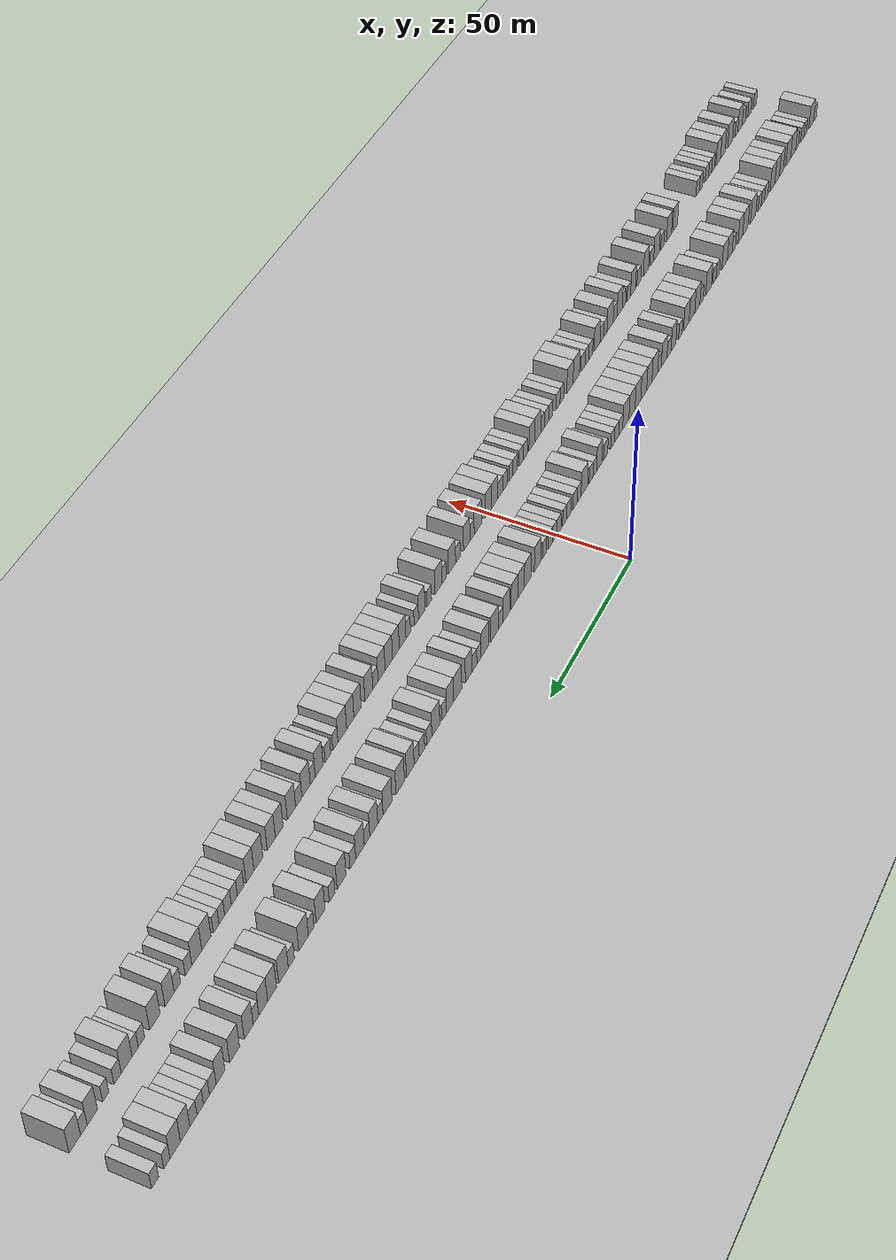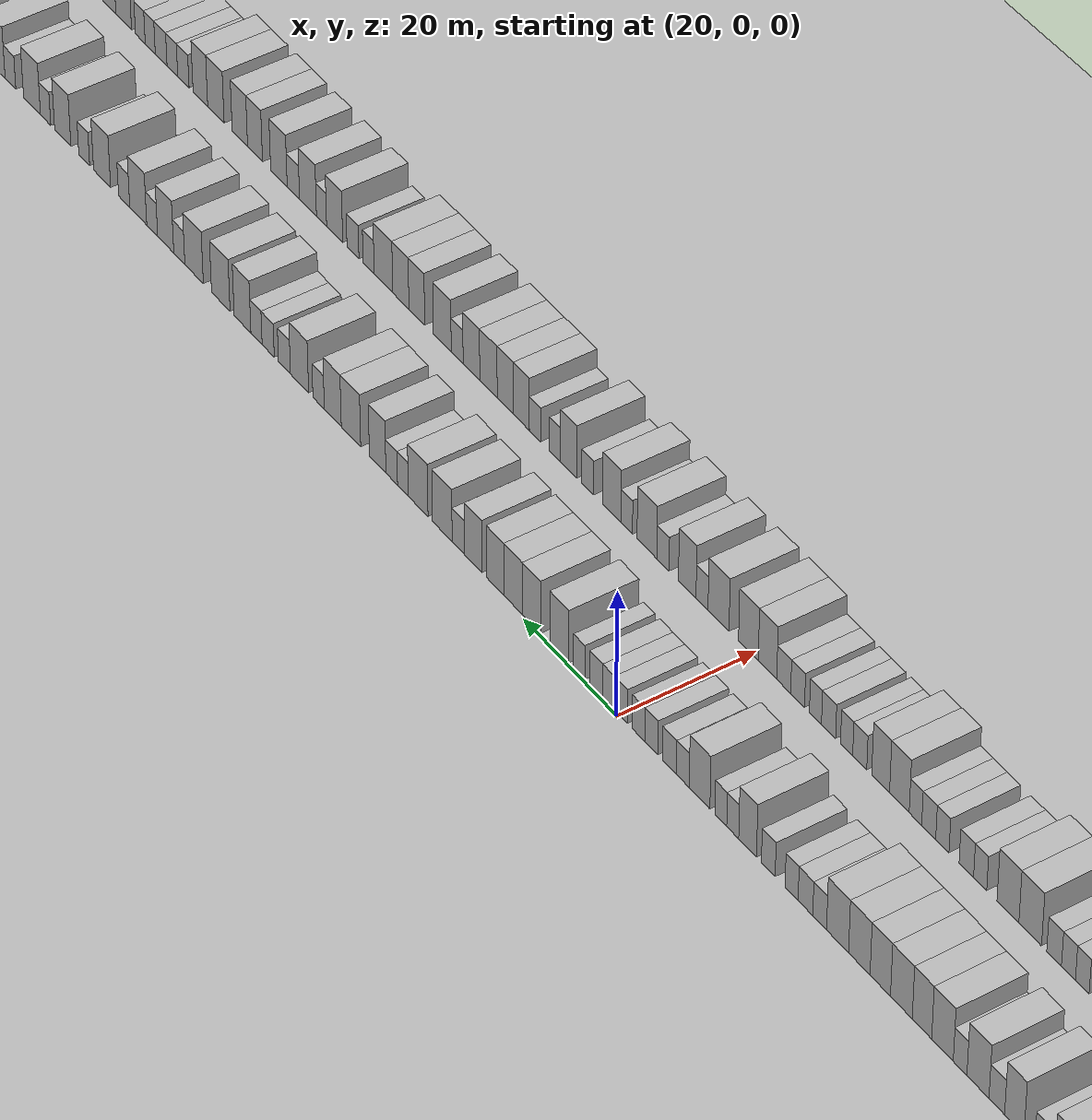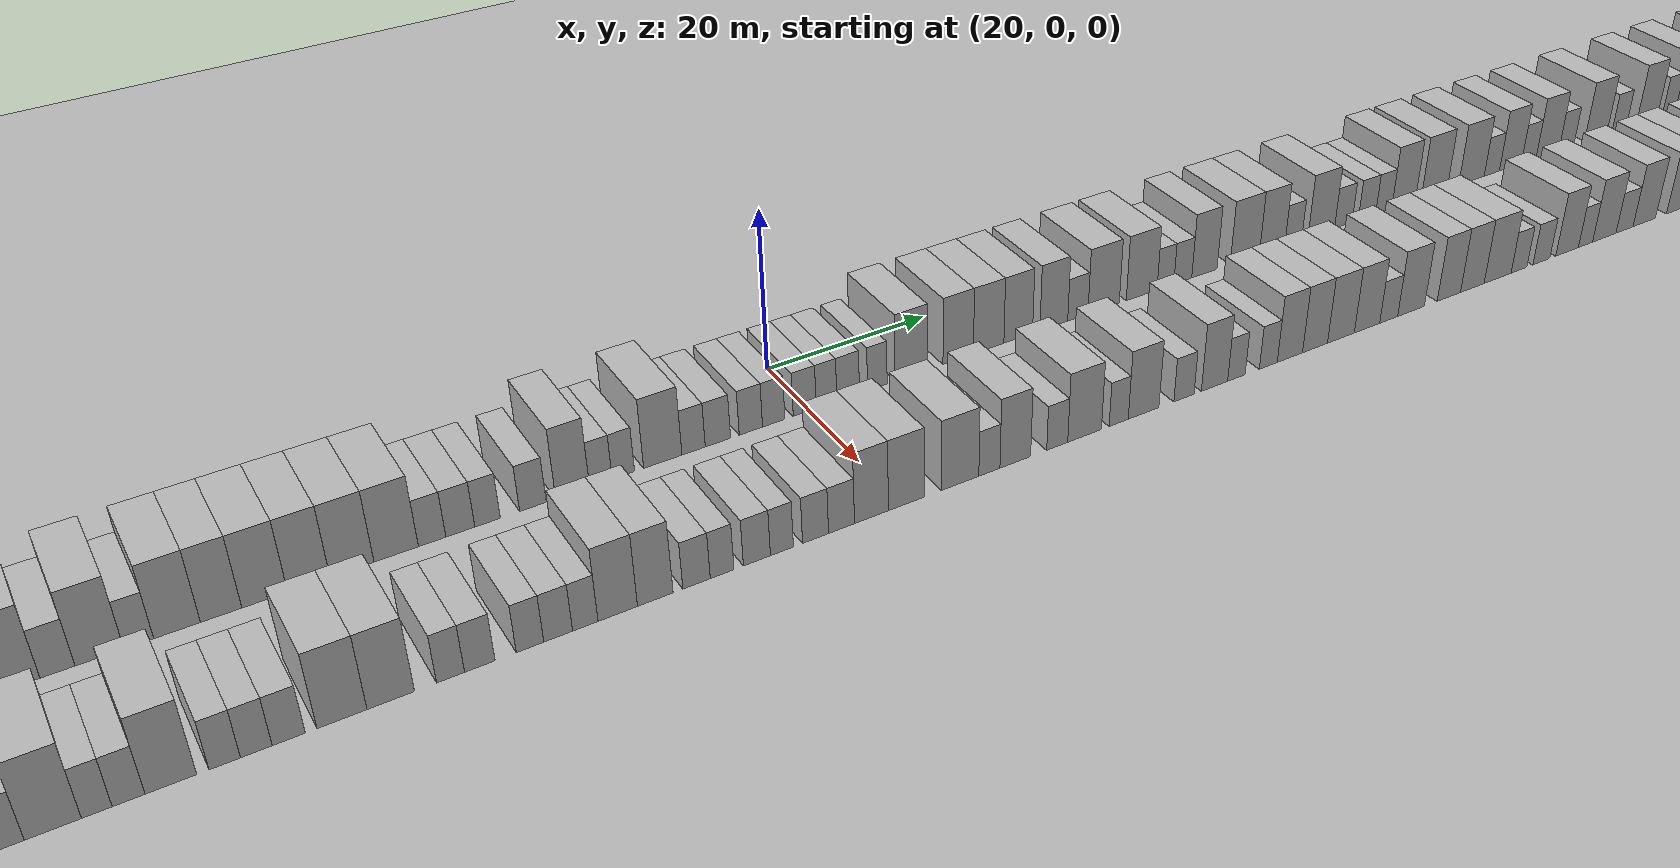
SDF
<?xml version="1.0" encoding="utf-8"?>

<sdf version="1.6">

   <world name="default">

      <gui fullscreen="0">

         <camera name="user_camera">

            <pose>-15 0 4.57585 0 0 0</pose>

            <view_controller>orbit</view_controller>

         </camera>

      </gui>

      <scene>

         <sky>

           <clouds>

             <speed>12</speed>

           </clouds>

         </sky>

         <ambient>0.4 0.4 0.4 1</ambient>

         <background>0.7 0.7 0.7 1</background>

         <shadows>1</shadows>

      </scene>

      <gravity>0 0 -9.8066</gravity>

      <magnetic_field>6e-06 2.3e-05 -4.2e-05</magnetic_field>

      <physics default="0" name="default_physics" type="ode">

         <ode>

            <solver>

               <type>quick</type>

               <iters>10</iters>

               <sor>1.0</sor>

               <use_dynamic_moi_rescaling>0</use_dynamic_moi_rescaling>

            </solver>

            <constraints>

               <cfm>0</cfm>

               <erp>0.2</erp>

               <contact_max_correcting_vel>100</contact_max_correcting_vel>

               <contact_surface_layer>0.001</contact_surface_layer>

            </constraints>

         </ode>

         <max_step_size>0.004</max_step_size>

         <real_time_factor>1</real_time_factor>

         <real_time_update_rate>250</real_time_update_rate>

      </physics>

      <light name="sun" type="directional">

         <cast_shadows>1</cast_shadows>

         <pose>0 0 10 0 0 0</pose>

         <diffuse>0.8 0.8 0.8 1</diffuse>

         <specular>0.2 0.2 0.2 1</specular>

         <attenuation>

            <range>1000</range>

            <constant>0.9</constant>

            <linear>0.01</linear>

            <quadratic>0.001</quadratic>

         </attenuation>

         <direction>-0.5 0.1 -0.9</direction>

      </light>

      <include>

         <name>ground_plane_1</name>

         <uri>model://HANNAS_ground_plane</uri>

         <pose>0 0 0  0 0 0</pose>

      </include>

      <include>

         <name>ground_plane_2</name>

         <uri>model://HANNAS_ground_plane</uri>

         <pose>100 0 0  0 0 0</pose>

      </include>

      <model name="building_1">

         <static>1</static>

         <pose frame="">25.0000 -196.7132 0 0.000000 0.000000 0.000000</pose>

         <link name="link">

            <pose frame="">0 0 3.00 0 0 0</pose>

            <collision name="collision">

               <geometry>

                  <box>

                     <size>10.0000 2.5736 6.0000</size>

                  </box>

               </geometry>

               <max_contacts>10</max_contacts>

               <surface>

                  <contact>

                     <ode/>

                  </contact>

                  <bounce/>

                  <friction>

                     <torsional>

                        <ode/>

                     </torsional>

                     <ode/>

                  </friction>

               </surface>

            </collision>

            <visual name="visual">

               <cast_shadows>0</cast_shadows>

               <geometry>

                  <box>

                     <size>10.0000 2.5736 6.0000</size>

                  </box>

               </geometry>

               <material>

                  <script>

                     <uri>model://HANNAS_wall/materials/scripts</uri>

                     <uri>model://HANNAS_wall/materials/textures</uri>

                     <name>vrc/HANNAS_wall</name>

                  </script>

               </material>

            </visual>

            <self_collide>0</self_collide>

            <enable_wind>0</enable_wind>

            <kinematic>0</kinematic>

         </link>

      </model>

      <model name="building_2">

         <static>1</static>

         <pose frame="">25.0000 -193.2047 0 0.000000 0.000000 0.000000</pose>

         <link name="link">

            <pose frame="">0 0 4.50 0 0 0</pose>

            <collision name="collision">

               <geometry>

                  <box>

                     <size>10.0000 4.4435 9.0000</size>

                  </box>

               </geometry>

               <max_contacts>10</max_contacts>

               <surface>

                  <contact>

                     <ode/>

                  </contact>

                  <bounce/>

                  <friction>

                     <torsional>

                        <ode/>

                     </torsional>

                     <ode/>

                  </friction>

               </surface>

            </collision>

            <visual name="visual">

               <cast_shadows>0</cast_shadows>

               <geometry>

                  <box>

                     <size>10.0000 4.4435 9.0000</size>

                  </box>

               </geometry>

               <material>

                  <script>

                     <uri>model://HANNAS_wall/materials/scripts</uri>

                     <uri>model://HANNAS_wall/materials/textures</uri>

                     <name>vrc/HANNAS_wall</name>

                  </script>

               </material>

            </visual>

            <self_collide>0</self_collide>

            <enable_wind>0</enable_wind>

            <kinematic>0</kinematic>

         </link>

      </model>

      <model name="building_3">

         <static>1</static>

         <pose frame="">25.0000 -187.7370 0 0.000000 0.000000 0.000000</pose>

         <link name="link">

            <pose frame="">0 0 3.00 0 0 0</pose>

            <collision name="collision">

               <geometry>

                  <box>

                     <size>10.0000 2.4917 6.0000</size>

                  </box>

               </geometry>

               <max_contacts>10</max_contacts>

               <surface>

                  <contact>

                     <ode/>

                  </contact>

                  <bounce/>

                  <friction>

                     <torsional>

                        <ode/>

                     </torsional>

                     <ode/>

                  </friction>

               </surface>

            </collision>

            <visual name="visual">

               <cast_shadows>0</cast_shadows>

               <geometry>

                  <box>

                     <size>10.0000 2.4917 6.0000</size>

                  </box>

               </geometry>

               <material>

                  <script>

                     <uri>model://HANNAS_wall/materials/scripts</uri>

                     <uri>model://HANNAS_wall/materials/textures</uri>

                     <name>vrc/HANNAS_wall</name>

                  </script>

               </material>

            </visual>

            <self_collide>0</self_collide>

            <enable_wind>0</enable_wind>

            <kinematic>0</kinematic>

         </link>

      </model>

      <model name="building_4">

         <static>1</static>

         <pose frame="">25.0000 -185.0531 0 0.000000 0.000000 0.000000</pose>

         <link name="link">

            <pose frame="">0 0 3.00 0 0 0</pose>

            <collision name="collision">

               <geometry>

                  <box>

                     <size>10.0000 2.8762 6.0000</size>

                  </box>

               </geometry>

               <max_contacts>10</max_contacts>

               <surface>

                  <contact>

                     <ode/>

                  </contact>

                  <bounce/>

                  <friction>

                     <torsional>

                        <ode/>

                     </torsional>

                     <ode/>

                  </friction>

               </surface>

            </collision>

            <visual name="visual">

               <cast_shadows>0</cast_shadows>

               <geometry>

                  <box>

                     <size>10.0000 2.8762 6.0000</size>

                  </box>

               </geometry>

               <material>

                  <script>

                     <uri>model://HANNAS_wall/materials/scripts</uri>

                     <uri>model://HANNAS_wall/materials/textures</uri>

                     <name>vrc/HANNAS_wall</name>

                  </script>

               </material>

            </visual>

            <self_collide>0</self_collide>

            <enable_wind>0</enable_wind>

            <kinematic>0</kinematic>

         </link>

      </model>

      <model name="building_5">

         <static>1</static>

         <pose frame="">25.0000 -180.3151 0 0.000000 0.000000 0.000000</pose>

         <link name="link">

            <pose frame="">0 0 3.00 0 0 0</pose>

            <collision name="collision">

               <geometry>

                  <box>

                     <size>10.0000 2.5999 6.0000</size>

                  </box>

               </geometry>

               <max_contacts>10</max_contacts>

               <surface>

                  <contact>

                     <ode/>

                  </contact>

                  <bounce/>

                  <friction>

                     <torsional>

                        <ode/>

                     </torsional>

                     <ode/>

                  </friction>

               </surface>

            </collision>

            <visual name="visual">

               <cast_shadows>0</cast_shadows>

               <geometry>

                  <box>

                     <size>10.0000 2.5999 6.0000</size>

                  </box>

               </geometry>

               <material>

                  <script>

                     <uri>model://HANNAS_wall/materials/scripts</uri>

                     <uri>model://HANNAS_wall/materials/textures</uri>

                     <name>vrc/HANNAS_wall</name>

                  </script>

               </material>

            </visual>

            <self_collide>0</self_collide>

            <enable_wind>0</enable_wind>

            <kinematic>0</kinematic>

         </link>

      </model>

      <model name="building_6">

         <static>1</static>

         <pose frame="">25.0000 -176.8122 0 0.000000 0.000000 0.000000</pose>

         <link name="link">

            <pose frame="">0 0 4.50 0 0 0</pose>

            <collision name="collision">

               <geometry>

                  <box>

                     <size>10.0000 4.4058 9.0000</size>

                  </box>

               </geometry>

               <max_contacts>10</max_contacts>

               <surface>

                  <contact>

                     <ode/>

                  </contact>

                  <bounce/>

                  <friction>

                     <torsional>

                        <ode/>

                     </torsional>

                     <ode/>

                  </friction>

               </surface>

            </collision>

            <visual name="visual">

               <cast_shadows>0</cast_shadows>

               <geometry>

                  <box>

                     <size>10.0000 4.4058 9.0000</size>

                  </box>

               </geometry>

               <material>

                  <script>

                     <uri>model://HANNAS_wall/materials/scripts</uri>

                     <uri>model://HANNAS_wall/materials/textures</uri>

                     <name>vrc/HANNAS_wall</name>

                  </script>

               </material>

            </visual>

            <self_collide>0</self_collide>

            <enable_wind>0</enable_wind>

            <kinematic>0</kinematic>

         </link>

      </model>

      <model name="building_7">

         <static>1</static>

         <pose frame="">25.0000 -172.4604 0 0.000000 0.000000 0.000000</pose>

         <link name="link">

            <pose frame="">0 0 4.50 0 0 0</pose>

            <collision name="collision">

               <geometry>

                  <box>

                     <size>10.0000 4.2978 9.0000</size>

                  </box>

               </geometry>

               <max_contacts>10</max_contacts>

               <surface>

                  <contact>

                     <ode/>

                  </contact>

                  <bounce/>

                  <friction>

                     <torsional>

                        <ode/>

                     </torsional>

                     <ode/>

                  </friction>

               </surface>

            </collision>

            <visual name="visual">

               <cast_shadows>0</cast_shadows>

               <geometry>

                  <box>

                     <size>10.0000 4.2978 9.0000</size>

                  </box>

               </geometry>

               <material>

                  <script>

                     <uri>model://HANNAS_wall/materials/scripts</uri>

                     <uri>model://HANNAS_wall/materials/textures</uri>

                     <name>vrc/HANNAS_wall</name>

                  </script>

               </material>

            </visual>

            <self_collide>0</self_collide>

            <enable_wind>0</enable_wind>

            <kinematic>0</kinematic>

         </link>

      </model>

      <model name="building_8">

         <static>1</static>

         <pose frame="">25.0000 -166.5079 0 0.000000 0.000000 0.000000</pose>

         <link name="link">

            <pose frame="">0 0 4.50 0 0 0</pose>

            <collision name="collision">

               <geometry>

                  <box>

                     <size>10.0000 3.6071 9.0000</size>

                  </box>

               </geometry>

               <max_contacts>10</max_contacts>

               <surface>

                  <contact>

                     <ode/>

                  </contact>

                  <bounce/>

                  <friction>

                     <torsional>

                        <ode/>

                     </torsional>

                     <ode/>

                  </friction>

               </surface>

            </collision>

            <visual name="visual">

               <cast_shadows>0</cast_shadows>

               <geometry>

                  <box>

                     <size>10.0000 3.6071 9.0000</size>

                  </box>

               </geometry>

               <material>

                  <script>

                     <uri>model://HANNAS_wall/materials/scripts</uri>

                     <uri>model://HANNAS_wall/materials/textures</uri>

                     <name>vrc/HANNAS_wall</name>

                  </script>

               </material>

            </visual>

            <self_collide>0</self_collide>

            <enable_wind>0</enable_wind>

            <kinematic>0</kinematic>

         </link>

      </model>

      <model name="building_9">

         <static>1</static>

         <pose frame="">25.0000 -162.7397 0 0.000000 0.000000 0.000000</pose>

         <link name="link">

            <pose frame="">0 0 4.50 0 0 0</pose>

            <collision name="collision">

               <geometry>

                  <box>

                     <size>10.0000 3.9293 9.0000</size>

                  </box>

               </geometry>

               <max_contacts>10</max_contacts>

               <surface>

                  <contact>

                     <ode/>

                  </contact>

                  <bounce/>

                  <friction>

                     <torsional>

                        <ode/>

                     </torsional>

                     <ode/>

                  </friction>

               </surface>

            </collision>

            <visual name="visual">

               <cast_shadows>0</cast_shadows>

               <geometry>

                  <box>

                     <size>10.0000 3.9293 9.0000</size>

                  </box>

               </geometry>

               <material>

                  <script>

                     <uri>model://HANNAS_wall/materials/scripts</uri>

                     <uri>model://HANNAS_wall/materials/textures</uri>

                     <name>vrc/HANNAS_wall</name>

                  </script>

               </material>

            </visual>

            <self_collide>0</self_collide>

            <enable_wind>0</enable_wind>

            <kinematic>0</kinematic>

         </link>

      </model>

      <model name="building_10">

         <static>1</static>

         <pose frame="">25.0000 -158.7315 0 0.000000 0.000000 0.000000</pose>

         <link name="link">

            <pose frame="">0 0 4.50 0 0 0</pose>

            <collision name="collision">

               <geometry>

                  <box>

                     <size>10.0000 4.0873 9.0000</size>

                  </box>

               </geometry>

               <max_contacts>10</max_contacts>

               <surface>

                  <contact>

                     <ode/>

                  </contact>

                  <bounce/>

                  <friction>

                     <torsional>

                        <ode/>

                     </torsional>

                     <ode/>

                  </friction>

               </surface>

            </collision>

            <visual name="visual">

               <cast_shadows>0</cast_shadows>

               <geometry>

                  <box>

                     <size>10.0000 4.0873 9.0000</size>

                  </box>

               </geometry>

               <material>

                  <script>

                     <uri>model://HANNAS_wall/materials/scripts</uri>

                     <uri>model://HANNAS_wall/materials/textures</uri>

                     <name>vrc/HANNAS_wall</name>

                  </script>

               </material>

            </visual>

            <self_collide>0</self_collide>

            <enable_wind>0</enable_wind>

            <kinematic>0</kinematic>

         </link>

      </model>

      <model name="building_11">

         <static>1</static>

         <pose frame="">25.0000 -153.2360 0 0.000000 0.000000 0.000000</pose>

         <link name="link">

            <pose frame="">0 0 3.00 0 0 0</pose>

            <collision name="collision">

               <geometry>

                  <box>

                     <size>10.0000 2.9037 6.0000</size>

                  </box>

               </geometry>

               <max_contacts>10</max_contacts>

               <surface>

                  <contact>

                     <ode/>

                  </contact>

                  <bounce/>

                  <friction>

                     <torsional>

                        <ode/>

                     </torsional>

                     <ode/>

                  </friction>

               </surface>

            </collision>

            <visual name="visual">

               <cast_shadows>0</cast_shadows>

               <geometry>

                  <box>

                     <size>10.0000 2.9037 6.0000</size>

                  </box>

               </geometry>

               <material>

                  <script>

                     <uri>model://HANNAS_wall/materials/scripts</uri>

                     <uri>model://HANNAS_wall/materials/textures</uri>

                     <name>vrc/HANNAS_wall</name>

                  </script>

               </material>

            </visual>

            <self_collide>0</self_collide>

            <enable_wind>0</enable_wind>

            <kinematic>0</kinematic>

         </link>

      </model>

      <model name="building_12">

         <static>1</static>

         <pose frame="">25.0000 -150.3929 0 0.000000 0.000000 0.000000</pose>

         <link name="link">

            <pose frame="">0 0 3.00 0 0 0</pose>

            <collision name="collision">

               <geometry>

                  <box>

                     <size>10.0000 2.7824 6.0000</size>

                  </box>

               </geometry>

               <max_contacts>10</max_contacts>

               <surface>

                  <contact>

                     <ode/>

                  </contact>

                  <bounce/>

                  <friction>

                     <torsional>

                        <ode/>

                     </torsional>

                     <ode/>

                  </friction>

               </surface>

            </collision>

            <visual name="visual">

               <cast_shadows>0</cast_shadows>

               <geometry>

                  <box>

                     <size>10.0000 2.7824 6.0000</size>

                  </box>

               </geometry>

               <material>

                  <script>

                     <uri>model://HANNAS_wall/materials/scripts</uri>

                     <uri>model://HANNAS_wall/materials/textures</uri>

                     <name>vrc/HANNAS_wall</name>

                  </script>

               </material>

            </visual>

            <self_collide>0</self_collide>

            <enable_wind>0</enable_wind>

            <kinematic>0</kinematic>

         </link>

      </model>

      <model name="building_13">

         <static>1</static>

         <pose frame="">25.0000 -147.6859 0 0.000000 0.000000 0.000000</pose>

         <link name="link">

            <pose frame="">0 0 3.00 0 0 0</pose>

            <collision name="collision">

               <geometry>

                  <box>

                     <size>10.0000 2.6316 6.0000</size>

                  </box>

               </geometry>

               <max_contacts>10</max_contacts>

               <surface>

                  <contact>

                     <ode/>

                  </contact>

                  <bounce/>

                  <friction>

                     <torsional>

                        <ode/>

                     </torsional>

                     <ode/>

                  </friction>

               </surface>

            </collision>

            <visual name="visual">

               <cast_shadows>0</cast_shadows>

               <geometry>

                  <box>

                     <size>10.0000 2.6316 6.0000</size>

                  </box>

               </geometry>

               <material>

                  <script>

                     <uri>model://HANNAS_wall/materials/scripts</uri>

                     <uri>model://HANNAS_wall/materials/textures</uri>

                     <name>vrc/HANNAS_wall</name>

                  </script>

               </material>

            </visual>

            <self_collide>0</self_collide>

            <enable_wind>0</enable_wind>

            <kinematic>0</kinematic>

         </link>

      </model>

      <model name="building_14">

         <static>1</static>

         <pose frame="">25.0000 -142.1304 0 0.000000 0.000000 0.000000</pose>

         <link name="link">

            <pose frame="">0 0 4.50 0 0 0</pose>

            <collision name="collision">

               <geometry>

                  <box>

                     <size>10.0000 4.4795 9.0000</size>

                  </box>

               </geometry>

               <max_contacts>10</max_contacts>

               <surface>

                  <contact>

                     <ode/>

                  </contact>

                  <bounce/>

                  <friction>

                     <torsional>

                        <ode/>

                     </torsional>

                     <ode/>

                  </friction>

               </surface>

            </collision>

            <visual name="visual">

               <cast_shadows>0</cast_shadows>

               <geometry>

                  <box>

                     <size>10.0000 4.4795 9.0000</size>

                  </box>

               </geometry>

               <material>

                  <script>

                     <uri>model://HANNAS_wall/materials/scripts</uri>

                     <uri>model://HANNAS_wall/materials/textures</uri>

                     <name>vrc/HANNAS_wall</name>

                  </script>

               </material>

            </visual>

            <self_collide>0</self_collide>

            <enable_wind>0</enable_wind>

            <kinematic>0</kinematic>

         </link>

      </model>

      <model name="building_15">

         <static>1</static>

         <pose frame="">25.0000 -135.7081 0 0.000000 0.000000 0.000000</pose>

         <link name="link">

            <pose frame="">0 0 4.50 0 0 0</pose>

            <collision name="collision">

               <geometry>

                  <box>

                     <size>10.0000 4.3652 9.0000</size>

                  </box>

               </geometry>

               <max_contacts>10</max_contacts>

               <surface>

                  <contact>

                     <ode/>

                  </contact>

                  <bounce/>

                  <friction>

                     <torsional>

                        <ode/>

                     </torsional>

                     <ode/>

                  </friction>

               </surface>

            </collision>

            <visual name="visual">

               <cast_shadows>0</cast_shadows>

               <geometry>

                  <box>

                     <size>10.0000 4.3652 9.0000</size>

                  </box>

               </geometry>

               <material>

                  <script>

                     <uri>model://HANNAS_wall/materials/scripts</uri>

                     <uri>model://HANNAS_wall/materials/textures</uri>

                     <name>vrc/HANNAS_wall</name>

                  </script>

               </material>

            </visual>

            <self_collide>0</self_collide>

            <enable_wind>0</enable_wind>

            <kinematic>0</kinematic>

         </link>

      </model>

      <model name="building_16">

         <static>1</static>

         <pose frame="">25.0000 -131.6402 0 0.000000 0.000000 0.000000</pose>

         <link name="link">

            <pose frame="">0 0 4.50 0 0 0</pose>

            <collision name="collision">

               <geometry>

                  <box>

                     <size>10.0000 3.7705 9.0000</size>

                  </box>

               </geometry>

               <max_contacts>10</max_contacts>

               <surface>

                  <contact>

                     <ode/>

                  </contact>

                  <bounce/>

                  <friction>

                     <torsional>

                        <ode/>

                     </torsional>

                     <ode/>

                  </friction>

               </surface>

            </collision>

            <visual name="visual">

               <cast_shadows>0</cast_shadows>

               <geometry>

                  <box>

                     <size>10.0000 3.7705 9.0000</size>

                  </box>

               </geometry>

               <material>

                  <script>

                     <uri>model://HANNAS_wall/materials/scripts</uri>

                     <uri>model://HANNAS_wall/materials/textures</uri>

                     <name>vrc/HANNAS_wall</name>

                  </script>

               </material>

            </visual>

            <self_collide>0</self_collide>

            <enable_wind>0</enable_wind>

            <kinematic>0</kinematic>

         </link>

      </model>

      <model name="building_17">

         <static>1</static>

         <pose frame="">25.0000 -126.3235 0 0.000000 0.000000 0.000000</pose>

         <link name="link">

            <pose frame="">0 0 3.00 0 0 0</pose>

            <collision name="collision">

               <geometry>

                  <box>

                     <size>10.0000 2.8627 6.0000</size>

                  </box>

               </geometry>

               <max_contacts>10</max_contacts>

               <surface>

                  <contact>

                     <ode/>

                  </contact>

                  <bounce/>

                  <friction>

                     <torsional>

                        <ode/>

                     </torsional>

                     <ode/>

                  </friction>

               </surface>

            </collision>

            <visual name="visual">

               <cast_shadows>0</cast_shadows>

               <geometry>

                  <box>

                     <size>10.0000 2.8627 6.0000</size>

                  </box>

               </geometry>

               <material>

                  <script>

                     <uri>model://HANNAS_wall/materials/scripts</uri>

                     <uri>model://HANNAS_wall/materials/textures</uri>

                     <name>vrc/HANNAS_wall</name>

                  </script>

               </material>

            </visual>

            <self_collide>0</self_collide>

            <enable_wind>0</enable_wind>

            <kinematic>0</kinematic>

         </link>

      </model>

      <model name="building_18">

         <static>1</static>

         <pose frame="">25.0000 -123.0128 0 0.000000 0.000000 0.000000</pose>

         <link name="link">

            <pose frame="">0 0 4.50 0 0 0</pose>

            <collision name="collision">

               <geometry>

                  <box>

                     <size>10.0000 3.7586 9.0000</size>

                  </box>

               </geometry>

               <max_contacts>10</max_contacts>

               <surface>

                  <contact>

                     <ode/>

                  </contact>

                  <bounce/>

                  <friction>

                     <torsional>

                        <ode/>

                     </torsional>

                     <ode/>

                  </friction>

               </surface>

            </collision>

            <visual name="visual">

               <cast_shadows>0</cast_shadows>

               <geometry>

                  <box>

                     <size>10.0000 3.7586 9.0000</size>

                  </box>

               </geometry>

               <material>

                  <script>

                     <uri>model://HANNAS_wall/materials/scripts</uri>

                     <uri>model://HANNAS_wall/materials/textures</uri>

                     <name>vrc/HANNAS_wall</name>

                  </script>

               </material>

            </visual>

            <self_collide>0</self_collide>

            <enable_wind>0</enable_wind>

            <kinematic>0</kinematic>

         </link>

      </model>

      <model name="building_19">

         <static>1</static>

         <pose frame="">25.0000 -118.8855 0 0.000000 0.000000 0.000000</pose>

         <link name="link">

            <pose frame="">0 0 4.50 0 0 0</pose>

            <collision name="collision">

               <geometry>

                  <box>

                     <size>10.0000 4.4960 9.0000</size>

                  </box>

               </geometry>

               <max_contacts>10</max_contacts>

               <surface>

                  <contact>

                     <ode/>

                  </contact>

                  <bounce/>

                  <friction>

                     <torsional>

                        <ode/>

                     </torsional>

                     <ode/>

                  </friction>

               </surface>

            </collision>

            <visual name="visual">

               <cast_shadows>0</cast_shadows>

               <geometry>

                  <box>

                     <size>10.0000 4.4960 9.0000</size>

                  </box>

               </geometry>

               <material>

                  <script>

                     <uri>model://HANNAS_wall/materials/scripts</uri>

                     <uri>model://HANNAS_wall/materials/textures</uri>

                     <name>vrc/HANNAS_wall</name>

                  </script>

               </material>

            </visual>

            <self_collide>0</self_collide>

            <enable_wind>0</enable_wind>

            <kinematic>0</kinematic>

         </link>

      </model>

      <model name="building_20">

         <static>1</static>

         <pose frame="">25.0000 -113.3541 0 0.000000 0.000000 0.000000</pose>

         <link name="link">

            <pose frame="">0 0 3.00 0 0 0</pose>

            <collision name="collision">

               <geometry>

                  <box>

                     <size>10.0000 2.5667 6.0000</size>

                  </box>

               </geometry>

               <max_contacts>10</max_contacts>

               <surface>

                  <contact>

                     <ode/>

                  </contact>

                  <bounce/>

                  <friction>

                     <torsional>

                        <ode/>

                     </torsional>

                     <ode/>

                  </friction>

               </surface>

            </collision>

            <visual name="visual">

               <cast_shadows>0</cast_shadows>

               <geometry>

                  <box>

                     <size>10.0000 2.5667 6.0000</size>

                  </box>

               </geometry>

               <material>

                  <script>

                     <uri>model://HANNAS_wall/materials/scripts</uri>

                     <uri>model://HANNAS_wall/materials/textures</uri>

                     <name>vrc/HANNAS_wall</name>

                  </script>

               </material>

            </visual>

            <self_collide>0</self_collide>

            <enable_wind>0</enable_wind>

            <kinematic>0</kinematic>

         </link>

      </model>

      <model name="building_21">

         <static>1</static>

         <pose frame="">25.0000 -110.7072 0 0.000000 0.000000 0.000000</pose>

         <link name="link">

            <pose frame="">0 0 3.00 0 0 0</pose>

            <collision name="collision">

               <geometry>

                  <box>

                     <size>10.0000 2.7272 6.0000</size>

                  </box>

               </geometry>

               <max_contacts>10</max_contacts>

               <surface>

                  <contact>

                     <ode/>

                  </contact>

                  <bounce/>

                  <friction>

                     <torsional>

                        <ode/>

                     </torsional>

                     <ode/>

                  </friction>

               </surface>

            </collision>

            <visual name="visual">

               <cast_shadows>0</cast_shadows>

               <geometry>

                  <box>

                     <size>10.0000 2.7272 6.0000</size>

                  </box>

               </geometry>

               <material>

                  <script>

                     <uri>model://HANNAS_wall/materials/scripts</uri>

                     <uri>model://HANNAS_wall/materials/textures</uri>

                     <name>vrc/HANNAS_wall</name>

                  </script>

               </material>

            </visual>

            <self_collide>0</self_collide>

            <enable_wind>0</enable_wind>

            <kinematic>0</kinematic>

         </link>

      </model>

      <model name="building_22">

         <static>1</static>

         <pose frame="">25.0000 -106.1514 0 0.000000 0.000000 0.000000</pose>

         <link name="link">

            <pose frame="">0 0 4.50 0 0 0</pose>

            <collision name="collision">

               <geometry>

                  <box>

                     <size>10.0000 4.3845 9.0000</size>

                  </box>

               </geometry>

               <max_contacts>10</max_contacts>

               <surface>

                  <contact>

                     <ode/>

                  </contact>

                  <bounce/>

                  <friction>

                     <torsional>

                        <ode/>

                     </torsional>

                     <ode/>

                  </friction>

               </surface>

            </collision>

            <visual name="visual">

               <cast_shadows>0</cast_shadows>

               <geometry>

                  <box>

                     <size>10.0000 4.3845 9.0000</size>

                  </box>

               </geometry>

               <material>

                  <script>

                     <uri>model://HANNAS_wall/materials/scripts</uri>

                     <uri>model://HANNAS_wall/materials/textures</uri>

                     <name>vrc/HANNAS_wall</name>

                  </script>

               </material>

            </visual>

            <self_collide>0</self_collide>

            <enable_wind>0</enable_wind>

            <kinematic>0</kinematic>

         </link>

      </model>

      <model name="building_23">

         <static>1</static>

         <pose frame="">25.0000 -100.6900 0 0.000000 0.000000 0.000000</pose>

         <link name="link">

            <pose frame="">0 0 3.00 0 0 0</pose>

            <collision name="collision">

               <geometry>

                  <box>

                     <size>10.0000 2.5384 6.0000</size>

                  </box>

               </geometry>

               <max_contacts>10</max_contacts>

               <surface>

                  <contact>

                     <ode/>

                  </contact>

                  <bounce/>

                  <friction>

                     <torsional>

                        <ode/>

                     </torsional>

                     <ode/>

                  </friction>

               </surface>

            </collision>

            <visual name="visual">

               <cast_shadows>0</cast_shadows>

               <geometry>

                  <box>

                     <size>10.0000 2.5384 6.0000</size>

                  </box>

               </geometry>

               <material>

                  <script>

                     <uri>model://HANNAS_wall/materials/scripts</uri>

                     <uri>model://HANNAS_wall/materials/textures</uri>

                     <name>vrc/HANNAS_wall</name>

                  </script>

               </material>

            </visual>

            <self_collide>0</self_collide>

            <enable_wind>0</enable_wind>

            <kinematic>0</kinematic>

         </link>

      </model>

      <model name="building_24">

         <static>1</static>

         <pose frame="">25.0000 -97.4387 0 0.000000 0.000000 0.000000</pose>

         <link name="link">

            <pose frame="">0 0 4.50 0 0 0</pose>

            <collision name="collision">

               <geometry>

                  <box>

                     <size>10.0000 3.9641 9.0000</size>

                  </box>

               </geometry>

               <max_contacts>10</max_contacts>

               <surface>

                  <contact>

                     <ode/>

                  </contact>

                  <bounce/>

                  <friction>

                     <torsional>

                        <ode/>

                     </torsional>

                     <ode/>

                  </friction>

               </surface>

            </collision>

            <visual name="visual">

               <cast_shadows>0</cast_shadows>

               <geometry>

                  <box>

                     <size>10.0000 3.9641 9.0000</size>

                  </box>

               </geometry>

               <material>

                  <script>

                     <uri>model://HANNAS_wall/materials/scripts</uri>

                     <uri>model://HANNAS_wall/materials/textures</uri>

                     <name>vrc/HANNAS_wall</name>

                  </script>

               </material>

            </visual>

            <self_collide>0</self_collide>

            <enable_wind>0</enable_wind>

            <kinematic>0</kinematic>

         </link>

      </model>

      <model name="building_25">

         <static>1</static>

         <pose frame="">25.0000 -93.3050 0 0.000000 0.000000 0.000000</pose>

         <link name="link">

            <pose frame="">0 0 4.50 0 0 0</pose>

            <collision name="collision">

               <geometry>

                  <box>

                     <size>10.0000 4.3034 9.0000</size>

                  </box>

               </geometry>

               <max_contacts>10</max_contacts>

               <surface>

                  <contact>

                     <ode/>

                  </contact>

                  <bounce/>

                  <friction>

                     <torsional>

                        <ode/>

                     </torsional>

                     <ode/>

                  </friction>

               </surface>

            </collision>

            <visual name="visual">

               <cast_shadows>0</cast_shadows>

               <geometry>

                  <box>

                     <size>10.0000 4.3034 9.0000</size>

                  </box>

               </geometry>

               <material>

                  <script>

                     <uri>model://HANNAS_wall/materials/scripts</uri>

                     <uri>model://HANNAS_wall/materials/textures</uri>

                     <name>vrc/HANNAS_wall</name>

                  </script>

               </material>

            </visual>

            <self_collide>0</self_collide>

            <enable_wind>0</enable_wind>

            <kinematic>0</kinematic>

         </link>

      </model>

      <model name="building_26">

         <static>1</static>

         <pose frame="">25.0000 -89.0119 0 0.000000 0.000000 0.000000</pose>

         <link name="link">

            <pose frame="">0 0 4.50 0 0 0</pose>

            <collision name="collision">

               <geometry>

                  <box>

                     <size>10.0000 4.2827 9.0000</size>

                  </box>

               </geometry>

               <max_contacts>10</max_contacts>

               <surface>

                  <contact>

                     <ode/>

                  </contact>

                  <bounce/>

                  <friction>

                     <torsional>

                        <ode/>

                     </torsional>

                     <ode/>

                  </friction>

               </surface>

            </collision>

            <visual name="visual">

               <cast_shadows>0</cast_shadows>

               <geometry>

                  <box>

                     <size>10.0000 4.2827 9.0000</size>

                  </box>

               </geometry>

               <material>

                  <script>

                     <uri>model://HANNAS_wall/materials/scripts</uri>

                     <uri>model://HANNAS_wall/materials/textures</uri>

                     <name>vrc/HANNAS_wall</name>

                  </script>

               </material>

            </visual>

            <self_collide>0</self_collide>

            <enable_wind>0</enable_wind>

            <kinematic>0</kinematic>

         </link>

      </model>

      <model name="building_27">

         <static>1</static>

         <pose frame="">25.0000 -84.5455 0 0.000000 0.000000 0.000000</pose>

         <link name="link">

            <pose frame="">0 0 3.00 0 0 0</pose>

            <collision name="collision">

               <geometry>

                  <box>

                     <size>10.0000 2.6500 6.0000</size>

                  </box>

               </geometry>

               <max_contacts>10</max_contacts>

               <surface>

                  <contact>

                     <ode/>

                  </contact>

                  <bounce/>

                  <friction>

                     <torsional>

                        <ode/>

                     </torsional>

                     <ode/>

                  </friction>

               </surface>

            </collision>

            <visual name="visual">

               <cast_shadows>0</cast_shadows>

               <geometry>

                  <box>

                     <size>10.0000 2.6500 6.0000</size>

                  </box>

               </geometry>

               <material>

                  <script>

                     <uri>model://HANNAS_wall/materials/scripts</uri>

                     <uri>model://HANNAS_wall/materials/textures</uri>

                     <name>vrc/HANNAS_wall</name>

                  </script>

               </material>

            </visual>

            <self_collide>0</self_collide>

            <enable_wind>0</enable_wind>

            <kinematic>0</kinematic>

         </link>

      </model>

      <model name="building_28">

         <static>1</static>

         <pose frame="">25.0000 -79.3932 0 0.000000 0.000000 0.000000</pose>

         <link name="link">

            <pose frame="">0 0 4.50 0 0 0</pose>

            <collision name="collision">

               <geometry>

                  <box>

                     <size>10.0000 3.6547 9.0000</size>

                  </box>

               </geometry>

               <max_contacts>10</max_contacts>

               <surface>

                  <contact>

                     <ode/>

                  </contact>

                  <bounce/>

                  <friction>

                     <torsional>

                        <ode/>

                     </torsional>

                     <ode/>

                  </friction>

               </surface>

            </collision>

            <visual name="visual">

               <cast_shadows>0</cast_shadows>

               <geometry>

                  <box>

                     <size>10.0000 3.6547 9.0000</size>

                  </box>

               </geometry>

               <material>

                  <script>

                     <uri>model://HANNAS_wall/materials/scripts</uri>

                     <uri>model://HANNAS_wall/materials/textures</uri>

                     <name>vrc/HANNAS_wall</name>

                  </script>

               </material>

            </visual>

            <self_collide>0</self_collide>

            <enable_wind>0</enable_wind>

            <kinematic>0</kinematic>

         </link>

      </model>

      <model name="building_29">

         <static>1</static>

         <pose frame="">25.0000 -76.0867 0 0.000000 0.000000 0.000000</pose>

         <link name="link">

            <pose frame="">0 0 3.00 0 0 0</pose>

            <collision name="collision">

               <geometry>

                  <box>

                     <size>10.0000 2.9583 6.0000</size>

                  </box>

               </geometry>

               <max_contacts>10</max_contacts>

               <surface>

                  <contact>

                     <ode/>

                  </contact>

                  <bounce/>

                  <friction>

                     <torsional>

                        <ode/>

                     </torsional>

                     <ode/>

                  </friction>

               </surface>

            </collision>

            <visual name="visual">

               <cast_shadows>0</cast_shadows>

               <geometry>

                  <box>

                     <size>10.0000 2.9583 6.0000</size>

                  </box>

               </geometry>

               <material>

                  <script>

                     <uri>model://HANNAS_wall/materials/scripts</uri>

                     <uri>model://HANNAS_wall/materials/textures</uri>

                     <name>vrc/HANNAS_wall</name>

                  </script>

               </material>

            </visual>

            <self_collide>0</self_collide>

            <enable_wind>0</enable_wind>

            <kinematic>0</kinematic>

         </link>

      </model>

      <model name="building_30">

         <static>1</static>

         <pose frame="">25.0000 -72.5102 0 0.000000 0.000000 0.000000</pose>

         <link name="link">

            <pose frame="">0 0 4.50 0 0 0</pose>

            <collision name="collision">

               <geometry>

                  <box>

                     <size>10.0000 4.1946 9.0000</size>

                  </box>

               </geometry>

               <max_contacts>10</max_contacts>

               <surface>

                  <contact>

                     <ode/>

                  </contact>

                  <bounce/>

                  <friction>

                     <torsional>

                        <ode/>

                     </torsional>

                     <ode/>

                  </friction>

               </surface>

            </collision>

            <visual name="visual">

               <cast_shadows>0</cast_shadows>

               <geometry>

                  <box>

                     <size>10.0000 4.1946 9.0000</size>

                  </box>

               </geometry>

               <material>

                  <script>

                     <uri>model://HANNAS_wall/materials/scripts</uri>

                     <uri>model://HANNAS_wall/materials/textures</uri>

                     <name>vrc/HANNAS_wall</name>

                  </script>

               </material>

            </visual>

            <self_collide>0</self_collide>

            <enable_wind>0</enable_wind>

            <kinematic>0</kinematic>

         </link>

      </model>

      <model name="building_31">

         <static>1</static>

         <pose frame="">25.0000 -69.1116 0 0.000000 0.000000 0.000000</pose>

         <link name="link">

            <pose frame="">0 0 3.00 0 0 0</pose>

            <collision name="collision">

               <geometry>

                  <box>

                     <size>10.0000 2.6026 6.0000</size>

                  </box>

               </geometry>

               <max_contacts>10</max_contacts>

               <surface>

                  <contact>

                     <ode/>

                  </contact>

                  <bounce/>

                  <friction>

                     <torsional>

                        <ode/>

                     </torsional>

                     <ode/>

                  </friction>

               </surface>

            </collision>

            <visual name="visual">

               <cast_shadows>0</cast_shadows>

               <geometry>

                  <box>

                     <size>10.0000 2.6026 6.0000</size>

                  </box>

               </geometry>

               <material>

                  <script>

                     <uri>model://HANNAS_wall/materials/scripts</uri>

                     <uri>model://HANNAS_wall/materials/textures</uri>

                     <name>vrc/HANNAS_wall</name>

                  </script>

               </material>

            </visual>

            <self_collide>0</self_collide>

            <enable_wind>0</enable_wind>

            <kinematic>0</kinematic>

         </link>

      </model>

      <model name="building_32">

         <static>1</static>

         <pose frame="">25.0000 -65.7340 0 0.000000 0.000000 0.000000</pose>

         <link name="link">

            <pose frame="">0 0 4.50 0 0 0</pose>

            <collision name="collision">

               <geometry>

                  <box>

                     <size>10.0000 4.1526 9.0000</size>

                  </box>

               </geometry>

               <max_contacts>10</max_contacts>

               <surface>

                  <contact>

                     <ode/>

                  </contact>

                  <bounce/>

                  <friction>

                     <torsional>

                        <ode/>

                     </torsional>

                     <ode/>

                  </friction>

               </surface>

            </collision>

            <visual name="visual">

               <cast_shadows>0</cast_shadows>

               <geometry>

                  <box>

                     <size>10.0000 4.1526 9.0000</size>

                  </box>

               </geometry>

               <material>

                  <script>

                     <uri>model://HANNAS_wall/materials/scripts</uri>

                     <uri>model://HANNAS_wall/materials/textures</uri>

                     <name>vrc/HANNAS_wall</name>

                  </script>

               </material>

            </visual>

            <self_collide>0</self_collide>

            <enable_wind>0</enable_wind>

            <kinematic>0</kinematic>

         </link>

      </model>

      <model name="building_33">

         <static>1</static>

         <pose frame="">25.0000 -61.7794 0 0.000000 0.000000 0.000000</pose>

         <link name="link">

            <pose frame="">0 0 4.50 0 0 0</pose>

            <collision name="collision">

               <geometry>

                  <box>

                     <size>10.0000 3.7566 9.0000</size>

                  </box>

               </geometry>

               <max_contacts>10</max_contacts>

               <surface>

                  <contact>

                     <ode/>

                  </contact>

                  <bounce/>

                  <friction>

                     <torsional>

                        <ode/>

                     </torsional>

                     <ode/>

                  </friction>

               </surface>

            </collision>

            <visual name="visual">

               <cast_shadows>0</cast_shadows>

               <geometry>

                  <box>

                     <size>10.0000 3.7566 9.0000</size>

                  </box>

               </geometry>

               <material>

                  <script>

                     <uri>model://HANNAS_wall/materials/scripts</uri>

                     <uri>model://HANNAS_wall/materials/textures</uri>

                     <name>vrc/HANNAS_wall</name>

                  </script>

               </material>

            </visual>

            <self_collide>0</self_collide>

            <enable_wind>0</enable_wind>

            <kinematic>0</kinematic>

         </link>

      </model>

      <model name="building_34">

         <static>1</static>

         <pose frame="">25.0000 -57.7851 0 0.000000 0.000000 0.000000</pose>

         <link name="link">

            <pose frame="">0 0 4.50 0 0 0</pose>

            <collision name="collision">

               <geometry>

                  <box>

                     <size>10.0000 4.2321 9.0000</size>

                  </box>

               </geometry>

               <max_contacts>10</max_contacts>

               <surface>

                  <contact>

                     <ode/>

                  </contact>

                  <bounce/>

                  <friction>

                     <torsional>

                        <ode/>

                     </torsional>

                     <ode/>

                  </friction>

               </surface>

            </collision>

            <visual name="visual">

               <cast_shadows>0</cast_shadows>

               <geometry>

                  <box>

                     <size>10.0000 4.2321 9.0000</size>

                  </box>

               </geometry>

               <material>

                  <script>

                     <uri>model://HANNAS_wall/materials/scripts</uri>

                     <uri>model://HANNAS_wall/materials/textures</uri>

                     <name>vrc/HANNAS_wall</name>

                  </script>

               </material>

            </visual>

            <self_collide>0</self_collide>

            <enable_wind>0</enable_wind>

            <kinematic>0</kinematic>

         </link>

      </model>

      <model name="building_35">

         <static>1</static>

         <pose frame="">25.0000 -53.6690 0 0.000000 0.000000 0.000000</pose>

         <link name="link">

            <pose frame="">0 0 4.50 0 0 0</pose>

            <collision name="collision">

               <geometry>

                  <box>

                     <size>10.0000 4.0003 9.0000</size>

                  </box>

               </geometry>

               <max_contacts>10</max_contacts>

               <surface>

                  <contact>

                     <ode/>

                  </contact>

                  <bounce/>

                  <friction>

                     <torsional>

                        <ode/>

                     </torsional>

                     <ode/>

                  </friction>

               </surface>

            </collision>

            <visual name="visual">

               <cast_shadows>0</cast_shadows>

               <geometry>

                  <box>

                     <size>10.0000 4.0003 9.0000</size>

                  </box>

               </geometry>

               <material>

                  <script>

                     <uri>model://HANNAS_wall/materials/scripts</uri>

                     <uri>model://HANNAS_wall/materials/textures</uri>

                     <name>vrc/HANNAS_wall</name>

                  </script>

               </material>

            </visual>

            <self_collide>0</self_collide>

            <enable_wind>0</enable_wind>

            <kinematic>0</kinematic>

         </link>

      </model>

      <model name="building_36">

         <static>1</static>

         <pose frame="">25.0000 -49.5500 0 0.000000 0.000000 0.000000</pose>

         <link name="link">

            <pose frame="">0 0 4.50 0 0 0</pose>

            <collision name="collision">

               <geometry>

                  <box>

                     <size>10.0000 4.2375 9.0000</size>

                  </box>

               </geometry>

               <max_contacts>10</max_contacts>

               <surface>

                  <contact>

                     <ode/>

                  </contact>

                  <bounce/>

                  <friction>

                     <torsional>

                        <ode/>

                     </torsional>

                     <ode/>

                  </friction>

               </surface>

            </collision>

            <visual name="visual">

               <cast_shadows>0</cast_shadows>

               <geometry>

                  <box>

                     <size>10.0000 4.2375 9.0000</size>

                  </box>

               </geometry>

               <material>

                  <script>

                     <uri>model://HANNAS_wall/materials/scripts</uri>

                     <uri>model://HANNAS_wall/materials/textures</uri>

                     <name>vrc/HANNAS_wall</name>

                  </script>

               </material>

            </visual>

            <self_collide>0</self_collide>

            <enable_wind>0</enable_wind>

            <kinematic>0</kinematic>

         </link>

      </model>

      <model name="building_37">

         <static>1</static>

         <pose frame="">25.0000 -45.2486 0 0.000000 0.000000 0.000000</pose>

         <link name="link">

            <pose frame="">0 0 4.50 0 0 0</pose>

            <collision name="collision">

               <geometry>

                  <box>

                     <size>10.0000 4.3654 9.0000</size>

                  </box>

               </geometry>

               <max_contacts>10</max_contacts>

               <surface>

                  <contact>

                     <ode/>

                  </contact>

                  <bounce/>

                  <friction>

                     <torsional>

                        <ode/>

                     </torsional>

                     <ode/>

                  </friction>

               </surface>

            </collision>

            <visual name="visual">

               <cast_shadows>0</cast_shadows>

               <geometry>

                  <box>

                     <size>10.0000 4.3654 9.0000</size>

                  </box>

               </geometry>

               <material>

                  <script>

                     <uri>model://HANNAS_wall/materials/scripts</uri>

                     <uri>model://HANNAS_wall/materials/textures</uri>

                     <name>vrc/HANNAS_wall</name>

                  </script>

               </material>

            </visual>

            <self_collide>0</self_collide>

            <enable_wind>0</enable_wind>

            <kinematic>0</kinematic>

         </link>

      </model>

      <model name="building_38">

         <static>1</static>

         <pose frame="">25.0000 -41.6955 0 0.000000 0.000000 0.000000</pose>

         <link name="link">

            <pose frame="">0 0 3.00 0 0 0</pose>

            <collision name="collision">

               <geometry>

                  <box>

                     <size>10.0000 2.7409 6.0000</size>

                  </box>

               </geometry>

               <max_contacts>10</max_contacts>

               <surface>

                  <contact>

                     <ode/>

                  </contact>

                  <bounce/>

                  <friction>

                     <torsional>

                        <ode/>

                     </torsional>

                     <ode/>

                  </friction>

               </surface>

            </collision>

            <visual name="visual">

               <cast_shadows>0</cast_shadows>

               <geometry>

                  <box>

                     <size>10.0000 2.7409 6.0000</size>

                  </box>

               </geometry>

               <material>

                  <script>

                     <uri>model://HANNAS_wall/materials/scripts</uri>

                     <uri>model://HANNAS_wall/materials/textures</uri>

                     <name>vrc/HANNAS_wall</name>

                  </script>

               </material>

            </visual>

            <self_collide>0</self_collide>

            <enable_wind>0</enable_wind>

            <kinematic>0</kinematic>

         </link>

      </model>

      <model name="building_39">

         <static>1</static>

         <pose frame="">25.0000 -38.8572 0 0.000000 0.000000 0.000000</pose>

         <link name="link">

            <pose frame="">0 0 3.00 0 0 0</pose>

            <collision name="collision">

               <geometry>

                  <box>

                     <size>10.0000 2.9356 6.0000</size>

                  </box>

               </geometry>

               <max_contacts>10</max_contacts>

               <surface>

                  <contact>

                     <ode/>

                  </contact>

                  <bounce/>

                  <friction>

                     <torsional>

                        <ode/>

                     </torsional>

                     <ode/>

                  </friction>

               </surface>

            </collision>

            <visual name="visual">

               <cast_shadows>0</cast_shadows>

               <geometry>

                  <box>

                     <size>10.0000 2.9356 6.0000</size>

                  </box>

               </geometry>

               <material>

                  <script>

                     <uri>model://HANNAS_wall/materials/scripts</uri>

                     <uri>model://HANNAS_wall/materials/textures</uri>

                     <name>vrc/HANNAS_wall</name>

                  </script>

               </material>

            </visual>

            <self_collide>0</self_collide>

            <enable_wind>0</enable_wind>

            <kinematic>0</kinematic>

         </link>

      </model>

      <model name="building_40">

         <static>1</static>

         <pose frame="">25.0000 -36.0790 0 0.000000 0.000000 0.000000</pose>

         <link name="link">

            <pose frame="">0 0 3.00 0 0 0</pose>

            <collision name="collision">

               <geometry>

                  <box>

                     <size>10.0000 2.6208 6.0000</size>

                  </box>

               </geometry>

               <max_contacts>10</max_contacts>

               <surface>

                  <contact>

                     <ode/>

                  </contact>

                  <bounce/>

                  <friction>

                     <torsional>

                        <ode/>

                     </torsional>

                     <ode/>

                  </friction>

               </surface>

            </collision>

            <visual name="visual">

               <cast_shadows>0</cast_shadows>

               <geometry>

                  <box>

                     <size>10.0000 2.6208 6.0000</size>

                  </box>

               </geometry>

               <material>

                  <script>

                     <uri>model://HANNAS_wall/materials/scripts</uri>

                     <uri>model://HANNAS_wall/materials/textures</uri>

                     <name>vrc/HANNAS_wall</name>

                  </script>

               </material>

            </visual>

            <self_collide>0</self_collide>

            <enable_wind>0</enable_wind>

            <kinematic>0</kinematic>

         </link>

      </model>

      <model name="building_41">

         <static>1</static>

         <pose frame="">25.0000 -31.3737 0 0.000000 0.000000 0.000000</pose>

         <link name="link">

            <pose frame="">0 0 3.00 0 0 0</pose>

            <collision name="collision">

               <geometry>

                  <box>

                     <size>10.0000 2.7899 6.0000</size>

                  </box>

               </geometry>

               <max_contacts>10</max_contacts>

               <surface>

                  <contact>

                     <ode/>

                  </contact>

                  <bounce/>

                  <friction>

                     <torsional>

                        <ode/>

                     </torsional>

                     <ode/>

                  </friction>

               </surface>

            </collision>

            <visual name="visual">

               <cast_shadows>0</cast_shadows>

               <geometry>

                  <box>

                     <size>10.0000 2.7899 6.0000</size>

                  </box>

               </geometry>

               <material>

                  <script>

                     <uri>model://HANNAS_wall/materials/scripts</uri>

                     <uri>model://HANNAS_wall/materials/textures</uri>

                     <name>vrc/HANNAS_wall</name>

                  </script>

               </material>

            </visual>

            <self_collide>0</self_collide>

            <enable_wind>0</enable_wind>

            <kinematic>0</kinematic>

         </link>

      </model>

      <model name="building_42">

         <static>1</static>

         <pose frame="">25.0000 -27.1665 0 0.000000 0.000000 0.000000</pose>

         <link name="link">

            <pose frame="">0 0 4.50 0 0 0</pose>

            <collision name="collision">

               <geometry>

                  <box>

                     <size>10.0000 3.6244 9.0000</size>

                  </box>

               </geometry>

               <max_contacts>10</max_contacts>

               <surface>

                  <contact>

                     <ode/>

                  </contact>

                  <bounce/>

                  <friction>

                     <torsional>

                        <ode/>

                     </torsional>

                     <ode/>

                  </friction>

               </surface>

            </collision>

            <visual name="visual">

               <cast_shadows>0</cast_shadows>

               <geometry>

                  <box>

                     <size>10.0000 3.6244 9.0000</size>

                  </box>

               </geometry>

               <material>

                  <script>

                     <uri>model://HANNAS_wall/materials/scripts</uri>

                     <uri>model://HANNAS_wall/materials/textures</uri>

                     <name>vrc/HANNAS_wall</name>

                  </script>

               </material>

            </visual>

            <self_collide>0</self_collide>

            <enable_wind>0</enable_wind>

            <kinematic>0</kinematic>

         </link>

      </model>

      <model name="building_43">

         <static>1</static>

         <pose frame="">25.0000 -24.1285 0 0.000000 0.000000 0.000000</pose>

         <link name="link">

            <pose frame="">0 0 3.00 0 0 0</pose>

            <collision name="collision">

               <geometry>

                  <box>

                     <size>10.0000 2.4518 6.0000</size>

                  </box>

               </geometry>

               <max_contacts>10</max_contacts>

               <surface>

                  <contact>

                     <ode/>

                  </contact>

                  <bounce/>

                  <friction>

                     <torsional>

                        <ode/>

                     </torsional>

                     <ode/>

                  </friction>

               </surface>

            </collision>

            <visual name="visual">

               <cast_shadows>0</cast_shadows>

               <geometry>

                  <box>

                     <size>10.0000 2.4518 6.0000</size>

                  </box>

               </geometry>

               <material>

                  <script>

                     <uri>model://HANNAS_wall/materials/scripts</uri>

                     <uri>model://HANNAS_wall/materials/textures</uri>

                     <name>vrc/HANNAS_wall</name>

                  </script>

               </material>

            </visual>

            <self_collide>0</self_collide>

            <enable_wind>0</enable_wind>

            <kinematic>0</kinematic>

         </link>

      </model>

      <model name="building_44">

         <static>1</static>

         <pose frame="">25.0000 -21.6762 0 0.000000 0.000000 0.000000</pose>

         <link name="link">

            <pose frame="">0 0 3.00 0 0 0</pose>

            <collision name="collision">

               <geometry>

                  <box>

                     <size>10.0000 2.4528 6.0000</size>

                  </box>

               </geometry>

               <max_contacts>10</max_contacts>

               <surface>

                  <contact>

                     <ode/>

                  </contact>

                  <bounce/>

                  <friction>

                     <torsional>

                        <ode/>

                     </torsional>

                     <ode/>

                  </friction>

               </surface>

            </collision>

            <visual name="visual">

               <cast_shadows>0</cast_shadows>

               <geometry>

                  <box>

                     <size>10.0000 2.4528 6.0000</size>

                  </box>

               </geometry>

               <material>

                  <script>

                     <uri>model://HANNAS_wall/materials/scripts</uri>

                     <uri>model://HANNAS_wall/materials/textures</uri>

                     <name>vrc/HANNAS_wall</name>

                  </script>

               </material>

            </visual>

            <self_collide>0</self_collide>

            <enable_wind>0</enable_wind>

            <kinematic>0</kinematic>

         </link>

      </model>

      <model name="building_45">

         <static>1</static>

         <pose frame="">25.0000 -17.3049 0 0.000000 0.000000 0.000000</pose>

         <link name="link">

            <pose frame="">0 0 4.50 0 0 0</pose>

            <collision name="collision">

               <geometry>

                  <box>

                     <size>10.0000 4.2897 9.0000</size>

                  </box>

               </geometry>

               <max_contacts>10</max_contacts>

               <surface>

                  <contact>

                     <ode/>

                  </contact>

                  <bounce/>

                  <friction>

                     <torsional>

                        <ode/>

                     </torsional>

                     <ode/>

                  </friction>

               </surface>

            </collision>

            <visual name="visual">

               <cast_shadows>0</cast_shadows>

               <geometry>

                  <box>

                     <size>10.0000 4.2897 9.0000</size>

                  </box>

               </geometry>

               <material>

                  <script>

                     <uri>model://HANNAS_wall/materials/scripts</uri>

                     <uri>model://HANNAS_wall/materials/textures</uri>

                     <name>vrc/HANNAS_wall</name>

                  </script>

               </material>

            </visual>

            <self_collide>0</self_collide>

            <enable_wind>0</enable_wind>

            <kinematic>0</kinematic>

         </link>

      </model>

      <model name="building_46">

         <static>1</static>

         <pose frame="">25.0000 -13.8331 0 0.000000 0.000000 0.000000</pose>

         <link name="link">

            <pose frame="">0 0 3.00 0 0 0</pose>

            <collision name="collision">

               <geometry>

                  <box>

                     <size>10.0000 2.6541 6.0000</size>

                  </box>

               </geometry>

               <max_contacts>10</max_contacts>

               <surface>

                  <contact>

                     <ode/>

                  </contact>

                  <bounce/>

                  <friction>

                     <torsional>

                        <ode/>

                     </torsional>

                     <ode/>

                  </friction>

               </surface>

            </collision>

            <visual name="visual">

               <cast_shadows>0</cast_shadows>

               <geometry>

                  <box>

                     <size>10.0000 2.6541 6.0000</size>

                  </box>

               </geometry>

               <material>

                  <script>

                     <uri>model://HANNAS_wall/materials/scripts</uri>

                     <uri>model://HANNAS_wall/materials/textures</uri>

                     <name>vrc/HANNAS_wall</name>

                  </script>

               </material>

            </visual>

            <self_collide>0</self_collide>

            <enable_wind>0</enable_wind>

            <kinematic>0</kinematic>

         </link>

      </model>

      <model name="building_47">

         <static>1</static>

         <pose frame="">25.0000 -11.0533 0 0.000000 0.000000 0.000000</pose>

         <link name="link">

            <pose frame="">0 0 3.00 0 0 0</pose>

            <collision name="collision">

               <geometry>

                  <box>

                     <size>10.0000 2.9054 6.0000</size>

                  </box>

               </geometry>

               <max_contacts>10</max_contacts>

               <surface>

                  <contact>

                     <ode/>

                  </contact>

                  <bounce/>

                  <friction>

                     <torsional>

                        <ode/>

                     </torsional>

                     <ode/>

                  </friction>

               </surface>

            </collision>

            <visual name="visual">

               <cast_shadows>0</cast_shadows>

               <geometry>

                  <box>

                     <size>10.0000 2.9054 6.0000</size>

                  </box>

               </geometry>

               <material>

                  <script>

                     <uri>model://HANNAS_wall/materials/scripts</uri>

                     <uri>model://HANNAS_wall/materials/textures</uri>

                     <name>vrc/HANNAS_wall</name>

                  </script>

               </material>

            </visual>

            <self_collide>0</self_collide>

            <enable_wind>0</enable_wind>

            <kinematic>0</kinematic>

         </link>

      </model>

      <model name="building_48">

         <static>1</static>

         <pose frame="">25.0000 -7.2363 0 0.000000 0.000000 0.000000</pose>

         <link name="link">

            <pose frame="">0 0 3.00 0 0 0</pose>

            <collision name="collision">

               <geometry>

                  <box>

                     <size>10.0000 2.7287 6.0000</size>

                  </box>

               </geometry>

               <max_contacts>10</max_contacts>

               <surface>

                  <contact>

                     <ode/>

                  </contact>

                  <bounce/>

                  <friction>

                     <torsional>

                        <ode/>

                     </torsional>

                     <ode/>

                  </friction>

               </surface>

            </collision>

            <visual name="visual">

               <cast_shadows>0</cast_shadows>

               <geometry>

                  <box>

                     <size>10.0000 2.7287 6.0000</size>

                  </box>

               </geometry>

               <material>

                  <script>

                     <uri>model://HANNAS_wall/materials/scripts</uri>

                     <uri>model://HANNAS_wall/materials/textures</uri>

                     <name>vrc/HANNAS_wall</name>

                  </script>

               </material>

            </visual>

            <self_collide>0</self_collide>

            <enable_wind>0</enable_wind>

            <kinematic>0</kinematic>

         </link>

      </model>

      <model name="building_49">

         <static>1</static>

         <pose frame="">25.0000 -4.5512 0 0.000000 0.000000 0.000000</pose>

         <link name="link">

            <pose frame="">0 0 3.00 0 0 0</pose>

            <collision name="collision">

               <geometry>

                  <box>

                     <size>10.0000 2.6413 6.0000</size>

                  </box>

               </geometry>

               <max_contacts>10</max_contacts>

               <surface>

                  <contact>

                     <ode/>

                  </contact>

                  <bounce/>

                  <friction>

                     <torsional>

                        <ode/>

                     </torsional>

                     <ode/>

                  </friction>

               </surface>

            </collision>

            <visual name="visual">

               <cast_shadows>0</cast_shadows>

               <geometry>

                  <box>

                     <size>10.0000 2.6413 6.0000</size>

                  </box>

               </geometry>

               <material>

                  <script>

                     <uri>model://HANNAS_wall/materials/scripts</uri>

                     <uri>model://HANNAS_wall/materials/textures</uri>

                     <name>vrc/HANNAS_wall</name>

                  </script>

               </material>

            </visual>

            <self_collide>0</self_collide>

            <enable_wind>0</enable_wind>

            <kinematic>0</kinematic>

         </link>

      </model>

      <model name="building_50">

         <static>1</static>

         <pose frame="">25.0000 -0.8488 0 0.000000 0.000000 0.000000</pose>

         <link name="link">

            <pose frame="">0 0 3.00 0 0 0</pose>

            <collision name="collision">

               <geometry>

                  <box>

                     <size>10.0000 2.7635 6.0000</size>

                  </box>

               </geometry>

               <max_contacts>10</max_contacts>

               <surface>

                  <contact>

                     <ode/>

                  </contact>

                  <bounce/>

                  <friction>

                     <torsional>

                        <ode/>

                     </torsional>

                     <ode/>

                  </friction>

               </surface>

            </collision>

            <visual name="visual">

               <cast_shadows>0</cast_shadows>

               <geometry>

                  <box>

                     <size>10.0000 2.7635 6.0000</size>

                  </box>

               </geometry>

               <material>

                  <script>

                     <uri>model://HANNAS_wall/materials/scripts</uri>

                     <uri>model://HANNAS_wall/materials/textures</uri>

                     <name>vrc/HANNAS_wall</name>

                  </script>

               </material>

            </visual>

            <self_collide>0</self_collide>

            <enable_wind>0</enable_wind>

            <kinematic>0</kinematic>

         </link>

      </model>

      <model name="building_51">

         <static>1</static>

         <pose frame="">25.0000 1.7864 0 0.000000 0.000000 0.000000</pose>

         <link name="link">

            <pose frame="">0 0 3.00 0 0 0</pose>

            <collision name="collision">

               <geometry>

                  <box>

                     <size>10.0000 2.5070 6.0000</size>

                  </box>

               </geometry>

               <max_contacts>10</max_contacts>

               <surface>

                  <contact>

                     <ode/>

                  </contact>

                  <bounce/>

                  <friction>

                     <torsional>

                        <ode/>

                     </torsional>

                     <ode/>

                  </friction>

               </surface>

            </collision>

            <visual name="visual">

               <cast_shadows>0</cast_shadows>

               <geometry>

                  <box>

                     <size>10.0000 2.5070 6.0000</size>

                  </box>

               </geometry>

               <material>

                  <script>

                     <uri>model://HANNAS_wall/materials/scripts</uri>

                     <uri>model://HANNAS_wall/materials/textures</uri>

                     <name>vrc/HANNAS_wall</name>

                  </script>

               </material>

            </visual>

            <self_collide>0</self_collide>

            <enable_wind>0</enable_wind>

            <kinematic>0</kinematic>

         </link>

      </model>

      <model name="building_52">

         <static>1</static>

         <pose frame="">25.0000 4.4324 0 0.000000 0.000000 0.000000</pose>

         <link name="link">

            <pose frame="">0 0 3.00 0 0 0</pose>

            <collision name="collision">

               <geometry>

                  <box>

                     <size>10.0000 2.7849 6.0000</size>

                  </box>

               </geometry>

               <max_contacts>10</max_contacts>

               <surface>

                  <contact>

                     <ode/>

                  </contact>

                  <bounce/>

                  <friction>

                     <torsional>

                        <ode/>

                     </torsional>

                     <ode/>

                  </friction>

               </surface>

            </collision>

            <visual name="visual">

               <cast_shadows>0</cast_shadows>

               <geometry>

                  <box>

                     <size>10.0000 2.7849 6.0000</size>

                  </box>

               </geometry>

               <material>

                  <script>

                     <uri>model://HANNAS_wall/materials/scripts</uri>

                     <uri>model://HANNAS_wall/materials/textures</uri>

                     <name>vrc/HANNAS_wall</name>

                  </script>

               </material>

            </visual>

            <self_collide>0</self_collide>

            <enable_wind>0</enable_wind>

            <kinematic>0</kinematic>

         </link>

      </model>

      <model name="building_53">

         <static>1</static>

         <pose frame="">25.0000 8.0485 0 0.000000 0.000000 0.000000</pose>

         <link name="link">

            <pose frame="">0 0 3.00 0 0 0</pose>

            <collision name="collision">

               <geometry>

                  <box>

                     <size>10.0000 2.4474 6.0000</size>

                  </box>

               </geometry>

               <max_contacts>10</max_contacts>

               <surface>

                  <contact>

                     <ode/>

                  </contact>

                  <bounce/>

                  <friction>

                     <torsional>

                        <ode/>

                     </torsional>

                     <ode/>

                  </friction>

               </surface>

            </collision>

            <visual name="visual">

               <cast_shadows>0</cast_shadows>

               <geometry>

                  <box>

                     <size>10.0000 2.4474 6.0000</size>

                  </box>

               </geometry>

               <material>

                  <script>

                     <uri>model://HANNAS_wall/materials/scripts</uri>

                     <uri>model://HANNAS_wall/materials/textures</uri>

                     <name>vrc/HANNAS_wall</name>

                  </script>

               </material>

            </visual>

            <self_collide>0</self_collide>

            <enable_wind>0</enable_wind>

            <kinematic>0</kinematic>

         </link>

      </model>

      <model name="building_54">

         <static>1</static>

         <pose frame="">25.0000 12.3292 0 0.000000 0.000000 0.000000</pose>

         <link name="link">

            <pose frame="">0 0 4.50 0 0 0</pose>

            <collision name="collision">

               <geometry>

                  <box>

                     <size>10.0000 4.1140 9.0000</size>

                  </box>

               </geometry>

               <max_contacts>10</max_contacts>

               <surface>

                  <contact>

                     <ode/>

                  </contact>

                  <bounce/>

                  <friction>

                     <torsional>

                        <ode/>

                     </torsional>

                     <ode/>

                  </friction>

               </surface>

            </collision>

            <visual name="visual">

               <cast_shadows>0</cast_shadows>

               <geometry>

                  <box>

                     <size>10.0000 4.1140 9.0000</size>

                  </box>

               </geometry>

               <material>

                  <script>

                     <uri>model://HANNAS_wall/materials/scripts</uri>

                     <uri>model://HANNAS_wall/materials/textures</uri>

                     <name>vrc/HANNAS_wall</name>

                  </script>

               </material>

            </visual>

            <self_collide>0</self_collide>

            <enable_wind>0</enable_wind>

            <kinematic>0</kinematic>

         </link>

      </model>

      <model name="building_55">

         <static>1</static>

         <pose frame="">25.0000 18.3756 0 0.000000 0.000000 0.000000</pose>

         <link name="link">

            <pose frame="">0 0 4.50 0 0 0</pose>

            <collision name="collision">

               <geometry>

                  <box>

                     <size>10.0000 3.9787 9.0000</size>

                  </box>

               </geometry>

               <max_contacts>10</max_contacts>

               <surface>

                  <contact>

                     <ode/>

                  </contact>

                  <bounce/>

                  <friction>

                     <torsional>

                        <ode/>

                     </torsional>

                     <ode/>

                  </friction>

               </surface>

            </collision>

            <visual name="visual">

               <cast_shadows>0</cast_shadows>

               <geometry>

                  <box>

                     <size>10.0000 3.9787 9.0000</size>

                  </box>

               </geometry>

               <material>

                  <script>

                     <uri>model://HANNAS_wall/materials/scripts</uri>

                     <uri>model://HANNAS_wall/materials/textures</uri>

                     <name>vrc/HANNAS_wall</name>

                  </script>

               </material>

            </visual>

            <self_collide>0</self_collide>

            <enable_wind>0</enable_wind>

            <kinematic>0</kinematic>

         </link>

      </model>

      <model name="building_56">

         <static>1</static>

         <pose frame="">25.0000 22.3830 0 0.000000 0.000000 0.000000</pose>

         <link name="link">

            <pose frame="">0 0 4.50 0 0 0</pose>

            <collision name="collision">

               <geometry>

                  <box>

                     <size>10.0000 4.0362 9.0000</size>

                  </box>

               </geometry>

               <max_contacts>10</max_contacts>

               <surface>

                  <contact>

                     <ode/>

                  </contact>

                  <bounce/>

                  <friction>

                     <torsional>

                        <ode/>

                     </torsional>

                     <ode/>

                  </friction>

               </surface>

            </collision>

            <visual name="visual">

               <cast_shadows>0</cast_shadows>

               <geometry>

                  <box>

                     <size>10.0000 4.0362 9.0000</size>

                  </box>

               </geometry>

               <material>

                  <script>

                     <uri>model://HANNAS_wall/materials/scripts</uri>

                     <uri>model://HANNAS_wall/materials/textures</uri>

                     <name>vrc/HANNAS_wall</name>

                  </script>

               </material>

            </visual>

            <self_collide>0</self_collide>

            <enable_wind>0</enable_wind>

            <kinematic>0</kinematic>

         </link>

      </model>

      <model name="building_57">

         <static>1</static>

         <pose frame="">25.0000 26.3301 0 0.000000 0.000000 0.000000</pose>

         <link name="link">

            <pose frame="">0 0 4.50 0 0 0</pose>

            <collision name="collision">

               <geometry>

                  <box>

                     <size>10.0000 3.8579 9.0000</size>

                  </box>

               </geometry>

               <max_contacts>10</max_contacts>

               <surface>

                  <contact>

                     <ode/>

                  </contact>

                  <bounce/>

                  <friction>

                     <torsional>

                        <ode/>

                     </torsional>

                     <ode/>

                  </friction>

               </surface>

            </collision>

            <visual name="visual">

               <cast_shadows>0</cast_shadows>

               <geometry>

                  <box>

                     <size>10.0000 3.8579 9.0000</size>

                  </box>

               </geometry>

               <material>

                  <script>

                     <uri>model://HANNAS_wall/materials/scripts</uri>

                     <uri>model://HANNAS_wall/materials/textures</uri>

                     <name>vrc/HANNAS_wall</name>

                  </script>

               </material>

            </visual>

            <self_collide>0</self_collide>

            <enable_wind>0</enable_wind>

            <kinematic>0</kinematic>

         </link>

      </model>

      <model name="building_58">

         <static>1</static>

         <pose frame="">25.0000 31.1724 0 0.000000 0.000000 0.000000</pose>

         <link name="link">

            <pose frame="">0 0 4.50 0 0 0</pose>

            <collision name="collision">

               <geometry>

                  <box>

                     <size>10.0000 3.8268 9.0000</size>

                  </box>

               </geometry>

               <max_contacts>10</max_contacts>

               <surface>

                  <contact>

                     <ode/>

                  </contact>

                  <bounce/>

                  <friction>

                     <torsional>

                        <ode/>

                     </torsional>

                     <ode/>

                  </friction>

               </surface>

            </collision>

            <visual name="visual">

               <cast_shadows>0</cast_shadows>

               <geometry>

                  <box>

                     <size>10.0000 3.8268 9.0000</size>

                  </box>

               </geometry>

               <material>

                  <script>

                     <uri>model://HANNAS_wall/materials/scripts</uri>

                     <uri>model://HANNAS_wall/materials/textures</uri>

                     <name>vrc/HANNAS_wall</name>

                  </script>

               </material>

            </visual>

            <self_collide>0</self_collide>

            <enable_wind>0</enable_wind>

            <kinematic>0</kinematic>

         </link>

      </model>

      <model name="building_59">

         <static>1</static>

         <pose frame="">25.0000 34.4945 0 0.000000 0.000000 0.000000</pose>

         <link name="link">

            <pose frame="">0 0 3.00 0 0 0</pose>

            <collision name="collision">

               <geometry>

                  <box>

                     <size>10.0000 2.8173 6.0000</size>

                  </box>

               </geometry>

               <max_contacts>10</max_contacts>

               <surface>

                  <contact>

                     <ode/>

                  </contact>

                  <bounce/>

                  <friction>

                     <torsional>

                        <ode/>

                     </torsional>

                     <ode/>

                  </friction>

               </surface>

            </collision>

            <visual name="visual">

               <cast_shadows>0</cast_shadows>

               <geometry>

                  <box>

                     <size>10.0000 2.8173 6.0000</size>

                  </box>

               </geometry>

               <material>

                  <script>

                     <uri>model://HANNAS_wall/materials/scripts</uri>

                     <uri>model://HANNAS_wall/materials/textures</uri>

                     <name>vrc/HANNAS_wall</name>

                  </script>

               </material>

            </visual>

            <self_collide>0</self_collide>

            <enable_wind>0</enable_wind>

            <kinematic>0</kinematic>

         </link>

      </model>

      <model name="building_60">

         <static>1</static>

         <pose frame="">25.0000 38.1174 0 0.000000 0.000000 0.000000</pose>

         <link name="link">

            <pose frame="">0 0 4.50 0 0 0</pose>

            <collision name="collision">

               <geometry>

                  <box>

                     <size>10.0000 4.4286 9.0000</size>

                  </box>

               </geometry>

               <max_contacts>10</max_contacts>

               <surface>

                  <contact>

                     <ode/>

                  </contact>

                  <bounce/>

                  <friction>

                     <torsional>

                        <ode/>

                     </torsional>

                     <ode/>

                  </friction>

               </surface>

            </collision>

            <visual name="visual">

               <cast_shadows>0</cast_shadows>

               <geometry>

                  <box>

                     <size>10.0000 4.4286 9.0000</size>

                  </box>

               </geometry>

               <material>

                  <script>

                     <uri>model://HANNAS_wall/materials/scripts</uri>

                     <uri>model://HANNAS_wall/materials/textures</uri>

                     <name>vrc/HANNAS_wall</name>

                  </script>

               </material>

            </visual>

            <self_collide>0</self_collide>

            <enable_wind>0</enable_wind>

            <kinematic>0</kinematic>

         </link>

      </model>

      <model name="building_61">

         <static>1</static>

         <pose frame="">25.0000 43.5494 0 0.000000 0.000000 0.000000</pose>

         <link name="link">

            <pose frame="">0 0 4.50 0 0 0</pose>

            <collision name="collision">

               <geometry>

                  <box>

                     <size>10.0000 4.4355 9.0000</size>

                  </box>

               </geometry>

               <max_contacts>10</max_contacts>

               <surface>

                  <contact>

                     <ode/>

                  </contact>

                  <bounce/>

                  <friction>

                     <torsional>

                        <ode/>

                     </torsional>

                     <ode/>

                  </friction>

               </surface>

            </collision>

            <visual name="visual">

               <cast_shadows>0</cast_shadows>

               <geometry>

                  <box>

                     <size>10.0000 4.4355 9.0000</size>

                  </box>

               </geometry>

               <material>

                  <script>

                     <uri>model://HANNAS_wall/materials/scripts</uri>

                     <uri>model://HANNAS_wall/materials/textures</uri>

                     <name>vrc/HANNAS_wall</name>

                  </script>

               </material>

            </visual>

            <self_collide>0</self_collide>

            <enable_wind>0</enable_wind>

            <kinematic>0</kinematic>

         </link>

      </model>

      <model name="building_62">

         <static>1</static>

         <pose frame="">25.0000 46.9996 0 0.000000 0.000000 0.000000</pose>

         <link name="link">

            <pose frame="">0 0 3.00 0 0 0</pose>

            <collision name="collision">

               <geometry>

                  <box>

                     <size>10.0000 2.4647 6.0000</size>

                  </box>

               </geometry>

               <max_contacts>10</max_contacts>

               <surface>

                  <contact>

                     <ode/>

                  </contact>

                  <bounce/>

                  <friction>

                     <torsional>

                        <ode/>

                     </torsional>

                     <ode/>

                  </friction>

               </surface>

            </collision>

            <visual name="visual">

               <cast_shadows>0</cast_shadows>

               <geometry>

                  <box>

                     <size>10.0000 2.4647 6.0000</size>

                  </box>

               </geometry>

               <material>

                  <script>

                     <uri>model://HANNAS_wall/materials/scripts</uri>

                     <uri>model://HANNAS_wall/materials/textures</uri>

                     <name>vrc/HANNAS_wall</name>

                  </script>

               </material>

            </visual>

            <self_collide>0</self_collide>

            <enable_wind>0</enable_wind>

            <kinematic>0</kinematic>

         </link>

      </model>

      <model name="building_63">

         <static>1</static>

         <pose frame="">25.0000 49.5599 0 0.000000 0.000000 0.000000</pose>

         <link name="link">

            <pose frame="">0 0 3.00 0 0 0</pose>

            <collision name="collision">

               <geometry>

                  <box>

                     <size>10.0000 2.6560 6.0000</size>

                  </box>

               </geometry>

               <max_contacts>10</max_contacts>

               <surface>

                  <contact>

                     <ode/>

                  </contact>

                  <bounce/>

                  <friction>

                     <torsional>

                        <ode/>

                     </torsional>

                     <ode/>

                  </friction>

               </surface>

            </collision>

            <visual name="visual">

               <cast_shadows>0</cast_shadows>

               <geometry>

                  <box>

                     <size>10.0000 2.6560 6.0000</size>

                  </box>

               </geometry>

               <material>

                  <script>

                     <uri>model://HANNAS_wall/materials/scripts</uri>

                     <uri>model://HANNAS_wall/materials/textures</uri>

                     <name>vrc/HANNAS_wall</name>

                  </script>

               </material>

            </visual>

            <self_collide>0</self_collide>

            <enable_wind>0</enable_wind>

            <kinematic>0</kinematic>

         </link>

      </model>

      <model name="building_64">

         <static>1</static>

         <pose frame="">25.0000 52.7791 0 0.000000 0.000000 0.000000</pose>

         <link name="link">

            <pose frame="">0 0 4.50 0 0 0</pose>

            <collision name="collision">

               <geometry>

                  <box>

                     <size>10.0000 3.7824 9.0000</size>

                  </box>

               </geometry>

               <max_contacts>10</max_contacts>

               <surface>

                  <contact>

                     <ode/>

                  </contact>

                  <bounce/>

                  <friction>

                     <torsional>

                        <ode/>

                     </torsional>

                     <ode/>

                  </friction>

               </surface>

            </collision>

            <visual name="visual">

               <cast_shadows>0</cast_shadows>

               <geometry>

                  <box>

                     <size>10.0000 3.7824 9.0000</size>

                  </box>

               </geometry>

               <material>

                  <script>

                     <uri>model://HANNAS_wall/materials/scripts</uri>

                     <uri>model://HANNAS_wall/materials/textures</uri>

                     <name>vrc/HANNAS_wall</name>

                  </script>

               </material>

            </visual>

            <self_collide>0</self_collide>

            <enable_wind>0</enable_wind>

            <kinematic>0</kinematic>

         </link>

      </model>

      <model name="building_65">

         <static>1</static>

         <pose frame="">25.0000 58.9103 0 0.000000 0.000000 0.000000</pose>

         <link name="link">

            <pose frame="">0 0 4.50 0 0 0</pose>

            <collision name="collision">

               <geometry>

                  <box>

                     <size>10.0000 4.4799 9.0000</size>

                  </box>

               </geometry>

               <max_contacts>10</max_contacts>

               <surface>

                  <contact>

                     <ode/>

                  </contact>

                  <bounce/>

                  <friction>

                     <torsional>

                        <ode/>

                     </torsional>

                     <ode/>

                  </friction>

               </surface>

            </collision>

            <visual name="visual">

               <cast_shadows>0</cast_shadows>

               <geometry>

                  <box>

                     <size>10.0000 4.4799 9.0000</size>

                  </box>

               </geometry>

               <material>

                  <script>

                     <uri>model://HANNAS_wall/materials/scripts</uri>

                     <uri>model://HANNAS_wall/materials/textures</uri>

                     <name>vrc/HANNAS_wall</name>

                  </script>

               </material>

            </visual>

            <self_collide>0</self_collide>

            <enable_wind>0</enable_wind>

            <kinematic>0</kinematic>

         </link>

      </model>

      <model name="building_66">

         <static>1</static>

         <pose frame="">25.0000 63.1264 0 0.000000 0.000000 0.000000</pose>

         <link name="link">

            <pose frame="">0 0 4.50 0 0 0</pose>

            <collision name="collision">

               <geometry>

                  <box>

                     <size>10.0000 3.9525 9.0000</size>

                  </box>

               </geometry>

               <max_contacts>10</max_contacts>

               <surface>

                  <contact>

                     <ode/>

                  </contact>

                  <bounce/>

                  <friction>

                     <torsional>

                        <ode/>

                     </torsional>

                     <ode/>

                  </friction>

               </surface>

            </collision>

            <visual name="visual">

               <cast_shadows>0</cast_shadows>

               <geometry>

                  <box>

                     <size>10.0000 3.9525 9.0000</size>

                  </box>

               </geometry>

               <material>

                  <script>

                     <uri>model://HANNAS_wall/materials/scripts</uri>

                     <uri>model://HANNAS_wall/materials/textures</uri>

                     <name>vrc/HANNAS_wall</name>

                  </script>

               </material>

            </visual>

            <self_collide>0</self_collide>

            <enable_wind>0</enable_wind>

            <kinematic>0</kinematic>

         </link>

      </model>

      <model name="building_67">

         <static>1</static>

         <pose frame="">25.0000 66.4353 0 0.000000 0.000000 0.000000</pose>

         <link name="link">

            <pose frame="">0 0 3.00 0 0 0</pose>

            <collision name="collision">

               <geometry>

                  <box>

                     <size>10.0000 2.6653 6.0000</size>

                  </box>

               </geometry>

               <max_contacts>10</max_contacts>

               <surface>

                  <contact>

                     <ode/>

                  </contact>

                  <bounce/>

                  <friction>

                     <torsional>

                        <ode/>

                     </torsional>

                     <ode/>

                  </friction>

               </surface>

            </collision>

            <visual name="visual">

               <cast_shadows>0</cast_shadows>

               <geometry>

                  <box>

                     <size>10.0000 2.6653 6.0000</size>

                  </box>

               </geometry>

               <material>

                  <script>

                     <uri>model://HANNAS_wall/materials/scripts</uri>

                     <uri>model://HANNAS_wall/materials/textures</uri>

                     <name>vrc/HANNAS_wall</name>

                  </script>

               </material>

            </visual>

            <self_collide>0</self_collide>

            <enable_wind>0</enable_wind>

            <kinematic>0</kinematic>

         </link>

      </model>

      <model name="building_68">

         <static>1</static>

         <pose frame="">25.0000 70.9002 0 0.000000 0.000000 0.000000</pose>

         <link name="link">

            <pose frame="">0 0 4.50 0 0 0</pose>

            <collision name="collision">

               <geometry>

                  <box>

                     <size>10.0000 4.2645 9.0000</size>

                  </box>

               </geometry>

               <max_contacts>10</max_contacts>

               <surface>

                  <contact>

                     <ode/>

                  </contact>

                  <bounce/>

                  <friction>

                     <torsional>

                        <ode/>

                     </torsional>

                     <ode/>

                  </friction>

               </surface>

            </collision>

            <visual name="visual">

               <cast_shadows>0</cast_shadows>

               <geometry>

                  <box>

                     <size>10.0000 4.2645 9.0000</size>

                  </box>

               </geometry>

               <material>

                  <script>

                     <uri>model://HANNAS_wall/materials/scripts</uri>

                     <uri>model://HANNAS_wall/materials/textures</uri>

                     <name>vrc/HANNAS_wall</name>

                  </script>

               </material>

            </visual>

            <self_collide>0</self_collide>

            <enable_wind>0</enable_wind>

            <kinematic>0</kinematic>

         </link>

      </model>

      <model name="building_69">

         <static>1</static>

         <pose frame="">25.0000 74.4562 0 0.000000 0.000000 0.000000</pose>

         <link name="link">

            <pose frame="">0 0 3.00 0 0 0</pose>

            <collision name="collision">

               <geometry>

                  <box>

                     <size>10.0000 2.8476 6.0000</size>

                  </box>

               </geometry>

               <max_contacts>10</max_contacts>

               <surface>

                  <contact>

                     <ode/>

                  </contact>

                  <bounce/>

                  <friction>

                     <torsional>

                        <ode/>

                     </torsional>

                     <ode/>

                  </friction>

               </surface>

            </collision>

            <visual name="visual">

               <cast_shadows>0</cast_shadows>

               <geometry>

                  <box>

                     <size>10.0000 2.8476 6.0000</size>

                  </box>

               </geometry>

               <material>

                  <script>

                     <uri>model://HANNAS_wall/materials/scripts</uri>

                     <uri>model://HANNAS_wall/materials/textures</uri>

                     <name>vrc/HANNAS_wall</name>

                  </script>

               </material>

            </visual>

            <self_collide>0</self_collide>

            <enable_wind>0</enable_wind>

            <kinematic>0</kinematic>

         </link>

      </model>

      <model name="building_70">

         <static>1</static>

         <pose frame="">25.0000 78.3200 0 0.000000 0.000000 0.000000</pose>

         <link name="link">

            <pose frame="">0 0 3.00 0 0 0</pose>

            <collision name="collision">

               <geometry>

                  <box>

                     <size>10.0000 2.8800 6.0000</size>

                  </box>

               </geometry>

               <max_contacts>10</max_contacts>

               <surface>

                  <contact>

                     <ode/>

                  </contact>

                  <bounce/>

                  <friction>

                     <torsional>

                        <ode/>

                     </torsional>

                     <ode/>

                  </friction>

               </surface>

            </collision>

            <visual name="visual">

               <cast_shadows>0</cast_shadows>

               <geometry>

                  <box>

                     <size>10.0000 2.8800 6.0000</size>

                  </box>

               </geometry>

               <material>

                  <script>

                     <uri>model://HANNAS_wall/materials/scripts</uri>

                     <uri>model://HANNAS_wall/materials/textures</uri>

                     <name>vrc/HANNAS_wall</name>

                  </script>

               </material>

            </visual>

            <self_collide>0</self_collide>

            <enable_wind>0</enable_wind>

            <kinematic>0</kinematic>

         </link>

      </model>

      <model name="building_71">

         <static>1</static>

         <pose frame="">25.0000 81.1000 0 0.000000 0.000000 0.000000</pose>

         <link name="link">

            <pose frame="">0 0 3.00 0 0 0</pose>

            <collision name="collision">

               <geometry>

                  <box>

                     <size>10.0000 2.6799 6.0000</size>

                  </box>

               </geometry>

               <max_contacts>10</max_contacts>

               <surface>

                  <contact>

                     <ode/>

                  </contact>

                  <bounce/>

                  <friction>

                     <torsional>

                        <ode/>

                     </torsional>

                     <ode/>

                  </friction>

               </surface>

            </collision>

            <visual name="visual">

               <cast_shadows>0</cast_shadows>

               <geometry>

                  <box>

                     <size>10.0000 2.6799 6.0000</size>

                  </box>

               </geometry>

               <material>

                  <script>

                     <uri>model://HANNAS_wall/materials/scripts</uri>

                     <uri>model://HANNAS_wall/materials/textures</uri>

                     <name>vrc/HANNAS_wall</name>

                  </script>

               </material>

            </visual>

            <self_collide>0</self_collide>

            <enable_wind>0</enable_wind>

            <kinematic>0</kinematic>

         </link>

      </model>

      <model name="building_72">

         <static>1</static>

         <pose frame="">25.0000 84.4372 0 0.000000 0.000000 0.000000</pose>

         <link name="link">

            <pose frame="">0 0 4.50 0 0 0</pose>

            <collision name="collision">

               <geometry>

                  <box>

                     <size>10.0000 3.9945 9.0000</size>

                  </box>

               </geometry>

               <max_contacts>10</max_contacts>

               <surface>

                  <contact>

                     <ode/>

                  </contact>

                  <bounce/>

                  <friction>

                     <torsional>

                        <ode/>

                     </torsional>

                     <ode/>

                  </friction>

               </surface>

            </collision>

            <visual name="visual">

               <cast_shadows>0</cast_shadows>

               <geometry>

                  <box>

                     <size>10.0000 3.9945 9.0000</size>

                  </box>

               </geometry>

               <material>

                  <script>

                     <uri>model://HANNAS_wall/materials/scripts</uri>

                     <uri>model://HANNAS_wall/materials/textures</uri>

                     <name>vrc/HANNAS_wall</name>

                  </script>

               </material>

            </visual>

            <self_collide>0</self_collide>

            <enable_wind>0</enable_wind>

            <kinematic>0</kinematic>

         </link>

      </model>

      <model name="building_73">

         <static>1</static>

         <pose frame="">25.0000 89.6649 0 0.000000 0.000000 0.000000</pose>

         <link name="link">

            <pose frame="">0 0 4.50 0 0 0</pose>

            <collision name="collision">

               <geometry>

                  <box>

                     <size>10.0000 4.4609 9.0000</size>

                  </box>

               </geometry>

               <max_contacts>10</max_contacts>

               <surface>

                  <contact>

                     <ode/>

                  </contact>

                  <bounce/>

                  <friction>

                     <torsional>

                        <ode/>

                     </torsional>

                     <ode/>

                  </friction>

               </surface>

            </collision>

            <visual name="visual">

               <cast_shadows>0</cast_shadows>

               <geometry>

                  <box>

                     <size>10.0000 4.4609 9.0000</size>

                  </box>

               </geometry>

               <material>

                  <script>

                     <uri>model://HANNAS_wall/materials/scripts</uri>

                     <uri>model://HANNAS_wall/materials/textures</uri>

                     <name>vrc/HANNAS_wall</name>

                  </script>

               </material>

            </visual>

            <self_collide>0</self_collide>

            <enable_wind>0</enable_wind>

            <kinematic>0</kinematic>

         </link>

      </model>

      <model name="building_74">

         <static>1</static>

         <pose frame="">25.0000 96.1412 0 0.000000 0.000000 0.000000</pose>

         <link name="link">

            <pose frame="">0 0 4.50 0 0 0</pose>

            <collision name="collision">

               <geometry>

                  <box>

                     <size>10.0000 4.4915 9.0000</size>

                  </box>

               </geometry>

               <max_contacts>10</max_contacts>

               <surface>

                  <contact>

                     <ode/>

                  </contact>

                  <bounce/>

                  <friction>

                     <torsional>

                        <ode/>

                     </torsional>

                     <ode/>

                  </friction>

               </surface>

            </collision>

            <visual name="visual">

               <cast_shadows>0</cast_shadows>

               <geometry>

                  <box>

                     <size>10.0000 4.4915 9.0000</size>

                  </box>

               </geometry>

               <material>

                  <script>

                     <uri>model://HANNAS_wall/materials/scripts</uri>

                     <uri>model://HANNAS_wall/materials/textures</uri>

                     <name>vrc/HANNAS_wall</name>

                  </script>

               </material>

            </visual>

            <self_collide>0</self_collide>

            <enable_wind>0</enable_wind>

            <kinematic>0</kinematic>

         </link>

      </model>

      <model name="building_75">

         <static>1</static>

         <pose frame="">25.0000 99.7424 0 0.000000 0.000000 0.000000</pose>

         <link name="link">

            <pose frame="">0 0 3.00 0 0 0</pose>

            <collision name="collision">

               <geometry>

                  <box>

                     <size>10.0000 2.7109 6.0000</size>

                  </box>

               </geometry>

               <max_contacts>10</max_contacts>

               <surface>

                  <contact>

                     <ode/>

                  </contact>

                  <bounce/>

                  <friction>

                     <torsional>

                        <ode/>

                     </torsional>

                     <ode/>

                  </friction>

               </surface>

            </collision>

            <visual name="visual">

               <cast_shadows>0</cast_shadows>

               <geometry>

                  <box>

                     <size>10.0000 2.7109 6.0000</size>

                  </box>

               </geometry>

               <material>

                  <script>

                     <uri>model://HANNAS_wall/materials/scripts</uri>

                     <uri>model://HANNAS_wall/materials/textures</uri>

                     <name>vrc/HANNAS_wall</name>

                  </script>

               </material>

            </visual>

            <self_collide>0</self_collide>

            <enable_wind>0</enable_wind>

            <kinematic>0</kinematic>

         </link>

      </model>

      <model name="building_76">

         <static>1</static>

         <pose frame="">25.0000 103.0812 0 0.000000 0.000000 0.000000</pose>

         <link name="link">

            <pose frame="">0 0 4.50 0 0 0</pose>

            <collision name="collision">

               <geometry>

                  <box>

                     <size>10.0000 3.9667 9.0000</size>

                  </box>

               </geometry>

               <max_contacts>10</max_contacts>

               <surface>

                  <contact>

                     <ode/>

                  </contact>

                  <bounce/>

                  <friction>

                     <torsional>

                        <ode/>

                     </torsional>

                     <ode/>

                  </friction>

               </surface>

            </collision>

            <visual name="visual">

               <cast_shadows>0</cast_shadows>

               <geometry>

                  <box>

                     <size>10.0000 3.9667 9.0000</size>

                  </box>

               </geometry>

               <material>

                  <script>

                     <uri>model://HANNAS_wall/materials/scripts</uri>

                     <uri>model://HANNAS_wall/materials/textures</uri>

                     <name>vrc/HANNAS_wall</name>

                  </script>

               </material>

            </visual>

            <self_collide>0</self_collide>

            <enable_wind>0</enable_wind>

            <kinematic>0</kinematic>

         </link>

      </model>

      <model name="building_77">

         <static>1</static>

         <pose frame="">25.0000 106.4107 0 0.000000 0.000000 0.000000</pose>

         <link name="link">

            <pose frame="">0 0 3.00 0 0 0</pose>

            <collision name="collision">

               <geometry>

                  <box>

                     <size>10.0000 2.6924 6.0000</size>

                  </box>

               </geometry>

               <max_contacts>10</max_contacts>

               <surface>

                  <contact>

                     <ode/>

                  </contact>

                  <bounce/>

                  <friction>

                     <torsional>

                        <ode/>

                     </torsional>

                     <ode/>

                  </friction>

               </surface>

            </collision>

            <visual name="visual">

               <cast_shadows>0</cast_shadows>

               <geometry>

                  <box>

                     <size>10.0000 2.6924 6.0000</size>

                  </box>

               </geometry>

               <material>

                  <script>

                     <uri>model://HANNAS_wall/materials/scripts</uri>

                     <uri>model://HANNAS_wall/materials/textures</uri>

                     <name>vrc/HANNAS_wall</name>

                  </script>

               </material>

            </visual>

            <self_collide>0</self_collide>

            <enable_wind>0</enable_wind>

            <kinematic>0</kinematic>

         </link>

      </model>

      <model name="building_78">

         <static>1</static>

         <pose frame="">25.0000 109.8622 0 0.000000 0.000000 0.000000</pose>

         <link name="link">

            <pose frame="">0 0 4.50 0 0 0</pose>

            <collision name="collision">

               <geometry>

                  <box>

                     <size>10.0000 4.2106 9.0000</size>

                  </box>

               </geometry>

               <max_contacts>10</max_contacts>

               <surface>

                  <contact>

                     <ode/>

                  </contact>

                  <bounce/>

                  <friction>

                     <torsional>

                        <ode/>

                     </torsional>

                     <ode/>

                  </friction>

               </surface>

            </collision>

            <visual name="visual">

               <cast_shadows>0</cast_shadows>

               <geometry>

                  <box>

                     <size>10.0000 4.2106 9.0000</size>

                  </box>

               </geometry>

               <material>

                  <script>

                     <uri>model://HANNAS_wall/materials/scripts</uri>

                     <uri>model://HANNAS_wall/materials/textures</uri>

                     <name>vrc/HANNAS_wall</name>

                  </script>

               </material>

            </visual>

            <self_collide>0</self_collide>

            <enable_wind>0</enable_wind>

            <kinematic>0</kinematic>

         </link>

      </model>

      <model name="building_79">

         <static>1</static>

         <pose frame="">25.0000 113.3629 0 0.000000 0.000000 0.000000</pose>

         <link name="link">

            <pose frame="">0 0 3.00 0 0 0</pose>

            <collision name="collision">

               <geometry>

                  <box>

                     <size>10.0000 2.7908 6.0000</size>

                  </box>

               </geometry>

               <max_contacts>10</max_contacts>

               <surface>

                  <contact>

                     <ode/>

                  </contact>

                  <bounce/>

                  <friction>

                     <torsional>

                        <ode/>

                     </torsional>

                     <ode/>

                  </friction>

               </surface>

            </collision>

            <visual name="visual">

               <cast_shadows>0</cast_shadows>

               <geometry>

                  <box>

                     <size>10.0000 2.7908 6.0000</size>

                  </box>

               </geometry>

               <material>

                  <script>

                     <uri>model://HANNAS_wall/materials/scripts</uri>

                     <uri>model://HANNAS_wall/materials/textures</uri>

                     <name>vrc/HANNAS_wall</name>

                  </script>

               </material>

            </visual>

            <self_collide>0</self_collide>

            <enable_wind>0</enable_wind>

            <kinematic>0</kinematic>

         </link>

      </model>

      <model name="building_80">

         <static>1</static>

         <pose frame="">25.0000 118.8884 0 0.000000 0.000000 0.000000</pose>

         <link name="link">

            <pose frame="">0 0 4.50 0 0 0</pose>

            <collision name="collision">

               <geometry>

                  <box>

                     <size>10.0000 4.2603 9.0000</size>

                  </box>

               </geometry>

               <max_contacts>10</max_contacts>

               <surface>

                  <contact>

                     <ode/>

                  </contact>

                  <bounce/>

                  <friction>

                     <torsional>

                        <ode/>

                     </torsional>

                     <ode/>

                  </friction>

               </surface>

            </collision>

            <visual name="visual">

               <cast_shadows>0</cast_shadows>

               <geometry>

                  <box>

                     <size>10.0000 4.2603 9.0000</size>

                  </box>

               </geometry>

               <material>

                  <script>

                     <uri>model://HANNAS_wall/materials/scripts</uri>

                     <uri>model://HANNAS_wall/materials/textures</uri>

                     <name>vrc/HANNAS_wall</name>

                  </script>

               </material>

            </visual>

            <self_collide>0</self_collide>

            <enable_wind>0</enable_wind>

            <kinematic>0</kinematic>

         </link>

      </model>

      <model name="building_81">

         <static>1</static>

         <pose frame="">25.0000 123.3897 0 0.000000 0.000000 0.000000</pose>

         <link name="link">

            <pose frame="">0 0 3.00 0 0 0</pose>

            <collision name="collision">

               <geometry>

                  <box>

                     <size>10.0000 2.7422 6.0000</size>

                  </box>

               </geometry>

               <max_contacts>10</max_contacts>

               <surface>

                  <contact>

                     <ode/>

                  </contact>

                  <bounce/>

                  <friction>

                     <torsional>

                        <ode/>

                     </torsional>

                     <ode/>

                  </friction>

               </surface>

            </collision>

            <visual name="visual">

               <cast_shadows>0</cast_shadows>

               <geometry>

                  <box>

                     <size>10.0000 2.7422 6.0000</size>

                  </box>

               </geometry>

               <material>

                  <script>

                     <uri>model://HANNAS_wall/materials/scripts</uri>

                     <uri>model://HANNAS_wall/materials/textures</uri>

                     <name>vrc/HANNAS_wall</name>

                  </script>

               </material>

            </visual>

            <self_collide>0</self_collide>

            <enable_wind>0</enable_wind>

            <kinematic>0</kinematic>

         </link>

      </model>

      <model name="building_82">

         <static>1</static>

         <pose frame="">25.0000 128.8317 0 0.000000 0.000000 0.000000</pose>

         <link name="link">

            <pose frame="">0 0 4.50 0 0 0</pose>

            <collision name="collision">

               <geometry>

                  <box>

                     <size>10.0000 4.1418 9.0000</size>

                  </box>

               </geometry>

               <max_contacts>10</max_contacts>

               <surface>

                  <contact>

                     <ode/>

                  </contact>

                  <bounce/>

                  <friction>

                     <torsional>

                        <ode/>

                     </torsional>

                     <ode/>

                  </friction>

               </surface>

            </collision>

            <visual name="visual">

               <cast_shadows>0</cast_shadows>

               <geometry>

                  <box>

                     <size>10.0000 4.1418 9.0000</size>

                  </box>

               </geometry>

               <material>

                  <script>

                     <uri>model://HANNAS_wall/materials/scripts</uri>

                     <uri>model://HANNAS_wall/materials/textures</uri>

                     <name>vrc/HANNAS_wall</name>

                  </script>

               </material>

            </visual>

            <self_collide>0</self_collide>

            <enable_wind>0</enable_wind>

            <kinematic>0</kinematic>

         </link>

      </model>

      <model name="building_83">

         <static>1</static>

         <pose frame="">25.0000 133.2187 0 0.000000 0.000000 0.000000</pose>

         <link name="link">

            <pose frame="">0 0 3.00 0 0 0</pose>

            <collision name="collision">

               <geometry>

                  <box>

                     <size>10.0000 2.6321 6.0000</size>

                  </box>

               </geometry>

               <max_contacts>10</max_contacts>

               <surface>

                  <contact>

                     <ode/>

                  </contact>

                  <bounce/>

                  <friction>

                     <torsional>

                        <ode/>

                     </torsional>

                     <ode/>

                  </friction>

               </surface>

            </collision>

            <visual name="visual">

               <cast_shadows>0</cast_shadows>

               <geometry>

                  <box>

                     <size>10.0000 2.6321 6.0000</size>

                  </box>

               </geometry>

               <material>

                  <script>

                     <uri>model://HANNAS_wall/materials/scripts</uri>

                     <uri>model://HANNAS_wall/materials/textures</uri>

                     <name>vrc/HANNAS_wall</name>

                  </script>

               </material>

            </visual>

            <self_collide>0</self_collide>

            <enable_wind>0</enable_wind>

            <kinematic>0</kinematic>

         </link>

      </model>

      <model name="building_84">

         <static>1</static>

         <pose frame="">25.0000 136.7079 0 0.000000 0.000000 0.000000</pose>

         <link name="link">

            <pose frame="">0 0 4.50 0 0 0</pose>

            <collision name="collision">

               <geometry>

                  <box>

                     <size>10.0000 4.3463 9.0000</size>

                  </box>

               </geometry>

               <max_contacts>10</max_contacts>

               <surface>

                  <contact>

                     <ode/>

                  </contact>

                  <bounce/>

                  <friction>

                     <torsional>

                        <ode/>

                     </torsional>

                     <ode/>

                  </friction>

               </surface>

            </collision>

            <visual name="visual">

               <cast_shadows>0</cast_shadows>

               <geometry>

                  <box>

                     <size>10.0000 4.3463 9.0000</size>

                  </box>

               </geometry>

               <material>

                  <script>

                     <uri>model://HANNAS_wall/materials/scripts</uri>

                     <uri>model://HANNAS_wall/materials/textures</uri>

                     <name>vrc/HANNAS_wall</name>

                  </script>

               </material>

            </visual>

            <self_collide>0</self_collide>

            <enable_wind>0</enable_wind>

            <kinematic>0</kinematic>

         </link>

      </model>

      <model name="building_85">

         <static>1</static>

         <pose frame="">25.0000 142.2719 0 0.000000 0.000000 0.000000</pose>

         <link name="link">

            <pose frame="">0 0 3.00 0 0 0</pose>

            <collision name="collision">

               <geometry>

                  <box>

                     <size>10.0000 2.7816 6.0000</size>

                  </box>

               </geometry>

               <max_contacts>10</max_contacts>

               <surface>

                  <contact>

                     <ode/>

                  </contact>

                  <bounce/>

                  <friction>

                     <torsional>

                        <ode/>

                     </torsional>

                     <ode/>

                  </friction>

               </surface>

            </collision>

            <visual name="visual">

               <cast_shadows>0</cast_shadows>

               <geometry>

                  <box>

                     <size>10.0000 2.7816 6.0000</size>

                  </box>

               </geometry>

               <material>

                  <script>

                     <uri>model://HANNAS_wall/materials/scripts</uri>

                     <uri>model://HANNAS_wall/materials/textures</uri>

                     <name>vrc/HANNAS_wall</name>

                  </script>

               </material>

            </visual>

            <self_collide>0</self_collide>

            <enable_wind>0</enable_wind>

            <kinematic>0</kinematic>

         </link>

      </model>

      <model name="building_86">

         <static>1</static>

         <pose frame="">25.0000 145.8068 0 0.000000 0.000000 0.000000</pose>

         <link name="link">

            <pose frame="">0 0 4.50 0 0 0</pose>

            <collision name="collision">

               <geometry>

                  <box>

                     <size>10.0000 4.2884 9.0000</size>

                  </box>

               </geometry>

               <max_contacts>10</max_contacts>

               <surface>

                  <contact>

                     <ode/>

                  </contact>

                  <bounce/>

                  <friction>

                     <torsional>

                        <ode/>

                     </torsional>

                     <ode/>

                  </friction>

               </surface>

            </collision>

            <visual name="visual">

               <cast_shadows>0</cast_shadows>

               <geometry>

                  <box>

                     <size>10.0000 4.2884 9.0000</size>

                  </box>

               </geometry>

               <material>

                  <script>

                     <uri>model://HANNAS_wall/materials/scripts</uri>

                     <uri>model://HANNAS_wall/materials/textures</uri>

                     <name>vrc/HANNAS_wall</name>

                  </script>

               </material>

            </visual>

            <self_collide>0</self_collide>

            <enable_wind>0</enable_wind>

            <kinematic>0</kinematic>

         </link>

      </model>

      <model name="building_87">

         <static>1</static>

         <pose frame="">25.0000 150.9141 0 0.000000 0.000000 0.000000</pose>

         <link name="link">

            <pose frame="">0 0 4.50 0 0 0</pose>

            <collision name="collision">

               <geometry>

                  <box>

                     <size>10.0000 3.9263 9.0000</size>

                  </box>

               </geometry>

               <max_contacts>10</max_contacts>

               <surface>

                  <contact>

                     <ode/>

                  </contact>

                  <bounce/>

                  <friction>

                     <torsional>

                        <ode/>

                     </torsional>

                     <ode/>

                  </friction>

               </surface>

            </collision>

            <visual name="visual">

               <cast_shadows>0</cast_shadows>

               <geometry>

                  <box>

                     <size>10.0000 3.9263 9.0000</size>

                  </box>

               </geometry>

               <material>

                  <script>

                     <uri>model://HANNAS_wall/materials/scripts</uri>

                     <uri>model://HANNAS_wall/materials/textures</uri>

                     <name>vrc/HANNAS_wall</name>

                  </script>

               </material>

            </visual>

            <self_collide>0</self_collide>

            <enable_wind>0</enable_wind>

            <kinematic>0</kinematic>

         </link>

      </model>

      <model name="building_88">

         <static>1</static>

         <pose frame="">25.0000 154.8067 0 0.000000 0.000000 0.000000</pose>

         <link name="link">

            <pose frame="">0 0 4.50 0 0 0</pose>

            <collision name="collision">

               <geometry>

                  <box>

                     <size>10.0000 3.8588 9.0000</size>

                  </box>

               </geometry>

               <max_contacts>10</max_contacts>

               <surface>

                  <contact>

                     <ode/>

                  </contact>

                  <bounce/>

                  <friction>

                     <torsional>

                        <ode/>

                     </torsional>

                     <ode/>

                  </friction>

               </surface>

            </collision>

            <visual name="visual">

               <cast_shadows>0</cast_shadows>

               <geometry>

                  <box>

                     <size>10.0000 3.8588 9.0000</size>

                  </box>

               </geometry>

               <material>

                  <script>

                     <uri>model://HANNAS_wall/materials/scripts</uri>

                     <uri>model://HANNAS_wall/materials/textures</uri>

                     <name>vrc/HANNAS_wall</name>

                  </script>

               </material>

            </visual>

            <self_collide>0</self_collide>

            <enable_wind>0</enable_wind>

            <kinematic>0</kinematic>

         </link>

      </model>

      <model name="building_89">

         <static>1</static>

         <pose frame="">25.0000 157.9912 0 0.000000 0.000000 0.000000</pose>

         <link name="link">

            <pose frame="">0 0 3.00 0 0 0</pose>

            <collision name="collision">

               <geometry>

                  <box>

                     <size>10.0000 2.5101 6.0000</size>

                  </box>

               </geometry>

               <max_contacts>10</max_contacts>

               <surface>

                  <contact>

                     <ode/>

                  </contact>

                  <bounce/>

                  <friction>

                     <torsional>

                        <ode/>

                     </torsional>

                     <ode/>

                  </friction>

               </surface>

            </collision>

            <visual name="visual">

               <cast_shadows>0</cast_shadows>

               <geometry>

                  <box>

                     <size>10.0000 2.5101 6.0000</size>

                  </box>

               </geometry>

               <material>

                  <script>

                     <uri>model://HANNAS_wall/materials/scripts</uri>

                     <uri>model://HANNAS_wall/materials/textures</uri>

                     <name>vrc/HANNAS_wall</name>

                  </script>

               </material>

            </visual>

            <self_collide>0</self_collide>

            <enable_wind>0</enable_wind>

            <kinematic>0</kinematic>

         </link>

      </model>

      <model name="building_90">

         <static>1</static>

         <pose frame="">25.0000 161.1635 0 0.000000 0.000000 0.000000</pose>

         <link name="link">

            <pose frame="">0 0 4.50 0 0 0</pose>

            <collision name="collision">

               <geometry>

                  <box>

                     <size>10.0000 3.8345 9.0000</size>

                  </box>

               </geometry>

               <max_contacts>10</max_contacts>

               <surface>

                  <contact>

                     <ode/>

                  </contact>

                  <bounce/>

                  <friction>

                     <torsional>

                        <ode/>

                     </torsional>

                     <ode/>

                  </friction>

               </surface>

            </collision>

            <visual name="visual">

               <cast_shadows>0</cast_shadows>

               <geometry>

                  <box>

                     <size>10.0000 3.8345 9.0000</size>

                  </box>

               </geometry>

               <material>

                  <script>

                     <uri>model://HANNAS_wall/materials/scripts</uri>

                     <uri>model://HANNAS_wall/materials/textures</uri>

                     <name>vrc/HANNAS_wall</name>

                  </script>

               </material>

            </visual>

            <self_collide>0</self_collide>

            <enable_wind>0</enable_wind>

            <kinematic>0</kinematic>

         </link>

      </model>

      <model name="building_91">

         <static>1</static>

         <pose frame="">25.0000 167.1730 0 0.000000 0.000000 0.000000</pose>

         <link name="link">

            <pose frame="">0 0 4.50 0 0 0</pose>

            <collision name="collision">

               <geometry>

                  <box>

                     <size>10.0000 4.1845 9.0000</size>

                  </box>

               </geometry>

               <max_contacts>10</max_contacts>

               <surface>

                  <contact>

                     <ode/>

                  </contact>

                  <bounce/>

                  <friction>

                     <torsional>

                        <ode/>

                     </torsional>

                     <ode/>

                  </friction>

               </surface>

            </collision>

            <visual name="visual">

               <cast_shadows>0</cast_shadows>

               <geometry>

                  <box>

                     <size>10.0000 4.1845 9.0000</size>

                  </box>

               </geometry>

               <material>

                  <script>

                     <uri>model://HANNAS_wall/materials/scripts</uri>

                     <uri>model://HANNAS_wall/materials/textures</uri>

                     <name>vrc/HANNAS_wall</name>

                  </script>

               </material>

            </visual>

            <self_collide>0</self_collide>

            <enable_wind>0</enable_wind>

            <kinematic>0</kinematic>

         </link>

      </model>

      <model name="building_92">

         <static>1</static>

         <pose frame="">25.0000 173.1175 0 0.000000 0.000000 0.000000</pose>

         <link name="link">

            <pose frame="">0 0 4.50 0 0 0</pose>

            <collision name="collision">

               <geometry>

                  <box>

                     <size>10.0000 3.7043 9.0000</size>

                  </box>

               </geometry>

               <max_contacts>10</max_contacts>

               <surface>

                  <contact>

                     <ode/>

                  </contact>

                  <bounce/>

                  <friction>

                     <torsional>

                        <ode/>

                     </torsional>

                     <ode/>

                  </friction>

               </surface>

            </collision>

            <visual name="visual">

               <cast_shadows>0</cast_shadows>

               <geometry>

                  <box>

                     <size>10.0000 3.7043 9.0000</size>

                  </box>

               </geometry>

               <material>

                  <script>

                     <uri>model://HANNAS_wall/materials/scripts</uri>

                     <uri>model://HANNAS_wall/materials/textures</uri>

                     <name>vrc/HANNAS_wall</name>

                  </script>

               </material>

            </visual>

            <self_collide>0</self_collide>

            <enable_wind>0</enable_wind>

            <kinematic>0</kinematic>

         </link>

      </model>

      <model name="building_93">

         <static>1</static>

         <pose frame="">25.0000 176.3418 0 0.000000 0.000000 0.000000</pose>

         <link name="link">

            <pose frame="">0 0 3.00 0 0 0</pose>

            <collision name="collision">

               <geometry>

                  <box>

                     <size>10.0000 2.7443 6.0000</size>

                  </box>

               </geometry>

               <max_contacts>10</max_contacts>

               <surface>

                  <contact>

                     <ode/>

                  </contact>

                  <bounce/>

                  <friction>

                     <torsional>

                        <ode/>

                     </torsional>

                     <ode/>

                  </friction>

               </surface>

            </collision>

            <visual name="visual">

               <cast_shadows>0</cast_shadows>

               <geometry>

                  <box>

                     <size>10.0000 2.7443 6.0000</size>

                  </box>

               </geometry>

               <material>

                  <script>

                     <uri>model://HANNAS_wall/materials/scripts</uri>

                     <uri>model://HANNAS_wall/materials/textures</uri>

                     <name>vrc/HANNAS_wall</name>

                  </script>

               </material>

            </visual>

            <self_collide>0</self_collide>

            <enable_wind>0</enable_wind>

            <kinematic>0</kinematic>

         </link>

      </model>

      <model name="building_94">

         <static>1</static>

         <pose frame="">25.0000 178.9468 0 0.000000 0.000000 0.000000</pose>

         <link name="link">

            <pose frame="">0 0 3.00 0 0 0</pose>

            <collision name="collision">

               <geometry>

                  <box>

                     <size>10.0000 2.4656 6.0000</size>

                  </box>

               </geometry>

               <max_contacts>10</max_contacts>

               <surface>

                  <contact>

                     <ode/>

                  </contact>

                  <bounce/>

                  <friction>

                     <torsional>

                        <ode/>

                     </torsional>

                     <ode/>

                  </friction>

               </surface>

            </collision>

            <visual name="visual">

               <cast_shadows>0</cast_shadows>

               <geometry>

                  <box>

                     <size>10.0000 2.4656 6.0000</size>

                  </box>

               </geometry>

               <material>

                  <script>

                     <uri>model://HANNAS_wall/materials/scripts</uri>

                     <uri>model://HANNAS_wall/materials/textures</uri>

                     <name>vrc/HANNAS_wall</name>

                  </script>

               </material>

            </visual>

            <self_collide>0</self_collide>

            <enable_wind>0</enable_wind>

            <kinematic>0</kinematic>

         </link>

      </model>

      <model name="building_95">

         <static>1</static>

         <pose frame="">25.0000 181.4987 0 0.000000 0.000000 0.000000</pose>

         <link name="link">

            <pose frame="">0 0 3.00 0 0 0</pose>

            <collision name="collision">

               <geometry>

                  <box>

                     <size>10.0000 2.6382 6.0000</size>

                  </box>

               </geometry>

               <max_contacts>10</max_contacts>

               <surface>

                  <contact>

                     <ode/>

                  </contact>

                  <bounce/>

                  <friction>

                     <torsional>

                        <ode/>

                     </torsional>

                     <ode/>

                  </friction>

               </surface>

            </collision>

            <visual name="visual">

               <cast_shadows>0</cast_shadows>

               <geometry>

                  <box>

                     <size>10.0000 2.6382 6.0000</size>

                  </box>

               </geometry>

               <material>

                  <script>

                     <uri>model://HANNAS_wall/materials/scripts</uri>

                     <uri>model://HANNAS_wall/materials/textures</uri>

                     <name>vrc/HANNAS_wall</name>

                  </script>

               </material>

            </visual>

            <self_collide>0</self_collide>

            <enable_wind>0</enable_wind>

            <kinematic>0</kinematic>

         </link>

      </model>

      <model name="building_96">

         <static>1</static>

         <pose frame="">25.0000 184.2789 0 0.000000 0.000000 0.000000</pose>

         <link name="link">

            <pose frame="">0 0 3.00 0 0 0</pose>

            <collision name="collision">

               <geometry>

                  <box>

                     <size>10.0000 2.9223 6.0000</size>

                  </box>

               </geometry>

               <max_contacts>10</max_contacts>

               <surface>

                  <contact>

                     <ode/>

                  </contact>

                  <bounce/>

                  <friction>

                     <torsional>

                        <ode/>

                     </torsional>

                     <ode/>

                  </friction>

               </surface>

            </collision>

            <visual name="visual">

               <cast_shadows>0</cast_shadows>

               <geometry>

                  <box>

                     <size>10.0000 2.9223 6.0000</size>

                  </box>

               </geometry>

               <material>

                  <script>

                     <uri>model://HANNAS_wall/materials/scripts</uri>

                     <uri>model://HANNAS_wall/materials/textures</uri>

                     <name>vrc/HANNAS_wall</name>

                  </script>

               </material>

            </visual>

            <self_collide>0</self_collide>

            <enable_wind>0</enable_wind>

            <kinematic>0</kinematic>

         </link>

      </model>

      <model name="building_97">

         <static>1</static>

         <pose frame="">25.0000 187.6226 0 0.000000 0.000000 0.000000</pose>

         <link name="link">

            <pose frame="">0 0 4.50 0 0 0</pose>

            <collision name="collision">

               <geometry>

                  <box>

                     <size>10.0000 3.7651 9.0000</size>

                  </box>

               </geometry>

               <max_contacts>10</max_contacts>

               <surface>

                  <contact>

                     <ode/>

                  </contact>

                  <bounce/>

                  <friction>

                     <torsional>

                        <ode/>

                     </torsional>

                     <ode/>

                  </friction>

               </surface>

            </collision>

            <visual name="visual">

               <cast_shadows>0</cast_shadows>

               <geometry>

                  <box>

                     <size>10.0000 3.7651 9.0000</size>

                  </box>

               </geometry>

               <material>

                  <script>

                     <uri>model://HANNAS_wall/materials/scripts</uri>

                     <uri>model://HANNAS_wall/materials/textures</uri>

                     <name>vrc/HANNAS_wall</name>

                  </script>

               </material>

            </visual>

            <self_collide>0</self_collide>

            <enable_wind>0</enable_wind>

            <kinematic>0</kinematic>

         </link>

      </model>

      <model name="building_98">

         <static>1</static>

         <pose frame="">25.0000 191.5946 0 0.000000 0.000000 0.000000</pose>

         <link name="link">

            <pose frame="">0 0 4.50 0 0 0</pose>

            <collision name="collision">

               <geometry>

                  <box>

                     <size>10.0000 4.1790 9.0000</size>

                  </box>

               </geometry>

               <max_contacts>10</max_contacts>

               <surface>

                  <contact>

                     <ode/>

                  </contact>

                  <bounce/>

                  <friction>

                     <torsional>

                        <ode/>

                     </torsional>

                     <ode/>

                  </friction>

               </surface>

            </collision>

            <visual name="visual">

               <cast_shadows>0</cast_shadows>

               <geometry>

                  <box>

                     <size>10.0000 4.1790 9.0000</size>

                  </box>

               </geometry>

               <material>

                  <script>

                     <uri>model://HANNAS_wall/materials/scripts</uri>

                     <uri>model://HANNAS_wall/materials/textures</uri>

                     <name>vrc/HANNAS_wall</name>

                  </script>

               </material>

            </visual>

            <self_collide>0</self_collide>

            <enable_wind>0</enable_wind>

            <kinematic>0</kinematic>

         </link>

      </model>

      <model name="building_99">

         <static>1</static>

         <pose frame="">25.0000 194.9133 0 0.000000 0.000000 0.000000</pose>

         <link name="link">

            <pose frame="">0 0 3.00 0 0 0</pose>

            <collision name="collision">

               <geometry>

                  <box>

                     <size>10.0000 2.4584 6.0000</size>

                  </box>

               </geometry>

               <max_contacts>10</max_contacts>

               <surface>

                  <contact>

                     <ode/>

                  </contact>

                  <bounce/>

                  <friction>

                     <torsional>

                        <ode/>

                     </torsional>

                     <ode/>

                  </friction>

               </surface>

            </collision>

            <visual name="visual">

               <cast_shadows>0</cast_shadows>

               <geometry>

                  <box>

                     <size>10.0000 2.4584 6.0000</size>

                  </box>

               </geometry>

               <material>

                  <script>

                     <uri>model://HANNAS_wall/materials/scripts</uri>

                     <uri>model://HANNAS_wall/materials/textures</uri>

                     <name>vrc/HANNAS_wall</name>

                  </script>

               </material>

            </visual>

            <self_collide>0</self_collide>

            <enable_wind>0</enable_wind>

            <kinematic>0</kinematic>

         </link>

      </model>

      <model name="building_100">

         <static>1</static>

         <pose frame="">25.0000 199.5589 0 0.000000 0.000000 0.000000</pose>

         <link name="link">

            <pose frame="">0 0 3.00 0 0 0</pose>

            <collision name="collision">

               <geometry>

                  <box>

                     <size>10.0000 2.8327 6.0000</size>

                  </box>

               </geometry>

               <max_contacts>10</max_contacts>

               <surface>

                  <contact>

                     <ode/>

                  </contact>

                  <bounce/>

                  <friction>

                     <torsional>

                        <ode/>

                     </torsional>

                     <ode/>

                  </friction>

               </surface>

            </collision>

            <visual name="visual">

               <cast_shadows>0</cast_shadows>

               <geometry>

                  <box>

                     <size>10.0000 2.8327 6.0000</size>

                  </box>

               </geometry>

               <material>

                  <script>

                     <uri>model://HANNAS_wall/materials/scripts</uri>

                     <uri>model://HANNAS_wall/materials/textures</uri>

                     <name>vrc/HANNAS_wall</name>

                  </script>

               </material>

            </visual>

            <self_collide>0</self_collide>

            <enable_wind>0</enable_wind>

            <kinematic>0</kinematic>

         </link>

      </model>

      <model name="building_101">

         <static>1</static>

         <pose frame="">44.0000 -195.6258 0 0.000000 0.000000 0.000000</pose>

         <link name="link">

            <pose frame="">0 0 3.00 0 0 0</pose>

            <collision name="collision">

               <geometry>

                  <box>

                     <size>10.0000 2.7484 6.0000</size>

                  </box>

               </geometry>

               <max_contacts>10</max_contacts>

               <surface>

                  <contact>

                     <ode/>

                  </contact>

                  <bounce/>

                  <friction>

                     <torsional>

                        <ode/>

                     </torsional>

                     <ode/>

                  </friction>

               </surface>

            </collision>

            <visual name="visual">

               <cast_shadows>0</cast_shadows>

               <geometry>

                  <box>

                     <size>10.0000 2.7484 6.0000</size>

                  </box>

               </geometry>

               <material>

                  <script>

                     <uri>model://HANNAS_wall/materials/scripts</uri>

                     <uri>model://HANNAS_wall/materials/textures</uri>

                     <name>vrc/HANNAS_wall</name>

                  </script>

               </material>

            </visual>

            <self_collide>0</self_collide>

            <enable_wind>0</enable_wind>

            <kinematic>0</kinematic>

         </link>

      </model>

      <model name="building_102">

         <static>1</static>

         <pose frame="">44.0000 -190.7808 0 0.000000 0.000000 0.000000</pose>

         <link name="link">

            <pose frame="">0 0 3.00 0 0 0</pose>

            <collision name="collision">

               <geometry>

                  <box>

                     <size>10.0000 2.9414 6.0000</size>

                  </box>

               </geometry>

               <max_contacts>10</max_contacts>

               <surface>

                  <contact>

                     <ode/>

                  </contact>

                  <bounce/>

                  <friction>

                     <torsional>

                        <ode/>

                     </torsional>

                     <ode/>

                  </friction>

               </surface>

            </collision>

            <visual name="visual">

               <cast_shadows>0</cast_shadows>

               <geometry>

                  <box>

                     <size>10.0000 2.9414 6.0000</size>

                  </box>

               </geometry>

               <material>

                  <script>

                     <uri>model://HANNAS_wall/materials/scripts</uri>

                     <uri>model://HANNAS_wall/materials/textures</uri>

                     <name>vrc/HANNAS_wall</name>

                  </script>

               </material>

            </visual>

            <self_collide>0</self_collide>

            <enable_wind>0</enable_wind>

            <kinematic>0</kinematic>

         </link>

      </model>

      <model name="building_103">

         <static>1</static>

         <pose frame="">44.0000 -185.8272 0 0.000000 0.000000 0.000000</pose>

         <link name="link">

            <pose frame="">0 0 3.00 0 0 0</pose>

            <collision name="collision">

               <geometry>

                  <box>

                     <size>10.0000 2.9658 6.0000</size>

                  </box>

               </geometry>

               <max_contacts>10</max_contacts>

               <surface>

                  <contact>

                     <ode/>

                  </contact>

                  <bounce/>

                  <friction>

                     <torsional>

                        <ode/>

                     </torsional>

                     <ode/>

                  </friction>

               </surface>

            </collision>

            <visual name="visual">

               <cast_shadows>0</cast_shadows>

               <geometry>

                  <box>

                     <size>10.0000 2.9658 6.0000</size>

                  </box>

               </geometry>

               <material>

                  <script>

                     <uri>model://HANNAS_wall/materials/scripts</uri>

                     <uri>model://HANNAS_wall/materials/textures</uri>

                     <name>vrc/HANNAS_wall</name>

                  </script>

               </material>

            </visual>

            <self_collide>0</self_collide>

            <enable_wind>0</enable_wind>

            <kinematic>0</kinematic>

         </link>

      </model>

      <model name="building_104">

         <static>1</static>

         <pose frame="">44.0000 -182.4751 0 0.000000 0.000000 0.000000</pose>

         <link name="link">

            <pose frame="">0 0 4.50 0 0 0</pose>

            <collision name="collision">

               <geometry>

                  <box>

                     <size>10.0000 3.7385 9.0000</size>

                  </box>

               </geometry>

               <max_contacts>10</max_contacts>

               <surface>

                  <contact>

                     <ode/>

                  </contact>

                  <bounce/>

                  <friction>

                     <torsional>

                        <ode/>

                     </torsional>

                     <ode/>

                  </friction>

               </surface>

            </collision>

            <visual name="visual">

               <cast_shadows>0</cast_shadows>

               <geometry>

                  <box>

                     <size>10.0000 3.7385 9.0000</size>

                  </box>

               </geometry>

               <material>

                  <script>

                     <uri>model://HANNAS_wall/materials/scripts</uri>

                     <uri>model://HANNAS_wall/materials/textures</uri>

                     <name>vrc/HANNAS_wall</name>

                  </script>

               </material>

            </visual>

            <self_collide>0</self_collide>

            <enable_wind>0</enable_wind>

            <kinematic>0</kinematic>

         </link>

      </model>

      <model name="building_105">

         <static>1</static>

         <pose frame="">44.0000 -179.3778 0 0.000000 0.000000 0.000000</pose>

         <link name="link">

            <pose frame="">0 0 3.00 0 0 0</pose>

            <collision name="collision">

               <geometry>

                  <box>

                     <size>10.0000 2.4561 6.0000</size>

                  </box>

               </geometry>

               <max_contacts>10</max_contacts>

               <surface>

                  <contact>

                     <ode/>

                  </contact>

                  <bounce/>

                  <friction>

                     <torsional>

                        <ode/>

                     </torsional>

                     <ode/>

                  </friction>

               </surface>

            </collision>

            <visual name="visual">

               <cast_shadows>0</cast_shadows>

               <geometry>

                  <box>

                     <size>10.0000 2.4561 6.0000</size>

                  </box>

               </geometry>

               <material>

                  <script>

                     <uri>model://HANNAS_wall/materials/scripts</uri>

                     <uri>model://HANNAS_wall/materials/textures</uri>

                     <name>vrc/HANNAS_wall</name>

                  </script>

               </material>

            </visual>

            <self_collide>0</self_collide>

            <enable_wind>0</enable_wind>

            <kinematic>0</kinematic>

         </link>

      </model>

      <model name="building_106">

         <static>1</static>

         <pose frame="">44.0000 -174.0493 0 0.000000 0.000000 0.000000</pose>

         <link name="link">

            <pose frame="">0 0 4.50 0 0 0</pose>

            <collision name="collision">

               <geometry>

                  <box>

                     <size>10.0000 4.2009 9.0000</size>

                  </box>

               </geometry>

               <max_contacts>10</max_contacts>

               <surface>

                  <contact>

                     <ode/>

                  </contact>

                  <bounce/>

                  <friction>

                     <torsional>

                        <ode/>

                     </torsional>

                     <ode/>

                  </friction>

               </surface>

            </collision>

            <visual name="visual">

               <cast_shadows>0</cast_shadows>

               <geometry>

                  <box>

                     <size>10.0000 4.2009 9.0000</size>

                  </box>

               </geometry>

               <material>

                  <script>

                     <uri>model://HANNAS_wall/materials/scripts</uri>

                     <uri>model://HANNAS_wall/materials/textures</uri>

                     <name>vrc/HANNAS_wall</name>

                  </script>

               </material>

            </visual>

            <self_collide>0</self_collide>

            <enable_wind>0</enable_wind>

            <kinematic>0</kinematic>

         </link>

      </model>

      <model name="building_107">

         <static>1</static>

         <pose frame="">44.0000 -167.9230 0 0.000000 0.000000 0.000000</pose>

         <link name="link">

            <pose frame="">0 0 4.50 0 0 0</pose>

            <collision name="collision">

               <geometry>

                  <box>

                     <size>10.0000 4.0517 9.0000</size>

                  </box>

               </geometry>

               <max_contacts>10</max_contacts>

               <surface>

                  <contact>

                     <ode/>

                  </contact>

                  <bounce/>

                  <friction>

                     <torsional>

                        <ode/>

                     </torsional>

                     <ode/>

                  </friction>

               </surface>

            </collision>

            <visual name="visual">

               <cast_shadows>0</cast_shadows>

               <geometry>

                  <box>

                     <size>10.0000 4.0517 9.0000</size>

                  </box>

               </geometry>

               <material>

                  <script>

                     <uri>model://HANNAS_wall/materials/scripts</uri>

                     <uri>model://HANNAS_wall/materials/textures</uri>

                     <name>vrc/HANNAS_wall</name>

                  </script>

               </material>

            </visual>

            <self_collide>0</self_collide>

            <enable_wind>0</enable_wind>

            <kinematic>0</kinematic>

         </link>

      </model>

      <model name="building_108">

         <static>1</static>

         <pose frame="">44.0000 -163.9190 0 0.000000 0.000000 0.000000</pose>

         <link name="link">

            <pose frame="">0 0 4.50 0 0 0</pose>

            <collision name="collision">

               <geometry>

                  <box>

                     <size>10.0000 3.9563 9.0000</size>

                  </box>

               </geometry>

               <max_contacts>10</max_contacts>

               <surface>

                  <contact>

                     <ode/>

                  </contact>

                  <bounce/>

                  <friction>

                     <torsional>

                        <ode/>

                     </torsional>

                     <ode/>

                  </friction>

               </surface>

            </collision>

            <visual name="visual">

               <cast_shadows>0</cast_shadows>

               <geometry>

                  <box>

                     <size>10.0000 3.9563 9.0000</size>

                  </box>

               </geometry>

               <material>

                  <script>

                     <uri>model://HANNAS_wall/materials/scripts</uri>

                     <uri>model://HANNAS_wall/materials/textures</uri>

                     <name>vrc/HANNAS_wall</name>

                  </script>

               </material>

            </visual>

            <self_collide>0</self_collide>

            <enable_wind>0</enable_wind>

            <kinematic>0</kinematic>

         </link>

      </model>

      <model name="building_109">

         <static>1</static>

         <pose frame="">44.0000 -159.6840 0 0.000000 0.000000 0.000000</pose>

         <link name="link">

            <pose frame="">0 0 3.00 0 0 0</pose>

            <collision name="collision">

               <geometry>

                  <box>

                     <size>10.0000 2.5137 6.0000</size>

                  </box>

               </geometry>

               <max_contacts>10</max_contacts>

               <surface>

                  <contact>

                     <ode/>

                  </contact>

                  <bounce/>

                  <friction>

                     <torsional>

                        <ode/>

                     </torsional>

                     <ode/>

                  </friction>

               </surface>

            </collision>

            <visual name="visual">

               <cast_shadows>0</cast_shadows>

               <geometry>

                  <box>

                     <size>10.0000 2.5137 6.0000</size>

                  </box>

               </geometry>

               <material>

                  <script>

                     <uri>model://HANNAS_wall/materials/scripts</uri>

                     <uri>model://HANNAS_wall/materials/textures</uri>

                     <name>vrc/HANNAS_wall</name>

                  </script>

               </material>

            </visual>

            <self_collide>0</self_collide>

            <enable_wind>0</enable_wind>

            <kinematic>0</kinematic>

         </link>

      </model>

      <model name="building_110">

         <static>1</static>

         <pose frame="">44.0000 -157.1580 0 0.000000 0.000000 0.000000</pose>

         <link name="link">

            <pose frame="">0 0 3.00 0 0 0</pose>

            <collision name="collision">

               <geometry>

                  <box>

                     <size>10.0000 2.5383 6.0000</size>

                  </box>

               </geometry>

               <max_contacts>10</max_contacts>

               <surface>

                  <contact>

                     <ode/>

                  </contact>

                  <bounce/>

                  <friction>

                     <torsional>

                        <ode/>

                     </torsional>

                     <ode/>

                  </friction>

               </surface>

            </collision>

            <visual name="visual">

               <cast_shadows>0</cast_shadows>

               <geometry>

                  <box>

                     <size>10.0000 2.5383 6.0000</size>

                  </box>

               </geometry>

               <material>

                  <script>

                     <uri>model://HANNAS_wall/materials/scripts</uri>

                     <uri>model://HANNAS_wall/materials/textures</uri>

                     <name>vrc/HANNAS_wall</name>

                  </script>

               </material>

            </visual>

            <self_collide>0</self_collide>

            <enable_wind>0</enable_wind>

            <kinematic>0</kinematic>

         </link>

      </model>

      <model name="building_111">

         <static>1</static>

         <pose frame="">44.0000 -154.4722 0 0.000000 0.000000 0.000000</pose>

         <link name="link">

            <pose frame="">0 0 3.00 0 0 0</pose>

            <collision name="collision">

               <geometry>

                  <box>

                     <size>10.0000 2.8334 6.0000</size>

                  </box>

               </geometry>

               <max_contacts>10</max_contacts>

               <surface>

                  <contact>

                     <ode/>

                  </contact>

                  <bounce/>

                  <friction>

                     <torsional>

                        <ode/>

                     </torsional>

                     <ode/>

                  </friction>

               </surface>

            </collision>

            <visual name="visual">

               <cast_shadows>0</cast_shadows>

               <geometry>

                  <box>

                     <size>10.0000 2.8334 6.0000</size>

                  </box>

               </geometry>

               <material>

                  <script>

                     <uri>model://HANNAS_wall/materials/scripts</uri>

                     <uri>model://HANNAS_wall/materials/textures</uri>

                     <name>vrc/HANNAS_wall</name>

                  </script>

               </material>

            </visual>

            <self_collide>0</self_collide>

            <enable_wind>0</enable_wind>

            <kinematic>0</kinematic>

         </link>

      </model>

      <model name="building_112">

         <static>1</static>

         <pose frame="">44.0000 -149.7612 0 0.000000 0.000000 0.000000</pose>

         <link name="link">

            <pose frame="">0 0 3.00 0 0 0</pose>

            <collision name="collision">

               <geometry>

                  <box>

                     <size>10.0000 2.5886 6.0000</size>

                  </box>

               </geometry>

               <max_contacts>10</max_contacts>

               <surface>

                  <contact>

                     <ode/>

                  </contact>

                  <bounce/>

                  <friction>

                     <torsional>

                        <ode/>

                     </torsional>

                     <ode/>

                  </friction>

               </surface>

            </collision>

            <visual name="visual">

               <cast_shadows>0</cast_shadows>

               <geometry>

                  <box>

                     <size>10.0000 2.5886 6.0000</size>

                  </box>

               </geometry>

               <material>

                  <script>

                     <uri>model://HANNAS_wall/materials/scripts</uri>

                     <uri>model://HANNAS_wall/materials/textures</uri>

                     <name>vrc/HANNAS_wall</name>

                  </script>

               </material>

            </visual>

            <self_collide>0</self_collide>

            <enable_wind>0</enable_wind>

            <kinematic>0</kinematic>

         </link>

      </model>

      <model name="building_113">

         <static>1</static>

         <pose frame="">44.0000 -147.0568 0 0.000000 0.000000 0.000000</pose>

         <link name="link">

            <pose frame="">0 0 3.00 0 0 0</pose>

            <collision name="collision">

               <geometry>

                  <box>

                     <size>10.0000 2.8203 6.0000</size>

                  </box>

               </geometry>

               <max_contacts>10</max_contacts>

               <surface>

                  <contact>

                     <ode/>

                  </contact>

                  <bounce/>

                  <friction>

                     <torsional>

                        <ode/>

                     </torsional>

                     <ode/>

                  </friction>

               </surface>

            </collision>

            <visual name="visual">

               <cast_shadows>0</cast_shadows>

               <geometry>

                  <box>

                     <size>10.0000 2.8203 6.0000</size>

                  </box>

               </geometry>

               <material>

                  <script>

                     <uri>model://HANNAS_wall/materials/scripts</uri>

                     <uri>model://HANNAS_wall/materials/textures</uri>

                     <name>vrc/HANNAS_wall</name>

                  </script>

               </material>

            </visual>

            <self_collide>0</self_collide>

            <enable_wind>0</enable_wind>

            <kinematic>0</kinematic>

         </link>

      </model>

      <model name="building_114">

         <static>1</static>

         <pose frame="">44.0000 -128.9651 0 0.000000 0.000000 0.000000</pose>

         <link name="link">

            <pose frame="">0 0 4.50 0 0 0</pose>

            <collision name="collision">

               <geometry>

                  <box>

                     <size>10.0000 3.7877 9.0000</size>

                  </box>

               </geometry>

               <max_contacts>10</max_contacts>

               <surface>

                  <contact>

                     <ode/>

                  </contact>

                  <bounce/>

                  <friction>

                     <torsional>

                        <ode/>

                     </torsional>

                     <ode/>

                  </friction>

               </surface>

            </collision>

            <visual name="visual">

               <cast_shadows>0</cast_shadows>

               <geometry>

                  <box>

                     <size>10.0000 3.7877 9.0000</size>

                  </box>

               </geometry>

               <material>

                  <script>

                     <uri>model://HANNAS_wall/materials/scripts</uri>

                     <uri>model://HANNAS_wall/materials/textures</uri>

                     <name>vrc/HANNAS_wall</name>

                  </script>

               </material>

            </visual>

            <self_collide>0</self_collide>

            <enable_wind>0</enable_wind>

            <kinematic>0</kinematic>

         </link>

      </model>

      <model name="building_115">

         <static>1</static>

         <pose frame="">44.0000 -124.1739 0 0.000000 0.000000 0.000000</pose>

         <link name="link">

            <pose frame="">0 0 4.50 0 0 0</pose>

            <collision name="collision">

               <geometry>

                  <box>

                     <size>10.0000 3.7948 9.0000</size>

                  </box>

               </geometry>

               <max_contacts>10</max_contacts>

               <surface>

                  <contact>

                     <ode/>

                  </contact>

                  <bounce/>

                  <friction>

                     <torsional>

                        <ode/>

                     </torsional>

                     <ode/>

                  </friction>

               </surface>

            </collision>

            <visual name="visual">

               <cast_shadows>0</cast_shadows>

               <geometry>

                  <box>

                     <size>10.0000 3.7948 9.0000</size>

                  </box>

               </geometry>

               <material>

                  <script>

                     <uri>model://HANNAS_wall/materials/scripts</uri>

                     <uri>model://HANNAS_wall/materials/textures</uri>

                     <name>vrc/HANNAS_wall</name>

                  </script>

               </material>

            </visual>

            <self_collide>0</self_collide>

            <enable_wind>0</enable_wind>

            <kinematic>0</kinematic>

         </link>

      </model>

      <model name="building_116">

         <static>1</static>

         <pose frame="">44.0000 -118.9993 0 0.000000 0.000000 0.000000</pose>

         <link name="link">

            <pose frame="">0 0 3.00 0 0 0</pose>

            <collision name="collision">

               <geometry>

                  <box>

                     <size>10.0000 2.5544 6.0000</size>

                  </box>

               </geometry>

               <max_contacts>10</max_contacts>

               <surface>

                  <contact>

                     <ode/>

                  </contact>

                  <bounce/>

                  <friction>

                     <torsional>

                        <ode/>

                     </torsional>

                     <ode/>

                  </friction>

               </surface>

            </collision>

            <visual name="visual">

               <cast_shadows>0</cast_shadows>

               <geometry>

                  <box>

                     <size>10.0000 2.5544 6.0000</size>

                  </box>

               </geometry>

               <material>

                  <script>

                     <uri>model://HANNAS_wall/materials/scripts</uri>

                     <uri>model://HANNAS_wall/materials/textures</uri>

                     <name>vrc/HANNAS_wall</name>

                  </script>

               </material>

            </visual>

            <self_collide>0</self_collide>

            <enable_wind>0</enable_wind>

            <kinematic>0</kinematic>

         </link>

      </model>

      <model name="building_117">

         <static>1</static>

         <pose frame="">44.0000 -114.5480 0 0.000000 0.000000 0.000000</pose>

         <link name="link">

            <pose frame="">0 0 4.50 0 0 0</pose>

            <collision name="collision">

               <geometry>

                  <box>

                     <size>10.0000 4.3482 9.0000</size>

                  </box>

               </geometry>

               <max_contacts>10</max_contacts>

               <surface>

                  <contact>

                     <ode/>

                  </contact>

                  <bounce/>

                  <friction>

                     <torsional>

                        <ode/>

                     </torsional>

                     <ode/>

                  </friction>

               </surface>

            </collision>

            <visual name="visual">

               <cast_shadows>0</cast_shadows>

               <geometry>

                  <box>

                     <size>10.0000 4.3482 9.0000</size>

                  </box>

               </geometry>

               <material>

                  <script>

                     <uri>model://HANNAS_wall/materials/scripts</uri>

                     <uri>model://HANNAS_wall/materials/textures</uri>

                     <name>vrc/HANNAS_wall</name>

                  </script>

               </material>

            </visual>

            <self_collide>0</self_collide>

            <enable_wind>0</enable_wind>

            <kinematic>0</kinematic>

         </link>

      </model>

      <model name="building_118">

         <static>1</static>

         <pose frame="">44.0000 -110.9013 0 0.000000 0.000000 0.000000</pose>

         <link name="link">

            <pose frame="">0 0 3.00 0 0 0</pose>

            <collision name="collision">

               <geometry>

                  <box>

                     <size>10.0000 2.9452 6.0000</size>

                  </box>

               </geometry>

               <max_contacts>10</max_contacts>

               <surface>

                  <contact>

                     <ode/>

                  </contact>

                  <bounce/>

                  <friction>

                     <torsional>

                        <ode/>

                     </torsional>

                     <ode/>

                  </friction>

               </surface>

            </collision>

            <visual name="visual">

               <cast_shadows>0</cast_shadows>

               <geometry>

                  <box>

                     <size>10.0000 2.9452 6.0000</size>

                  </box>

               </geometry>

               <material>

                  <script>

                     <uri>model://HANNAS_wall/materials/scripts</uri>

                     <uri>model://HANNAS_wall/materials/textures</uri>

                     <name>vrc/HANNAS_wall</name>

                  </script>

               </material>

            </visual>

            <self_collide>0</self_collide>

            <enable_wind>0</enable_wind>

            <kinematic>0</kinematic>

         </link>

      </model>

      <model name="building_119">

         <static>1</static>

         <pose frame="">44.0000 -106.5105 0 0.000000 0.000000 0.000000</pose>

         <link name="link">

            <pose frame="">0 0 4.50 0 0 0</pose>

            <collision name="collision">

               <geometry>

                  <box>

                     <size>10.0000 3.8364 9.0000</size>

                  </box>

               </geometry>

               <max_contacts>10</max_contacts>

               <surface>

                  <contact>

                     <ode/>

                  </contact>

                  <bounce/>

                  <friction>

                     <torsional>

                        <ode/>

                     </torsional>

                     <ode/>

                  </friction>

               </surface>

            </collision>

            <visual name="visual">

               <cast_shadows>0</cast_shadows>

               <geometry>

                  <box>

                     <size>10.0000 3.8364 9.0000</size>

                  </box>

               </geometry>

               <material>

                  <script>

                     <uri>model://HANNAS_wall/materials/scripts</uri>

                     <uri>model://HANNAS_wall/materials/textures</uri>

                     <name>vrc/HANNAS_wall</name>

                  </script>

               </material>

            </visual>

            <self_collide>0</self_collide>

            <enable_wind>0</enable_wind>

            <kinematic>0</kinematic>

         </link>

      </model>

      <model name="building_120">

         <static>1</static>

         <pose frame="">44.0000 -101.1586 0 0.000000 0.000000 0.000000</pose>

         <link name="link">

            <pose frame="">0 0 3.00 0 0 0</pose>

            <collision name="collision">

               <geometry>

                  <box>

                     <size>10.0000 2.8673 6.0000</size>

                  </box>

               </geometry>

               <max_contacts>10</max_contacts>

               <surface>

                  <contact>

                     <ode/>

                  </contact>

                  <bounce/>

                  <friction>

                     <torsional>

                        <ode/>

                     </torsional>

                     <ode/>

                  </friction>

               </surface>

            </collision>

            <visual name="visual">

               <cast_shadows>0</cast_shadows>

               <geometry>

                  <box>

                     <size>10.0000 2.8673 6.0000</size>

                  </box>

               </geometry>

               <material>

                  <script>

                     <uri>model://HANNAS_wall/materials/scripts</uri>

                     <uri>model://HANNAS_wall/materials/textures</uri>

                     <name>vrc/HANNAS_wall</name>

                  </script>

               </material>

            </visual>

            <self_collide>0</self_collide>

            <enable_wind>0</enable_wind>

            <kinematic>0</kinematic>

         </link>

      </model>

      <model name="building_121">

         <static>1</static>

         <pose frame="">44.0000 -96.8771 0 0.000000 0.000000 0.000000</pose>

         <link name="link">

            <pose frame="">0 0 4.50 0 0 0</pose>

            <collision name="collision">

               <geometry>

                  <box>

                     <size>10.0000 3.6955 9.0000</size>

                  </box>

               </geometry>

               <max_contacts>10</max_contacts>

               <surface>

                  <contact>

                     <ode/>

                  </contact>

                  <bounce/>

                  <friction>

                     <torsional>

                        <ode/>

                     </torsional>

                     <ode/>

                  </friction>

               </surface>

            </collision>

            <visual name="visual">

               <cast_shadows>0</cast_shadows>

               <geometry>

                  <box>

                     <size>10.0000 3.6955 9.0000</size>

                  </box>

               </geometry>

               <material>

                  <script>

                     <uri>model://HANNAS_wall/materials/scripts</uri>

                     <uri>model://HANNAS_wall/materials/textures</uri>

                     <name>vrc/HANNAS_wall</name>

                  </script>

               </material>

            </visual>

            <self_collide>0</self_collide>

            <enable_wind>0</enable_wind>

            <kinematic>0</kinematic>

         </link>

      </model>

      <model name="building_122">

         <static>1</static>

         <pose frame="">44.0000 -93.7048 0 0.000000 0.000000 0.000000</pose>

         <link name="link">

            <pose frame="">0 0 3.00 0 0 0</pose>

            <collision name="collision">

               <geometry>

                  <box>

                     <size>10.0000 2.6491 6.0000</size>

                  </box>

               </geometry>

               <max_contacts>10</max_contacts>

               <surface>

                  <contact>

                     <ode/>

                  </contact>

                  <bounce/>

                  <friction>

                     <torsional>

                        <ode/>

                     </torsional>

                     <ode/>

                  </friction>

               </surface>

            </collision>

            <visual name="visual">

               <cast_shadows>0</cast_shadows>

               <geometry>

                  <box>

                     <size>10.0000 2.6491 6.0000</size>

                  </box>

               </geometry>

               <material>

                  <script>

                     <uri>model://HANNAS_wall/materials/scripts</uri>

                     <uri>model://HANNAS_wall/materials/textures</uri>

                     <name>vrc/HANNAS_wall</name>

                  </script>

               </material>

            </visual>

            <self_collide>0</self_collide>

            <enable_wind>0</enable_wind>

            <kinematic>0</kinematic>

         </link>

      </model>

      <model name="building_123">

         <static>1</static>

         <pose frame="">44.0000 -90.1506 0 0.000000 0.000000 0.000000</pose>

         <link name="link">

            <pose frame="">0 0 3.00 0 0 0</pose>

            <collision name="collision">

               <geometry>

                  <box>

                     <size>10.0000 2.4593 6.0000</size>

                  </box>

               </geometry>

               <max_contacts>10</max_contacts>

               <surface>

                  <contact>

                     <ode/>

                  </contact>

                  <bounce/>

                  <friction>

                     <torsional>

                        <ode/>

                     </torsional>

                     <ode/>

                  </friction>

               </surface>

            </collision>

            <visual name="visual">

               <cast_shadows>0</cast_shadows>

               <geometry>

                  <box>

                     <size>10.0000 2.4593 6.0000</size>

                  </box>

               </geometry>

               <material>

                  <script>

                     <uri>model://HANNAS_wall/materials/scripts</uri>

                     <uri>model://HANNAS_wall/materials/textures</uri>

                     <name>vrc/HANNAS_wall</name>

                  </script>

               </material>

            </visual>

            <self_collide>0</self_collide>

            <enable_wind>0</enable_wind>

            <kinematic>0</kinematic>

         </link>

      </model>

      <model name="building_124">

         <static>1</static>

         <pose frame="">44.0000 -87.0476 0 0.000000 0.000000 0.000000</pose>

         <link name="link">

            <pose frame="">0 0 4.50 0 0 0</pose>

            <collision name="collision">

               <geometry>

                  <box>

                     <size>10.0000 3.7466 9.0000</size>

                  </box>

               </geometry>

               <max_contacts>10</max_contacts>

               <surface>

                  <contact>

                     <ode/>

                  </contact>

                  <bounce/>

                  <friction>

                     <torsional>

                        <ode/>

                     </torsional>

                     <ode/>

                  </friction>

               </surface>

            </collision>

            <visual name="visual">

               <cast_shadows>0</cast_shadows>

               <geometry>

                  <box>

                     <size>10.0000 3.7466 9.0000</size>

                  </box>

               </geometry>

               <material>

                  <script>

                     <uri>model://HANNAS_wall/materials/scripts</uri>

                     <uri>model://HANNAS_wall/materials/textures</uri>

                     <name>vrc/HANNAS_wall</name>

                  </script>

               </material>

            </visual>

            <self_collide>0</self_collide>

            <enable_wind>0</enable_wind>

            <kinematic>0</kinematic>

         </link>

      </model>

      <model name="building_125">

         <static>1</static>

         <pose frame="">44.0000 -83.7594 0 0.000000 0.000000 0.000000</pose>

         <link name="link">

            <pose frame="">0 0 3.00 0 0 0</pose>

            <collision name="collision">

               <geometry>

                  <box>

                     <size>10.0000 2.8299 6.0000</size>

                  </box>

               </geometry>

               <max_contacts>10</max_contacts>

               <surface>

                  <contact>

                     <ode/>

                  </contact>

                  <bounce/>

                  <friction>

                     <torsional>

                        <ode/>

                     </torsional>

                     <ode/>

                  </friction>

               </surface>

            </collision>

            <visual name="visual">

               <cast_shadows>0</cast_shadows>

               <geometry>

                  <box>

                     <size>10.0000 2.8299 6.0000</size>

                  </box>

               </geometry>

               <material>

                  <script>

                     <uri>model://HANNAS_wall/materials/scripts</uri>

                     <uri>model://HANNAS_wall/materials/textures</uri>

                     <name>vrc/HANNAS_wall</name>

                  </script>

               </material>

            </visual>

            <self_collide>0</self_collide>

            <enable_wind>0</enable_wind>

            <kinematic>0</kinematic>

         </link>

      </model>

      <model name="building_126">

         <static>1</static>

         <pose frame="">44.0000 -80.1513 0 0.000000 0.000000 0.000000</pose>

         <link name="link">

            <pose frame="">0 0 4.50 0 0 0</pose>

            <collision name="collision">

               <geometry>

                  <box>

                     <size>10.0000 4.3863 9.0000</size>

                  </box>

               </geometry>

               <max_contacts>10</max_contacts>

               <surface>

                  <contact>

                     <ode/>

                  </contact>

                  <bounce/>

                  <friction>

                     <torsional>

                        <ode/>

                     </torsional>

                     <ode/>

                  </friction>

               </surface>

            </collision>

            <visual name="visual">

               <cast_shadows>0</cast_shadows>

               <geometry>

                  <box>

                     <size>10.0000 4.3863 9.0000</size>

                  </box>

               </geometry>

               <material>

                  <script>

                     <uri>model://HANNAS_wall/materials/scripts</uri>

                     <uri>model://HANNAS_wall/materials/textures</uri>

                     <name>vrc/HANNAS_wall</name>

                  </script>

               </material>

            </visual>

            <self_collide>0</self_collide>

            <enable_wind>0</enable_wind>

            <kinematic>0</kinematic>

         </link>

      </model>

      <model name="building_127">

         <static>1</static>

         <pose frame="">44.0000 -76.7580 0 0.000000 0.000000 0.000000</pose>

         <link name="link">

            <pose frame="">0 0 3.00 0 0 0</pose>

            <collision name="collision">

               <geometry>

                  <box>

                     <size>10.0000 2.4002 6.0000</size>

                  </box>

               </geometry>

               <max_contacts>10</max_contacts>

               <surface>

                  <contact>

                     <ode/>

                  </contact>

                  <bounce/>

                  <friction>

                     <torsional>

                        <ode/>

                     </torsional>

                     <ode/>

                  </friction>

               </surface>

            </collision>

            <visual name="visual">

               <cast_shadows>0</cast_shadows>

               <geometry>

                  <box>

                     <size>10.0000 2.4002 6.0000</size>

                  </box>

               </geometry>

               <material>

                  <script>

                     <uri>model://HANNAS_wall/materials/scripts</uri>

                     <uri>model://HANNAS_wall/materials/textures</uri>

                     <name>vrc/HANNAS_wall</name>

                  </script>

               </material>

            </visual>

            <self_collide>0</self_collide>

            <enable_wind>0</enable_wind>

            <kinematic>0</kinematic>

         </link>

      </model>

      <model name="building_128">

         <static>1</static>

         <pose frame="">44.0000 -74.2587 0 0.000000 0.000000 0.000000</pose>

         <link name="link">

            <pose frame="">0 0 3.00 0 0 0</pose>

            <collision name="collision">

               <geometry>

                  <box>

                     <size>10.0000 2.5985 6.0000</size>

                  </box>

               </geometry>

               <max_contacts>10</max_contacts>

               <surface>

                  <contact>

                     <ode/>

                  </contact>

                  <bounce/>

                  <friction>

                     <torsional>

                        <ode/>

                     </torsional>

                     <ode/>

                  </friction>

               </surface>

            </collision>

            <visual name="visual">

               <cast_shadows>0</cast_shadows>

               <geometry>

                  <box>

                     <size>10.0000 2.5985 6.0000</size>

                  </box>

               </geometry>

               <material>

                  <script>

                     <uri>model://HANNAS_wall/materials/scripts</uri>

                     <uri>model://HANNAS_wall/materials/textures</uri>

                     <name>vrc/HANNAS_wall</name>

                  </script>

               </material>

            </visual>

            <self_collide>0</self_collide>

            <enable_wind>0</enable_wind>

            <kinematic>0</kinematic>

         </link>

      </model>

      <model name="building_129">

         <static>1</static>

         <pose frame="">44.0000 -70.8679 0 0.000000 0.000000 0.000000</pose>

         <link name="link">

            <pose frame="">0 0 4.50 0 0 0</pose>

            <collision name="collision">

               <geometry>

                  <box>

                     <size>10.0000 4.1830 9.0000</size>

                  </box>

               </geometry>

               <max_contacts>10</max_contacts>

               <surface>

                  <contact>

                     <ode/>

                  </contact>

                  <bounce/>

                  <friction>

                     <torsional>

                        <ode/>

                     </torsional>

                     <ode/>

                  </friction>

               </surface>

            </collision>

            <visual name="visual">

               <cast_shadows>0</cast_shadows>

               <geometry>

                  <box>

                     <size>10.0000 4.1830 9.0000</size>

                  </box>

               </geometry>

               <material>

                  <script>

                     <uri>model://HANNAS_wall/materials/scripts</uri>

                     <uri>model://HANNAS_wall/materials/textures</uri>

                     <name>vrc/HANNAS_wall</name>

                  </script>

               </material>

            </visual>

            <self_collide>0</self_collide>

            <enable_wind>0</enable_wind>

            <kinematic>0</kinematic>

         </link>

      </model>

      <model name="building_130">

         <static>1</static>

         <pose frame="">44.0000 -66.4723 0 0.000000 0.000000 0.000000</pose>

         <link name="link">

            <pose frame="">0 0 3.00 0 0 0</pose>

            <collision name="collision">

               <geometry>

                  <box>

                     <size>10.0000 2.6083 6.0000</size>

                  </box>

               </geometry>

               <max_contacts>10</max_contacts>

               <surface>

                  <contact>

                     <ode/>

                  </contact>

                  <bounce/>

                  <friction>

                     <torsional>

                        <ode/>

                     </torsional>

                     <ode/>

                  </friction>

               </surface>

            </collision>

            <visual name="visual">

               <cast_shadows>0</cast_shadows>

               <geometry>

                  <box>

                     <size>10.0000 2.6083 6.0000</size>

                  </box>

               </geometry>

               <material>

                  <script>

                     <uri>model://HANNAS_wall/materials/scripts</uri>

                     <uri>model://HANNAS_wall/materials/textures</uri>

                     <name>vrc/HANNAS_wall</name>

                  </script>

               </material>

            </visual>

            <self_collide>0</self_collide>

            <enable_wind>0</enable_wind>

            <kinematic>0</kinematic>

         </link>

      </model>

      <model name="building_131">

         <static>1</static>

         <pose frame="">44.0000 -63.8348 0 0.000000 0.000000 0.000000</pose>

         <link name="link">

            <pose frame="">0 0 3.00 0 0 0</pose>

            <collision name="collision">

               <geometry>

                  <box>

                     <size>10.0000 2.6666 6.0000</size>

                  </box>

               </geometry>

               <max_contacts>10</max_contacts>

               <surface>

                  <contact>

                     <ode/>

                  </contact>

                  <bounce/>

                  <friction>

                     <torsional>

                        <ode/>

                     </torsional>

                     <ode/>

                  </friction>

               </surface>

            </collision>

            <visual name="visual">

               <cast_shadows>0</cast_shadows>

               <geometry>

                  <box>

                     <size>10.0000 2.6666 6.0000</size>

                  </box>

               </geometry>

               <material>

                  <script>

                     <uri>model://HANNAS_wall/materials/scripts</uri>

                     <uri>model://HANNAS_wall/materials/textures</uri>

                     <name>vrc/HANNAS_wall</name>

                  </script>

               </material>

            </visual>

            <self_collide>0</self_collide>

            <enable_wind>0</enable_wind>

            <kinematic>0</kinematic>

         </link>

      </model>

      <model name="building_132">

         <static>1</static>

         <pose frame="">44.0000 -61.0940 0 0.000000 0.000000 0.000000</pose>

         <link name="link">

            <pose frame="">0 0 3.00 0 0 0</pose>

            <collision name="collision">

               <geometry>

                  <box>

                     <size>10.0000 2.8150 6.0000</size>

                  </box>

               </geometry>

               <max_contacts>10</max_contacts>

               <surface>

                  <contact>

                     <ode/>

                  </contact>

                  <bounce/>

                  <friction>

                     <torsional>

                        <ode/>

                     </torsional>

                     <ode/>

                  </friction>

               </surface>

            </collision>

            <visual name="visual">

               <cast_shadows>0</cast_shadows>

               <geometry>

                  <box>

                     <size>10.0000 2.8150 6.0000</size>

                  </box>

               </geometry>

               <material>

                  <script>

                     <uri>model://HANNAS_wall/materials/scripts</uri>

                     <uri>model://HANNAS_wall/materials/textures</uri>

                     <name>vrc/HANNAS_wall</name>

                  </script>

               </material>

            </visual>

            <self_collide>0</self_collide>

            <enable_wind>0</enable_wind>

            <kinematic>0</kinematic>

         </link>

      </model>

      <model name="building_133">

         <static>1</static>

         <pose frame="">44.0000 -56.4995 0 0.000000 0.000000 0.000000</pose>

         <link name="link">

            <pose frame="">0 0 4.50 0 0 0</pose>

            <collision name="collision">

               <geometry>

                  <box>

                     <size>10.0000 4.3740 9.0000</size>

                  </box>

               </geometry>

               <max_contacts>10</max_contacts>

               <surface>

                  <contact>

                     <ode/>

                  </contact>

                  <bounce/>

                  <friction>

                     <torsional>

                        <ode/>

                     </torsional>

                     <ode/>

                  </friction>

               </surface>

            </collision>

            <visual name="visual">

               <cast_shadows>0</cast_shadows>

               <geometry>

                  <box>

                     <size>10.0000 4.3740 9.0000</size>

                  </box>

               </geometry>

               <material>

                  <script>

                     <uri>model://HANNAS_wall/materials/scripts</uri>

                     <uri>model://HANNAS_wall/materials/textures</uri>

                     <name>vrc/HANNAS_wall</name>

                  </script>

               </material>

            </visual>

            <self_collide>0</self_collide>

            <enable_wind>0</enable_wind>

            <kinematic>0</kinematic>

         </link>

      </model>

      <model name="building_134">

         <static>1</static>

         <pose frame="">44.0000 -52.1873 0 0.000000 0.000000 0.000000</pose>

         <link name="link">

            <pose frame="">0 0 4.50 0 0 0</pose>

            <collision name="collision">

               <geometry>

                  <box>

                     <size>10.0000 4.2502 9.0000</size>

                  </box>

               </geometry>

               <max_contacts>10</max_contacts>

               <surface>

                  <contact>

                     <ode/>

                  </contact>

                  <bounce/>

                  <friction>

                     <torsional>

                        <ode/>

                     </torsional>

                     <ode/>

                  </friction>

               </surface>

            </collision>

            <visual name="visual">

               <cast_shadows>0</cast_shadows>

               <geometry>

                  <box>

                     <size>10.0000 4.2502 9.0000</size>

                  </box>

               </geometry>

               <material>

                  <script>

                     <uri>model://HANNAS_wall/materials/scripts</uri>

                     <uri>model://HANNAS_wall/materials/textures</uri>

                     <name>vrc/HANNAS_wall</name>

                  </script>

               </material>

            </visual>

            <self_collide>0</self_collide>

            <enable_wind>0</enable_wind>

            <kinematic>0</kinematic>

         </link>

      </model>

      <model name="building_135">

         <static>1</static>

         <pose frame="">44.0000 -46.7773 0 0.000000 0.000000 0.000000</pose>

         <link name="link">

            <pose frame="">0 0 3.00 0 0 0</pose>

            <collision name="collision">

               <geometry>

                  <box>

                     <size>10.0000 2.5698 6.0000</size>

                  </box>

               </geometry>

               <max_contacts>10</max_contacts>

               <surface>

                  <contact>

                     <ode/>

                  </contact>

                  <bounce/>

                  <friction>

                     <torsional>

                        <ode/>

                     </torsional>

                     <ode/>

                  </friction>

               </surface>

            </collision>

            <visual name="visual">

               <cast_shadows>0</cast_shadows>

               <geometry>

                  <box>

                     <size>10.0000 2.5698 6.0000</size>

                  </box>

               </geometry>

               <material>

                  <script>

                     <uri>model://HANNAS_wall/materials/scripts</uri>

                     <uri>model://HANNAS_wall/materials/textures</uri>

                     <name>vrc/HANNAS_wall</name>

                  </script>

               </material>

            </visual>

            <self_collide>0</self_collide>

            <enable_wind>0</enable_wind>

            <kinematic>0</kinematic>

         </link>

      </model>

      <model name="building_136">

         <static>1</static>

         <pose frame="">44.0000 -44.0704 0 0.000000 0.000000 0.000000</pose>

         <link name="link">

            <pose frame="">0 0 3.00 0 0 0</pose>

            <collision name="collision">

               <geometry>

                  <box>

                     <size>10.0000 2.8441 6.0000</size>

                  </box>

               </geometry>

               <max_contacts>10</max_contacts>

               <surface>

                  <contact>

                     <ode/>

                  </contact>

                  <bounce/>

                  <friction>

                     <torsional>

                        <ode/>

                     </torsional>

                     <ode/>

                  </friction>

               </surface>

            </collision>

            <visual name="visual">

               <cast_shadows>0</cast_shadows>

               <geometry>

                  <box>

                     <size>10.0000 2.8441 6.0000</size>

                  </box>

               </geometry>

               <material>

                  <script>

                     <uri>model://HANNAS_wall/materials/scripts</uri>

                     <uri>model://HANNAS_wall/materials/textures</uri>

                     <name>vrc/HANNAS_wall</name>

                  </script>

               </material>

            </visual>

            <self_collide>0</self_collide>

            <enable_wind>0</enable_wind>

            <kinematic>0</kinematic>

         </link>

      </model>

      <model name="building_137">

         <static>1</static>

         <pose frame="">44.0000 -39.3341 0 0.000000 0.000000 0.000000</pose>

         <link name="link">

            <pose frame="">0 0 3.00 0 0 0</pose>

            <collision name="collision">

               <geometry>

                  <box>

                     <size>10.0000 2.6285 6.0000</size>

                  </box>

               </geometry>

               <max_contacts>10</max_contacts>

               <surface>

                  <contact>

                     <ode/>

                  </contact>

                  <bounce/>

                  <friction>

                     <torsional>

                        <ode/>

                     </torsional>

                     <ode/>

                  </friction>

               </surface>

            </collision>

            <visual name="visual">

               <cast_shadows>0</cast_shadows>

               <geometry>

                  <box>

                     <size>10.0000 2.6285 6.0000</size>

                  </box>

               </geometry>

               <material>

                  <script>

                     <uri>model://HANNAS_wall/materials/scripts</uri>

                     <uri>model://HANNAS_wall/materials/textures</uri>

                     <name>vrc/HANNAS_wall</name>

                  </script>

               </material>

            </visual>

            <self_collide>0</self_collide>

            <enable_wind>0</enable_wind>

            <kinematic>0</kinematic>

         </link>

      </model>

      <model name="building_138">

         <static>1</static>

         <pose frame="">44.0000 -36.6264 0 0.000000 0.000000 0.000000</pose>

         <link name="link">

            <pose frame="">0 0 3.00 0 0 0</pose>

            <collision name="collision">

               <geometry>

                  <box>

                     <size>10.0000 2.7869 6.0000</size>

                  </box>

               </geometry>

               <max_contacts>10</max_contacts>

               <surface>

                  <contact>

                     <ode/>

                  </contact>

                  <bounce/>

                  <friction>

                     <torsional>

                        <ode/>

                     </torsional>

                     <ode/>

                  </friction>

               </surface>

            </collision>

            <visual name="visual">

               <cast_shadows>0</cast_shadows>

               <geometry>

                  <box>

                     <size>10.0000 2.7869 6.0000</size>

                  </box>

               </geometry>

               <material>

                  <script>

                     <uri>model://HANNAS_wall/materials/scripts</uri>

                     <uri>model://HANNAS_wall/materials/textures</uri>

                     <name>vrc/HANNAS_wall</name>

                  </script>

               </material>

            </visual>

            <self_collide>0</self_collide>

            <enable_wind>0</enable_wind>

            <kinematic>0</kinematic>

         </link>

      </model>

      <model name="building_139">

         <static>1</static>

         <pose frame="">44.0000 -33.9862 0 0.000000 0.000000 0.000000</pose>

         <link name="link">

            <pose frame="">0 0 3.00 0 0 0</pose>

            <collision name="collision">

               <geometry>

                  <box>

                     <size>10.0000 2.4935 6.0000</size>

                  </box>

               </geometry>

               <max_contacts>10</max_contacts>

               <surface>

                  <contact>

                     <ode/>

                  </contact>

                  <bounce/>

                  <friction>

                     <torsional>

                        <ode/>

                     </torsional>

                     <ode/>

                  </friction>

               </surface>

            </collision>

            <visual name="visual">

               <cast_shadows>0</cast_shadows>

               <geometry>

                  <box>

                     <size>10.0000 2.4935 6.0000</size>

                  </box>

               </geometry>

               <material>

                  <script>

                     <uri>model://HANNAS_wall/materials/scripts</uri>

                     <uri>model://HANNAS_wall/materials/textures</uri>

                     <name>vrc/HANNAS_wall</name>

                  </script>

               </material>

            </visual>

            <self_collide>0</self_collide>

            <enable_wind>0</enable_wind>

            <kinematic>0</kinematic>

         </link>

      </model>

      <model name="building_140">

         <static>1</static>

         <pose frame="">44.0000 -30.7716 0 0.000000 0.000000 0.000000</pose>

         <link name="link">

            <pose frame="">0 0 4.50 0 0 0</pose>

            <collision name="collision">

               <geometry>

                  <box>

                     <size>10.0000 3.9357 9.0000</size>

                  </box>

               </geometry>

               <max_contacts>10</max_contacts>

               <surface>

                  <contact>

                     <ode/>

                  </contact>

                  <bounce/>

                  <friction>

                     <torsional>

                        <ode/>

                     </torsional>

                     <ode/>

                  </friction>

               </surface>

            </collision>

            <visual name="visual">

               <cast_shadows>0</cast_shadows>

               <geometry>

                  <box>

                     <size>10.0000 3.9357 9.0000</size>

                  </box>

               </geometry>

               <material>

                  <script>

                     <uri>model://HANNAS_wall/materials/scripts</uri>

                     <uri>model://HANNAS_wall/materials/textures</uri>

                     <name>vrc/HANNAS_wall</name>

                  </script>

               </material>

            </visual>

            <self_collide>0</self_collide>

            <enable_wind>0</enable_wind>

            <kinematic>0</kinematic>

         </link>

      </model>

      <model name="building_141">

         <static>1</static>

         <pose frame="">44.0000 -26.9978 0 0.000000 0.000000 0.000000</pose>

         <link name="link">

            <pose frame="">0 0 4.50 0 0 0</pose>

            <collision name="collision">

               <geometry>

                  <box>

                     <size>10.0000 3.6120 9.0000</size>

                  </box>

               </geometry>

               <max_contacts>10</max_contacts>

               <surface>

                  <contact>

                     <ode/>

                  </contact>

                  <bounce/>

                  <friction>

                     <torsional>

                        <ode/>

                     </torsional>

                     <ode/>

                  </friction>

               </surface>

            </collision>

            <visual name="visual">

               <cast_shadows>0</cast_shadows>

               <geometry>

                  <box>

                     <size>10.0000 3.6120 9.0000</size>

                  </box>

               </geometry>

               <material>

                  <script>

                     <uri>model://HANNAS_wall/materials/scripts</uri>

                     <uri>model://HANNAS_wall/materials/textures</uri>

                     <name>vrc/HANNAS_wall</name>

                  </script>

               </material>

            </visual>

            <self_collide>0</self_collide>

            <enable_wind>0</enable_wind>

            <kinematic>0</kinematic>

         </link>

      </model>

      <model name="building_142">

         <static>1</static>

         <pose frame="">44.0000 -22.7706 0 0.000000 0.000000 0.000000</pose>

         <link name="link">

            <pose frame="">0 0 3.00 0 0 0</pose>

            <collision name="collision">

               <geometry>

                  <box>

                     <size>10.0000 2.8425 6.0000</size>

                  </box>

               </geometry>

               <max_contacts>10</max_contacts>

               <surface>

                  <contact>

                     <ode/>

                  </contact>

                  <bounce/>

                  <friction>

                     <torsional>

                        <ode/>

                     </torsional>

                     <ode/>

                  </friction>

               </surface>

            </collision>

            <visual name="visual">

               <cast_shadows>0</cast_shadows>

               <geometry>

                  <box>

                     <size>10.0000 2.8425 6.0000</size>

                  </box>

               </geometry>

               <material>

                  <script>

                     <uri>model://HANNAS_wall/materials/scripts</uri>

                     <uri>model://HANNAS_wall/materials/textures</uri>

                     <name>vrc/HANNAS_wall</name>

                  </script>

               </material>

            </visual>

            <self_collide>0</self_collide>

            <enable_wind>0</enable_wind>

            <kinematic>0</kinematic>

         </link>

      </model>

      <model name="building_143">

         <static>1</static>

         <pose frame="">44.0000 -20.1042 0 0.000000 0.000000 0.000000</pose>

         <link name="link">

            <pose frame="">0 0 3.00 0 0 0</pose>

            <collision name="collision">

               <geometry>

                  <box>

                     <size>10.0000 2.4904 6.0000</size>

                  </box>

               </geometry>

               <max_contacts>10</max_contacts>

               <surface>

                  <contact>

                     <ode/>

                  </contact>

                  <bounce/>

                  <friction>

                     <torsional>

                        <ode/>

                     </torsional>

                     <ode/>

                  </friction>

               </surface>

            </collision>

            <visual name="visual">

               <cast_shadows>0</cast_shadows>

               <geometry>

                  <box>

                     <size>10.0000 2.4904 6.0000</size>

                  </box>

               </geometry>

               <material>

                  <script>

                     <uri>model://HANNAS_wall/materials/scripts</uri>

                     <uri>model://HANNAS_wall/materials/textures</uri>

                     <name>vrc/HANNAS_wall</name>

                  </script>

               </material>

            </visual>

            <self_collide>0</self_collide>

            <enable_wind>0</enable_wind>

            <kinematic>0</kinematic>

         </link>

      </model>

      <model name="building_144">

         <static>1</static>

         <pose frame="">44.0000 -16.4152 0 0.000000 0.000000 0.000000</pose>

         <link name="link">

            <pose frame="">0 0 3.00 0 0 0</pose>

            <collision name="collision">

               <geometry>

                  <box>

                     <size>10.0000 2.8875 6.0000</size>

                  </box>

               </geometry>

               <max_contacts>10</max_contacts>

               <surface>

                  <contact>

                     <ode/>

                  </contact>

                  <bounce/>

                  <friction>

                     <torsional>

                        <ode/>

                     </torsional>

                     <ode/>

                  </friction>

               </surface>

            </collision>

            <visual name="visual">

               <cast_shadows>0</cast_shadows>

               <geometry>

                  <box>

                     <size>10.0000 2.8875 6.0000</size>

                  </box>

               </geometry>

               <material>

                  <script>

                     <uri>model://HANNAS_wall/materials/scripts</uri>

                     <uri>model://HANNAS_wall/materials/textures</uri>

                     <name>vrc/HANNAS_wall</name>

                  </script>

               </material>

            </visual>

            <self_collide>0</self_collide>

            <enable_wind>0</enable_wind>

            <kinematic>0</kinematic>

         </link>

      </model>

      <model name="building_145">

         <static>1</static>

         <pose frame="">44.0000 -13.7294 0 0.000000 0.000000 0.000000</pose>

         <link name="link">

            <pose frame="">0 0 3.00 0 0 0</pose>

            <collision name="collision">

               <geometry>

                  <box>

                     <size>10.0000 2.4841 6.0000</size>

                  </box>

               </geometry>

               <max_contacts>10</max_contacts>

               <surface>

                  <contact>

                     <ode/>

                  </contact>

                  <bounce/>

                  <friction>

                     <torsional>

                        <ode/>

                     </torsional>

                     <ode/>

                  </friction>

               </surface>

            </collision>

            <visual name="visual">

               <cast_shadows>0</cast_shadows>

               <geometry>

                  <box>

                     <size>10.0000 2.4841 6.0000</size>

                  </box>

               </geometry>

               <material>

                  <script>

                     <uri>model://HANNAS_wall/materials/scripts</uri>

                     <uri>model://HANNAS_wall/materials/textures</uri>

                     <name>vrc/HANNAS_wall</name>

                  </script>

               </material>

            </visual>

            <self_collide>0</self_collide>

            <enable_wind>0</enable_wind>

            <kinematic>0</kinematic>

         </link>

      </model>

      <model name="building_146">

         <static>1</static>

         <pose frame="">44.0000 -10.0547 0 0.000000 0.000000 0.000000</pose>

         <link name="link">

            <pose frame="">0 0 3.00 0 0 0</pose>

            <collision name="collision">

               <geometry>

                  <box>

                     <size>10.0000 2.8652 6.0000</size>

                  </box>

               </geometry>

               <max_contacts>10</max_contacts>

               <surface>

                  <contact>

                     <ode/>

                  </contact>

                  <bounce/>

                  <friction>

                     <torsional>

                        <ode/>

                     </torsional>

                     <ode/>

                  </friction>

               </surface>

            </collision>

            <visual name="visual">

               <cast_shadows>0</cast_shadows>

               <geometry>

                  <box>

                     <size>10.0000 2.8652 6.0000</size>

                  </box>

               </geometry>

               <material>

                  <script>

                     <uri>model://HANNAS_wall/materials/scripts</uri>

                     <uri>model://HANNAS_wall/materials/textures</uri>

                     <name>vrc/HANNAS_wall</name>

                  </script>

               </material>

            </visual>

            <self_collide>0</self_collide>

            <enable_wind>0</enable_wind>

            <kinematic>0</kinematic>

         </link>

      </model>

      <model name="building_147">

         <static>1</static>

         <pose frame="">44.0000 -7.1719 0 0.000000 0.000000 0.000000</pose>

         <link name="link">

            <pose frame="">0 0 3.00 0 0 0</pose>

            <collision name="collision">

               <geometry>

                  <box>

                     <size>10.0000 2.9004 6.0000</size>

                  </box>

               </geometry>

               <max_contacts>10</max_contacts>

               <surface>

                  <contact>

                     <ode/>

                  </contact>

                  <bounce/>

                  <friction>

                     <torsional>

                        <ode/>

                     </torsional>

                     <ode/>

                  </friction>

               </surface>

            </collision>

            <visual name="visual">

               <cast_shadows>0</cast_shadows>

               <geometry>

                  <box>

                     <size>10.0000 2.9004 6.0000</size>

                  </box>

               </geometry>

               <material>

                  <script>

                     <uri>model://HANNAS_wall/materials/scripts</uri>

                     <uri>model://HANNAS_wall/materials/textures</uri>

                     <name>vrc/HANNAS_wall</name>

                  </script>

               </material>

            </visual>

            <self_collide>0</self_collide>

            <enable_wind>0</enable_wind>

            <kinematic>0</kinematic>

         </link>

      </model>

      <model name="building_148">

         <static>1</static>

         <pose frame="">44.0000 -3.7938 0 0.000000 0.000000 0.000000</pose>

         <link name="link">

            <pose frame="">0 0 4.50 0 0 0</pose>

            <collision name="collision">

               <geometry>

                  <box>

                     <size>10.0000 3.8558 9.0000</size>

                  </box>

               </geometry>

               <max_contacts>10</max_contacts>

               <surface>

                  <contact>

                     <ode/>

                  </contact>

                  <bounce/>

                  <friction>

                     <torsional>

                        <ode/>

                     </torsional>

                     <ode/>

                  </friction>

               </surface>

            </collision>

            <visual name="visual">

               <cast_shadows>0</cast_shadows>

               <geometry>

                  <box>

                     <size>10.0000 3.8558 9.0000</size>

                  </box>

               </geometry>

               <material>

                  <script>

                     <uri>model://HANNAS_wall/materials/scripts</uri>

                     <uri>model://HANNAS_wall/materials/textures</uri>

                     <name>vrc/HANNAS_wall</name>

                  </script>

               </material>

            </visual>

            <self_collide>0</self_collide>

            <enable_wind>0</enable_wind>

            <kinematic>0</kinematic>

         </link>

      </model>

      <model name="building_149">

         <static>1</static>

         <pose frame="">44.0000 0.2073 0 0.000000 0.000000 0.000000</pose>

         <link name="link">

            <pose frame="">0 0 4.50 0 0 0</pose>

            <collision name="collision">

               <geometry>

                  <box>

                     <size>10.0000 4.1465 9.0000</size>

                  </box>

               </geometry>

               <max_contacts>10</max_contacts>

               <surface>

                  <contact>

                     <ode/>

                  </contact>

                  <bounce/>

                  <friction>

                     <torsional>

                        <ode/>

                     </torsional>

                     <ode/>

                  </friction>

               </surface>

            </collision>

            <visual name="visual">

               <cast_shadows>0</cast_shadows>

               <geometry>

                  <box>

                     <size>10.0000 4.1465 9.0000</size>

                  </box>

               </geometry>

               <material>

                  <script>

                     <uri>model://HANNAS_wall/materials/scripts</uri>

                     <uri>model://HANNAS_wall/materials/textures</uri>

                     <name>vrc/HANNAS_wall</name>

                  </script>

               </material>

            </visual>

            <self_collide>0</self_collide>

            <enable_wind>0</enable_wind>

            <kinematic>0</kinematic>

         </link>

      </model>

      <model name="building_150">

         <static>1</static>

         <pose frame="">44.0000 6.5063 0 0.000000 0.000000 0.000000</pose>

         <link name="link">

            <pose frame="">0 0 4.50 0 0 0</pose>

            <collision name="collision">

               <geometry>

                  <box>

                     <size>10.0000 4.4514 9.0000</size>

                  </box>

               </geometry>

               <max_contacts>10</max_contacts>

               <surface>

                  <contact>

                     <ode/>

                  </contact>

                  <bounce/>

                  <friction>

                     <torsional>

                        <ode/>

                     </torsional>

                     <ode/>

                  </friction>

               </surface>

            </collision>

            <visual name="visual">

               <cast_shadows>0</cast_shadows>

               <geometry>

                  <box>

                     <size>10.0000 4.4514 9.0000</size>

                  </box>

               </geometry>

               <material>

                  <script>

                     <uri>model://HANNAS_wall/materials/scripts</uri>

                     <uri>model://HANNAS_wall/materials/textures</uri>

                     <name>vrc/HANNAS_wall</name>

                  </script>

               </material>

            </visual>

            <self_collide>0</self_collide>

            <enable_wind>0</enable_wind>

            <kinematic>0</kinematic>

         </link>

      </model>

      <model name="building_151">

         <static>1</static>

         <pose frame="">44.0000 10.0080 0 0.000000 0.000000 0.000000</pose>

         <link name="link">

            <pose frame="">0 0 3.00 0 0 0</pose>

            <collision name="collision">

               <geometry>

                  <box>

                     <size>10.0000 2.5519 6.0000</size>

                  </box>

               </geometry>

               <max_contacts>10</max_contacts>

               <surface>

                  <contact>

                     <ode/>

                  </contact>

                  <bounce/>

                  <friction>

                     <torsional>

                        <ode/>

                     </torsional>

                     <ode/>

                  </friction>

               </surface>

            </collision>

            <visual name="visual">

               <cast_shadows>0</cast_shadows>

               <geometry>

                  <box>

                     <size>10.0000 2.5519 6.0000</size>

                  </box>

               </geometry>

               <material>

                  <script>

                     <uri>model://HANNAS_wall/materials/scripts</uri>

                     <uri>model://HANNAS_wall/materials/textures</uri>

                     <name>vrc/HANNAS_wall</name>

                  </script>

               </material>

            </visual>

            <self_collide>0</self_collide>

            <enable_wind>0</enable_wind>

            <kinematic>0</kinematic>

         </link>

      </model>

      <model name="building_152">

         <static>1</static>

         <pose frame="">44.0000 13.1653 0 0.000000 0.000000 0.000000</pose>

         <link name="link">

            <pose frame="">0 0 4.50 0 0 0</pose>

            <collision name="collision">

               <geometry>

                  <box>

                     <size>10.0000 3.7626 9.0000</size>

                  </box>

               </geometry>

               <max_contacts>10</max_contacts>

               <surface>

                  <contact>

                     <ode/>

                  </contact>

                  <bounce/>

                  <friction>

                     <torsional>

                        <ode/>

                     </torsional>

                     <ode/>

                  </friction>

               </surface>

            </collision>

            <visual name="visual">

               <cast_shadows>0</cast_shadows>

               <geometry>

                  <box>

                     <size>10.0000 3.7626 9.0000</size>

                  </box>

               </geometry>

               <material>

                  <script>

                     <uri>model://HANNAS_wall/materials/scripts</uri>

                     <uri>model://HANNAS_wall/materials/textures</uri>

                     <name>vrc/HANNAS_wall</name>

                  </script>

               </material>

            </visual>

            <self_collide>0</self_collide>

            <enable_wind>0</enable_wind>

            <kinematic>0</kinematic>

         </link>

      </model>

      <model name="building_153">

         <static>1</static>

         <pose frame="">44.0000 18.3649 0 0.000000 0.000000 0.000000</pose>

         <link name="link">

            <pose frame="">0 0 3.00 0 0 0</pose>

            <collision name="collision">

               <geometry>

                  <box>

                     <size>10.0000 2.6368 6.0000</size>

                  </box>

               </geometry>

               <max_contacts>10</max_contacts>

               <surface>

                  <contact>

                     <ode/>

                  </contact>

                  <bounce/>

                  <friction>

                     <torsional>

                        <ode/>

                     </torsional>

                     <ode/>

                  </friction>

               </surface>

            </collision>

            <visual name="visual">

               <cast_shadows>0</cast_shadows>

               <geometry>

                  <box>

                     <size>10.0000 2.6368 6.0000</size>

                  </box>

               </geometry>

               <material>

                  <script>

                     <uri>model://HANNAS_wall/materials/scripts</uri>

                     <uri>model://HANNAS_wall/materials/textures</uri>

                     <name>vrc/HANNAS_wall</name>

                  </script>

               </material>

            </visual>

            <self_collide>0</self_collide>

            <enable_wind>0</enable_wind>

            <kinematic>0</kinematic>

         </link>

      </model>

      <model name="building_154">

         <static>1</static>

         <pose frame="">44.0000 21.8281 0 0.000000 0.000000 0.000000</pose>

         <link name="link">

            <pose frame="">0 0 4.50 0 0 0</pose>

            <collision name="collision">

               <geometry>

                  <box>

                     <size>10.0000 4.2895 9.0000</size>

                  </box>

               </geometry>

               <max_contacts>10</max_contacts>

               <surface>

                  <contact>

                     <ode/>

                  </contact>

                  <bounce/>

                  <friction>

                     <torsional>

                        <ode/>

                     </torsional>

                     <ode/>

                  </friction>

               </surface>

            </collision>

            <visual name="visual">

               <cast_shadows>0</cast_shadows>

               <geometry>

                  <box>

                     <size>10.0000 4.2895 9.0000</size>

                  </box>

               </geometry>

               <material>

                  <script>

                     <uri>model://HANNAS_wall/materials/scripts</uri>

                     <uri>model://HANNAS_wall/materials/textures</uri>

                     <name>vrc/HANNAS_wall</name>

                  </script>

               </material>

            </visual>

            <self_collide>0</self_collide>

            <enable_wind>0</enable_wind>

            <kinematic>0</kinematic>

         </link>

      </model>

      <model name="building_155">

         <static>1</static>

         <pose frame="">44.0000 26.2145 0 0.000000 0.000000 0.000000</pose>

         <link name="link">

            <pose frame="">0 0 3.00 0 0 0</pose>

            <collision name="collision">

               <geometry>

                  <box>

                     <size>10.0000 2.4833 6.0000</size>

                  </box>

               </geometry>

               <max_contacts>10</max_contacts>

               <surface>

                  <contact>

                     <ode/>

                  </contact>

                  <bounce/>

                  <friction>

                     <torsional>

                        <ode/>

                     </torsional>

                     <ode/>

                  </friction>

               </surface>

            </collision>

            <visual name="visual">

               <cast_shadows>0</cast_shadows>

               <geometry>

                  <box>

                     <size>10.0000 2.4833 6.0000</size>

                  </box>

               </geometry>

               <material>

                  <script>

                     <uri>model://HANNAS_wall/materials/scripts</uri>

                     <uri>model://HANNAS_wall/materials/textures</uri>

                     <name>vrc/HANNAS_wall</name>

                  </script>

               </material>

            </visual>

            <self_collide>0</self_collide>

            <enable_wind>0</enable_wind>

            <kinematic>0</kinematic>

         </link>

      </model>

      <model name="building_156">

         <static>1</static>

         <pose frame="">44.0000 29.4748 0 0.000000 0.000000 0.000000</pose>

         <link name="link">

            <pose frame="">0 0 4.50 0 0 0</pose>

            <collision name="collision">

               <geometry>

                  <box>

                     <size>10.0000 4.0372 9.0000</size>

                  </box>

               </geometry>

               <max_contacts>10</max_contacts>

               <surface>

                  <contact>

                     <ode/>

                  </contact>

                  <bounce/>

                  <friction>

                     <torsional>

                        <ode/>

                     </torsional>

                     <ode/>

                  </friction>

               </surface>

            </collision>

            <visual name="visual">

               <cast_shadows>0</cast_shadows>

               <geometry>

                  <box>

                     <size>10.0000 4.0372 9.0000</size>

                  </box>

               </geometry>

               <material>

                  <script>

                     <uri>model://HANNAS_wall/materials/scripts</uri>

                     <uri>model://HANNAS_wall/materials/textures</uri>

                     <name>vrc/HANNAS_wall</name>

                  </script>

               </material>

            </visual>

            <self_collide>0</self_collide>

            <enable_wind>0</enable_wind>

            <kinematic>0</kinematic>

         </link>

      </model>

      <model name="building_157">

         <static>1</static>

         <pose frame="">44.0000 34.8521 0 0.000000 0.000000 0.000000</pose>

         <link name="link">

            <pose frame="">0 0 3.00 0 0 0</pose>

            <collision name="collision">

               <geometry>

                  <box>

                     <size>10.0000 2.7174 6.0000</size>

                  </box>

               </geometry>

               <max_contacts>10</max_contacts>

               <surface>

                  <contact>

                     <ode/>

                  </contact>

                  <bounce/>

                  <friction>

                     <torsional>

                        <ode/>

                     </torsional>

                     <ode/>

                  </friction>

               </surface>

            </collision>

            <visual name="visual">

               <cast_shadows>0</cast_shadows>

               <geometry>

                  <box>

                     <size>10.0000 2.7174 6.0000</size>

                  </box>

               </geometry>

               <material>

                  <script>

                     <uri>model://HANNAS_wall/materials/scripts</uri>

                     <uri>model://HANNAS_wall/materials/textures</uri>

                     <name>vrc/HANNAS_wall</name>

                  </script>

               </material>

            </visual>

            <self_collide>0</self_collide>

            <enable_wind>0</enable_wind>

            <kinematic>0</kinematic>

         </link>

      </model>

      <model name="building_158">

         <static>1</static>

         <pose frame="">44.0000 39.0144 0 0.000000 0.000000 0.000000</pose>

         <link name="link">

            <pose frame="">0 0 4.50 0 0 0</pose>

            <collision name="collision">

               <geometry>

                  <box>

                     <size>10.0000 3.6072 9.0000</size>

                  </box>

               </geometry>

               <max_contacts>10</max_contacts>

               <surface>

                  <contact>

                     <ode/>

                  </contact>

                  <bounce/>

                  <friction>

                     <torsional>

                        <ode/>

                     </torsional>

                     <ode/>

                  </friction>

               </surface>

            </collision>

            <visual name="visual">

               <cast_shadows>0</cast_shadows>

               <geometry>

                  <box>

                     <size>10.0000 3.6072 9.0000</size>

                  </box>

               </geometry>

               <material>

                  <script>

                     <uri>model://HANNAS_wall/materials/scripts</uri>

                     <uri>model://HANNAS_wall/materials/textures</uri>

                     <name>vrc/HANNAS_wall</name>

                  </script>

               </material>

            </visual>

            <self_collide>0</self_collide>

            <enable_wind>0</enable_wind>

            <kinematic>0</kinematic>

         </link>

      </model>

      <model name="building_159">

         <static>1</static>

         <pose frame="">44.0000 42.0311 0 0.000000 0.000000 0.000000</pose>

         <link name="link">

            <pose frame="">0 0 3.00 0 0 0</pose>

            <collision name="collision">

               <geometry>

                  <box>

                     <size>10.0000 2.4263 6.0000</size>

                  </box>

               </geometry>

               <max_contacts>10</max_contacts>

               <surface>

                  <contact>

                     <ode/>

                  </contact>

                  <bounce/>

                  <friction>

                     <torsional>

                        <ode/>

                     </torsional>

                     <ode/>

                  </friction>

               </surface>

            </collision>

            <visual name="visual">

               <cast_shadows>0</cast_shadows>

               <geometry>

                  <box>

                     <size>10.0000 2.4263 6.0000</size>

                  </box>

               </geometry>

               <material>

                  <script>

                     <uri>model://HANNAS_wall/materials/scripts</uri>

                     <uri>model://HANNAS_wall/materials/textures</uri>

                     <name>vrc/HANNAS_wall</name>

                  </script>

               </material>

            </visual>

            <self_collide>0</self_collide>

            <enable_wind>0</enable_wind>

            <kinematic>0</kinematic>

         </link>

      </model>

      <model name="building_160">

         <static>1</static>

         <pose frame="">44.0000 46.5129 0 0.000000 0.000000 0.000000</pose>

         <link name="link">

            <pose frame="">0 0 3.00 0 0 0</pose>

            <collision name="collision">

               <geometry>

                  <box>

                     <size>10.0000 2.5373 6.0000</size>

                  </box>

               </geometry>

               <max_contacts>10</max_contacts>

               <surface>

                  <contact>

                     <ode/>

                  </contact>

                  <bounce/>

                  <friction>

                     <torsional>

                        <ode/>

                     </torsional>

                     <ode/>

                  </friction>

               </surface>

            </collision>

            <visual name="visual">

               <cast_shadows>0</cast_shadows>

               <geometry>

                  <box>

                     <size>10.0000 2.5373 6.0000</size>

                  </box>

               </geometry>

               <material>

                  <script>

                     <uri>model://HANNAS_wall/materials/scripts</uri>

                     <uri>model://HANNAS_wall/materials/textures</uri>

                     <name>vrc/HANNAS_wall</name>

                  </script>

               </material>

            </visual>

            <self_collide>0</self_collide>

            <enable_wind>0</enable_wind>

            <kinematic>0</kinematic>

         </link>

      </model>

      <model name="building_161">

         <static>1</static>

         <pose frame="">44.0000 49.5948 0 0.000000 0.000000 0.000000</pose>

         <link name="link">

            <pose frame="">0 0 4.50 0 0 0</pose>

            <collision name="collision">

               <geometry>

                  <box>

                     <size>10.0000 3.6264 9.0000</size>

                  </box>

               </geometry>

               <max_contacts>10</max_contacts>

               <surface>

                  <contact>

                     <ode/>

                  </contact>

                  <bounce/>

                  <friction>

                     <torsional>

                        <ode/>

                     </torsional>

                     <ode/>

                  </friction>

               </surface>

            </collision>

            <visual name="visual">

               <cast_shadows>0</cast_shadows>

               <geometry>

                  <box>

                     <size>10.0000 3.6264 9.0000</size>

                  </box>

               </geometry>

               <material>

                  <script>

                     <uri>model://HANNAS_wall/materials/scripts</uri>

                     <uri>model://HANNAS_wall/materials/textures</uri>

                     <name>vrc/HANNAS_wall</name>

                  </script>

               </material>

            </visual>

            <self_collide>0</self_collide>

            <enable_wind>0</enable_wind>

            <kinematic>0</kinematic>

         </link>

      </model>

      <model name="building_162">

         <static>1</static>

         <pose frame="">44.0000 53.2250 0 0.000000 0.000000 0.000000</pose>

         <link name="link">

            <pose frame="">0 0 4.50 0 0 0</pose>

            <collision name="collision">

               <geometry>

                  <box>

                     <size>10.0000 3.6340 9.0000</size>

                  </box>

               </geometry>

               <max_contacts>10</max_contacts>

               <surface>

                  <contact>

                     <ode/>

                  </contact>

                  <bounce/>

                  <friction>

                     <torsional>

                        <ode/>

                     </torsional>

                     <ode/>

                  </friction>

               </surface>

            </collision>

            <visual name="visual">

               <cast_shadows>0</cast_shadows>

               <geometry>

                  <box>

                     <size>10.0000 3.6340 9.0000</size>

                  </box>

               </geometry>

               <material>

                  <script>

                     <uri>model://HANNAS_wall/materials/scripts</uri>

                     <uri>model://HANNAS_wall/materials/textures</uri>

                     <name>vrc/HANNAS_wall</name>

                  </script>

               </material>

            </visual>

            <self_collide>0</self_collide>

            <enable_wind>0</enable_wind>

            <kinematic>0</kinematic>

         </link>

      </model>

      <model name="building_163">

         <static>1</static>

         <pose frame="">44.0000 57.0269 0 0.000000 0.000000 0.000000</pose>

         <link name="link">

            <pose frame="">0 0 4.50 0 0 0</pose>

            <collision name="collision">

               <geometry>

                  <box>

                     <size>10.0000 3.9699 9.0000</size>

                  </box>

               </geometry>

               <max_contacts>10</max_contacts>

               <surface>

                  <contact>

                     <ode/>

                  </contact>

                  <bounce/>

                  <friction>

                     <torsional>

                        <ode/>

                     </torsional>

                     <ode/>

                  </friction>

               </surface>

            </collision>

            <visual name="visual">

               <cast_shadows>0</cast_shadows>

               <geometry>

                  <box>

                     <size>10.0000 3.9699 9.0000</size>

                  </box>

               </geometry>

               <material>

                  <script>

                     <uri>model://HANNAS_wall/materials/scripts</uri>

                     <uri>model://HANNAS_wall/materials/textures</uri>

                     <name>vrc/HANNAS_wall</name>

                  </script>

               </material>

            </visual>

            <self_collide>0</self_collide>

            <enable_wind>0</enable_wind>

            <kinematic>0</kinematic>

         </link>

      </model>

      <model name="building_164">

         <static>1</static>

         <pose frame="">44.0000 60.9191 0 0.000000 0.000000 0.000000</pose>

         <link name="link">

            <pose frame="">0 0 4.50 0 0 0</pose>

            <collision name="collision">

               <geometry>

                  <box>

                     <size>10.0000 3.8144 9.0000</size>

                  </box>

               </geometry>

               <max_contacts>10</max_contacts>

               <surface>

                  <contact>

                     <ode/>

                  </contact>

                  <bounce/>

                  <friction>

                     <torsional>

                        <ode/>

                     </torsional>

                     <ode/>

                  </friction>

               </surface>

            </collision>

            <visual name="visual">

               <cast_shadows>0</cast_shadows>

               <geometry>

                  <box>

                     <size>10.0000 3.8144 9.0000</size>

                  </box>

               </geometry>

               <material>

                  <script>

                     <uri>model://HANNAS_wall/materials/scripts</uri>

                     <uri>model://HANNAS_wall/materials/textures</uri>

                     <name>vrc/HANNAS_wall</name>

                  </script>

               </material>

            </visual>

            <self_collide>0</self_collide>

            <enable_wind>0</enable_wind>

            <kinematic>0</kinematic>

         </link>

      </model>

      <model name="building_165">

         <static>1</static>

         <pose frame="">44.0000 64.1963 0 0.000000 0.000000 0.000000</pose>

         <link name="link">

            <pose frame="">0 0 3.00 0 0 0</pose>

            <collision name="collision">

               <geometry>

                  <box>

                     <size>10.0000 2.7402 6.0000</size>

                  </box>

               </geometry>

               <max_contacts>10</max_contacts>

               <surface>

                  <contact>

                     <ode/>

                  </contact>

                  <bounce/>

                  <friction>

                     <torsional>

                        <ode/>

                     </torsional>

                     <ode/>

                  </friction>

               </surface>

            </collision>

            <visual name="visual">

               <cast_shadows>0</cast_shadows>

               <geometry>

                  <box>

                     <size>10.0000 2.7402 6.0000</size>

                  </box>

               </geometry>

               <material>

                  <script>

                     <uri>model://HANNAS_wall/materials/scripts</uri>

                     <uri>model://HANNAS_wall/materials/textures</uri>

                     <name>vrc/HANNAS_wall</name>

                  </script>

               </material>

            </visual>

            <self_collide>0</self_collide>

            <enable_wind>0</enable_wind>

            <kinematic>0</kinematic>

         </link>

      </model>

      <model name="building_166">

         <static>1</static>

         <pose frame="">44.0000 67.6314 0 0.000000 0.000000 0.000000</pose>

         <link name="link">

            <pose frame="">0 0 4.50 0 0 0</pose>

            <collision name="collision">

               <geometry>

                  <box>

                     <size>10.0000 4.1299 9.0000</size>

                  </box>

               </geometry>

               <max_contacts>10</max_contacts>

               <surface>

                  <contact>

                     <ode/>

                  </contact>

                  <bounce/>

                  <friction>

                     <torsional>

                        <ode/>

                     </torsional>

                     <ode/>

                  </friction>

               </surface>

            </collision>

            <visual name="visual">

               <cast_shadows>0</cast_shadows>

               <geometry>

                  <box>

                     <size>10.0000 4.1299 9.0000</size>

                  </box>

               </geometry>

               <material>

                  <script>

                     <uri>model://HANNAS_wall/materials/scripts</uri>

                     <uri>model://HANNAS_wall/materials/textures</uri>

                     <name>vrc/HANNAS_wall</name>

                  </script>

               </material>

            </visual>

            <self_collide>0</self_collide>

            <enable_wind>0</enable_wind>

            <kinematic>0</kinematic>

         </link>

      </model>

      <model name="building_167">

         <static>1</static>

         <pose frame="">44.0000 73.5392 0 0.000000 0.000000 0.000000</pose>

         <link name="link">

            <pose frame="">0 0 4.50 0 0 0</pose>

            <collision name="collision">

               <geometry>

                  <box>

                     <size>10.0000 3.6856 9.0000</size>

                  </box>

               </geometry>

               <max_contacts>10</max_contacts>

               <surface>

                  <contact>

                     <ode/>

                  </contact>

                  <bounce/>

                  <friction>

                     <torsional>

                        <ode/>

                     </torsional>

                     <ode/>

                  </friction>

               </surface>

            </collision>

            <visual name="visual">

               <cast_shadows>0</cast_shadows>

               <geometry>

                  <box>

                     <size>10.0000 3.6856 9.0000</size>

                  </box>

               </geometry>

               <material>

                  <script>

                     <uri>model://HANNAS_wall/materials/scripts</uri>

                     <uri>model://HANNAS_wall/materials/textures</uri>

                     <name>vrc/HANNAS_wall</name>

                  </script>

               </material>

            </visual>

            <self_collide>0</self_collide>

            <enable_wind>0</enable_wind>

            <kinematic>0</kinematic>

         </link>

      </model>

      <model name="building_168">

         <static>1</static>

         <pose frame="">44.0000 77.2776 0 0.000000 0.000000 0.000000</pose>

         <link name="link">

            <pose frame="">0 0 4.50 0 0 0</pose>

            <collision name="collision">

               <geometry>

                  <box>

                     <size>10.0000 3.7913 9.0000</size>

                  </box>

               </geometry>

               <max_contacts>10</max_contacts>

               <surface>

                  <contact>

                     <ode/>

                  </contact>

                  <bounce/>

                  <friction>

                     <torsional>

                        <ode/>

                     </torsional>

                     <ode/>

                  </friction>

               </surface>

            </collision>

            <visual name="visual">

               <cast_shadows>0</cast_shadows>

               <geometry>

                  <box>

                     <size>10.0000 3.7913 9.0000</size>

                  </box>

               </geometry>

               <material>

                  <script>

                     <uri>model://HANNAS_wall/materials/scripts</uri>

                     <uri>model://HANNAS_wall/materials/textures</uri>

                     <name>vrc/HANNAS_wall</name>

                  </script>

               </material>

            </visual>

            <self_collide>0</self_collide>

            <enable_wind>0</enable_wind>

            <kinematic>0</kinematic>

         </link>

      </model>

      <model name="building_169">

         <static>1</static>

         <pose frame="">44.0000 81.3643 0 0.000000 0.000000 0.000000</pose>

         <link name="link">

            <pose frame="">0 0 4.50 0 0 0</pose>

            <collision name="collision">

               <geometry>

                  <box>

                     <size>10.0000 4.3822 9.0000</size>

                  </box>

               </geometry>

               <max_contacts>10</max_contacts>

               <surface>

                  <contact>

                     <ode/>

                  </contact>

                  <bounce/>

                  <friction>

                     <torsional>

                        <ode/>

                     </torsional>

                     <ode/>

                  </friction>

               </surface>

            </collision>

            <visual name="visual">

               <cast_shadows>0</cast_shadows>

               <geometry>

                  <box>

                     <size>10.0000 4.3822 9.0000</size>

                  </box>

               </geometry>

               <material>

                  <script>

                     <uri>model://HANNAS_wall/materials/scripts</uri>

                     <uri>model://HANNAS_wall/materials/textures</uri>

                     <name>vrc/HANNAS_wall</name>

                  </script>

               </material>

            </visual>

            <self_collide>0</self_collide>

            <enable_wind>0</enable_wind>

            <kinematic>0</kinematic>

         </link>

      </model>

      <model name="building_170">

         <static>1</static>

         <pose frame="">44.0000 84.8664 0 0.000000 0.000000 0.000000</pose>

         <link name="link">

            <pose frame="">0 0 3.00 0 0 0</pose>

            <collision name="collision">

               <geometry>

                  <box>

                     <size>10.0000 2.6220 6.0000</size>

                  </box>

               </geometry>

               <max_contacts>10</max_contacts>

               <surface>

                  <contact>

                     <ode/>

                  </contact>

                  <bounce/>

                  <friction>

                     <torsional>

                        <ode/>

                     </torsional>

                     <ode/>

                  </friction>

               </surface>

            </collision>

            <visual name="visual">

               <cast_shadows>0</cast_shadows>

               <geometry>

                  <box>

                     <size>10.0000 2.6220 6.0000</size>

                  </box>

               </geometry>

               <material>

                  <script>

                     <uri>model://HANNAS_wall/materials/scripts</uri>

                     <uri>model://HANNAS_wall/materials/textures</uri>

                     <name>vrc/HANNAS_wall</name>

                  </script>

               </material>

            </visual>

            <self_collide>0</self_collide>

            <enable_wind>0</enable_wind>

            <kinematic>0</kinematic>

         </link>

      </model>

      <model name="building_171">

         <static>1</static>

         <pose frame="">44.0000 88.5972 0 0.000000 0.000000 0.000000</pose>

         <link name="link">

            <pose frame="">0 0 3.00 0 0 0</pose>

            <collision name="collision">

               <geometry>

                  <box>

                     <size>10.0000 2.8397 6.0000</size>

                  </box>

               </geometry>

               <max_contacts>10</max_contacts>

               <surface>

                  <contact>

                     <ode/>

                  </contact>

                  <bounce/>

                  <friction>

                     <torsional>

                        <ode/>

                     </torsional>

                     <ode/>

                  </friction>

               </surface>

            </collision>

            <visual name="visual">

               <cast_shadows>0</cast_shadows>

               <geometry>

                  <box>

                     <size>10.0000 2.8397 6.0000</size>

                  </box>

               </geometry>

               <material>

                  <script>

                     <uri>model://HANNAS_wall/materials/scripts</uri>

                     <uri>model://HANNAS_wall/materials/textures</uri>

                     <name>vrc/HANNAS_wall</name>

                  </script>

               </material>

            </visual>

            <self_collide>0</self_collide>

            <enable_wind>0</enable_wind>

            <kinematic>0</kinematic>

         </link>

      </model>

      <model name="building_172">

         <static>1</static>

         <pose frame="">44.0000 92.9497 0 0.000000 0.000000 0.000000</pose>

         <link name="link">

            <pose frame="">0 0 4.50 0 0 0</pose>

            <collision name="collision">

               <geometry>

                  <box>

                     <size>10.0000 3.8653 9.0000</size>

                  </box>

               </geometry>

               <max_contacts>10</max_contacts>

               <surface>

                  <contact>

                     <ode/>

                  </contact>

                  <bounce/>

                  <friction>

                     <torsional>

                        <ode/>

                     </torsional>

                     <ode/>

                  </friction>

               </surface>

            </collision>

            <visual name="visual">

               <cast_shadows>0</cast_shadows>

               <geometry>

                  <box>

                     <size>10.0000 3.8653 9.0000</size>

                  </box>

               </geometry>

               <material>

                  <script>

                     <uri>model://HANNAS_wall/materials/scripts</uri>

                     <uri>model://HANNAS_wall/materials/textures</uri>

                     <name>vrc/HANNAS_wall</name>

                  </script>

               </material>

            </visual>

            <self_collide>0</self_collide>

            <enable_wind>0</enable_wind>

            <kinematic>0</kinematic>

         </link>

      </model>

      <model name="building_173">

         <static>1</static>

         <pose frame="">44.0000 96.1037 0 0.000000 0.000000 0.000000</pose>

         <link name="link">

            <pose frame="">0 0 3.00 0 0 0</pose>

            <collision name="collision">

               <geometry>

                  <box>

                     <size>10.0000 2.4427 6.0000</size>

                  </box>

               </geometry>

               <max_contacts>10</max_contacts>

               <surface>

                  <contact>

                     <ode/>

                  </contact>

                  <bounce/>

                  <friction>

                     <torsional>

                        <ode/>

                     </torsional>

                     <ode/>

                  </friction>

               </surface>

            </collision>

            <visual name="visual">

               <cast_shadows>0</cast_shadows>

               <geometry>

                  <box>

                     <size>10.0000 2.4427 6.0000</size>

                  </box>

               </geometry>

               <material>

                  <script>

                     <uri>model://HANNAS_wall/materials/scripts</uri>

                     <uri>model://HANNAS_wall/materials/textures</uri>

                     <name>vrc/HANNAS_wall</name>

                  </script>

               </material>

            </visual>

            <self_collide>0</self_collide>

            <enable_wind>0</enable_wind>

            <kinematic>0</kinematic>

         </link>

      </model>

      <model name="building_174">

         <static>1</static>

         <pose frame="">44.0000 99.3739 0 0.000000 0.000000 0.000000</pose>

         <link name="link">

            <pose frame="">0 0 4.50 0 0 0</pose>

            <collision name="collision">

               <geometry>

                  <box>

                     <size>10.0000 4.0979 9.0000</size>

                  </box>

               </geometry>

               <max_contacts>10</max_contacts>

               <surface>

                  <contact>

                     <ode/>

                  </contact>

                  <bounce/>

                  <friction>

                     <torsional>

                        <ode/>

                     </torsional>

                     <ode/>

                  </friction>

               </surface>

            </collision>

            <visual name="visual">

               <cast_shadows>0</cast_shadows>

               <geometry>

                  <box>

                     <size>10.0000 4.0979 9.0000</size>

                  </box>

               </geometry>

               <material>

                  <script>

                     <uri>model://HANNAS_wall/materials/scripts</uri>

                     <uri>model://HANNAS_wall/materials/textures</uri>

                     <name>vrc/HANNAS_wall</name>

                  </script>

               </material>

            </visual>

            <self_collide>0</self_collide>

            <enable_wind>0</enable_wind>

            <kinematic>0</kinematic>

         </link>

      </model>

      <model name="building_175">

         <static>1</static>

         <pose frame="">44.0000 102.9223 0 0.000000 0.000000 0.000000</pose>

         <link name="link">

            <pose frame="">0 0 3.00 0 0 0</pose>

            <collision name="collision">

               <geometry>

                  <box>

                     <size>10.0000 2.9990 6.0000</size>

                  </box>

               </geometry>

               <max_contacts>10</max_contacts>

               <surface>

                  <contact>

                     <ode/>

                  </contact>

                  <bounce/>

                  <friction>

                     <torsional>

                        <ode/>

                     </torsional>

                     <ode/>

                  </friction>

               </surface>

            </collision>

            <visual name="visual">

               <cast_shadows>0</cast_shadows>

               <geometry>

                  <box>

                     <size>10.0000 2.9990 6.0000</size>

                  </box>

               </geometry>

               <material>

                  <script>

                     <uri>model://HANNAS_wall/materials/scripts</uri>

                     <uri>model://HANNAS_wall/materials/textures</uri>

                     <name>vrc/HANNAS_wall</name>

                  </script>

               </material>

            </visual>

            <self_collide>0</self_collide>

            <enable_wind>0</enable_wind>

            <kinematic>0</kinematic>

         </link>

      </model>

      <model name="building_176">

         <static>1</static>

         <pose frame="">44.0000 106.4314 0 0.000000 0.000000 0.000000</pose>

         <link name="link">

            <pose frame="">0 0 4.50 0 0 0</pose>

            <collision name="collision">

               <geometry>

                  <box>

                     <size>10.0000 4.0191 9.0000</size>

                  </box>

               </geometry>

               <max_contacts>10</max_contacts>

               <surface>

                  <contact>

                     <ode/>

                  </contact>

                  <bounce/>

                  <friction>

                     <torsional>

                        <ode/>

                     </torsional>

                     <ode/>

                  </friction>

               </surface>

            </collision>

            <visual name="visual">

               <cast_shadows>0</cast_shadows>

               <geometry>

                  <box>

                     <size>10.0000 4.0191 9.0000</size>

                  </box>

               </geometry>

               <material>

                  <script>

                     <uri>model://HANNAS_wall/materials/scripts</uri>

                     <uri>model://HANNAS_wall/materials/textures</uri>

                     <name>vrc/HANNAS_wall</name>

                  </script>

               </material>

            </visual>

            <self_collide>0</self_collide>

            <enable_wind>0</enable_wind>

            <kinematic>0</kinematic>

         </link>

      </model>

      <model name="building_177">

         <static>1</static>

         <pose frame="">44.0000 112.2728 0 0.000000 0.000000 0.000000</pose>

         <link name="link">

            <pose frame="">0 0 4.50 0 0 0</pose>

            <collision name="collision">

               <geometry>

                  <box>

                     <size>10.0000 3.6638 9.0000</size>

                  </box>

               </geometry>

               <max_contacts>10</max_contacts>

               <surface>

                  <contact>

                     <ode/>

                  </contact>

                  <bounce/>

                  <friction>

                     <torsional>

                        <ode/>

                     </torsional>

                     <ode/>

                  </friction>

               </surface>

            </collision>

            <visual name="visual">

               <cast_shadows>0</cast_shadows>

               <geometry>

                  <box>

                     <size>10.0000 3.6638 9.0000</size>

                  </box>

               </geometry>

               <material>

                  <script>

                     <uri>model://HANNAS_wall/materials/scripts</uri>

                     <uri>model://HANNAS_wall/materials/textures</uri>

                     <name>vrc/HANNAS_wall</name>

                  </script>

               </material>

            </visual>

            <self_collide>0</self_collide>

            <enable_wind>0</enable_wind>

            <kinematic>0</kinematic>

         </link>

      </model>

      <model name="building_178">

         <static>1</static>

         <pose frame="">44.0000 116.0056 0 0.000000 0.000000 0.000000</pose>

         <link name="link">

            <pose frame="">0 0 4.50 0 0 0</pose>

            <collision name="collision">

               <geometry>

                  <box>

                     <size>10.0000 3.8019 9.0000</size>

                  </box>

               </geometry>

               <max_contacts>10</max_contacts>

               <surface>

                  <contact>

                     <ode/>

                  </contact>

                  <bounce/>

                  <friction>

                     <torsional>

                        <ode/>

                     </torsional>

                     <ode/>

                  </friction>

               </surface>

            </collision>

            <visual name="visual">

               <cast_shadows>0</cast_shadows>

               <geometry>

                  <box>

                     <size>10.0000 3.8019 9.0000</size>

                  </box>

               </geometry>

               <material>

                  <script>

                     <uri>model://HANNAS_wall/materials/scripts</uri>

                     <uri>model://HANNAS_wall/materials/textures</uri>

                     <name>vrc/HANNAS_wall</name>

                  </script>

               </material>

            </visual>

            <self_collide>0</self_collide>

            <enable_wind>0</enable_wind>

            <kinematic>0</kinematic>

         </link>

      </model>

      <model name="building_179">

         <static>1</static>

         <pose frame="">44.0000 121.9525 0 0.000000 0.000000 0.000000</pose>

         <link name="link">

            <pose frame="">0 0 4.50 0 0 0</pose>

            <collision name="collision">

               <geometry>

                  <box>

                     <size>10.0000 4.0919 9.0000</size>

                  </box>

               </geometry>

               <max_contacts>10</max_contacts>

               <surface>

                  <contact>

                     <ode/>

                  </contact>

                  <bounce/>

                  <friction>

                     <torsional>

                        <ode/>

                     </torsional>

                     <ode/>

                  </friction>

               </surface>

            </collision>

            <visual name="visual">

               <cast_shadows>0</cast_shadows>

               <geometry>

                  <box>

                     <size>10.0000 4.0919 9.0000</size>

                  </box>

               </geometry>

               <material>

                  <script>

                     <uri>model://HANNAS_wall/materials/scripts</uri>

                     <uri>model://HANNAS_wall/materials/textures</uri>

                     <name>vrc/HANNAS_wall</name>

                  </script>

               </material>

            </visual>

            <self_collide>0</self_collide>

            <enable_wind>0</enable_wind>

            <kinematic>0</kinematic>

         </link>

      </model>

      <model name="building_180">

         <static>1</static>

         <pose frame="">44.0000 125.8305 0 0.000000 0.000000 0.000000</pose>

         <link name="link">

            <pose frame="">0 0 4.50 0 0 0</pose>

            <collision name="collision">

               <geometry>

                  <box>

                     <size>10.0000 3.6640 9.0000</size>

                  </box>

               </geometry>

               <max_contacts>10</max_contacts>

               <surface>

                  <contact>

                     <ode/>

                  </contact>

                  <bounce/>

                  <friction>

                     <torsional>

                        <ode/>

                     </torsional>

                     <ode/>

                  </friction>

               </surface>

            </collision>

            <visual name="visual">

               <cast_shadows>0</cast_shadows>

               <geometry>

                  <box>

                     <size>10.0000 3.6640 9.0000</size>

                  </box>

               </geometry>

               <material>

                  <script>

                     <uri>model://HANNAS_wall/materials/scripts</uri>

                     <uri>model://HANNAS_wall/materials/textures</uri>

                     <name>vrc/HANNAS_wall</name>

                  </script>

               </material>

            </visual>

            <self_collide>0</self_collide>

            <enable_wind>0</enable_wind>

            <kinematic>0</kinematic>

         </link>

      </model>

      <model name="building_181">

         <static>1</static>

         <pose frame="">44.0000 130.0903 0 0.000000 0.000000 0.000000</pose>

         <link name="link">

            <pose frame="">0 0 3.00 0 0 0</pose>

            <collision name="collision">

               <geometry>

                  <box>

                     <size>10.0000 2.8557 6.0000</size>

                  </box>

               </geometry>

               <max_contacts>10</max_contacts>

               <surface>

                  <contact>

                     <ode/>

                  </contact>

                  <bounce/>

                  <friction>

                     <torsional>

                        <ode/>

                     </torsional>

                     <ode/>

                  </friction>

               </surface>

            </collision>

            <visual name="visual">

               <cast_shadows>0</cast_shadows>

               <geometry>

                  <box>

                     <size>10.0000 2.8557 6.0000</size>

                  </box>

               </geometry>

               <material>

                  <script>

                     <uri>model://HANNAS_wall/materials/scripts</uri>

                     <uri>model://HANNAS_wall/materials/textures</uri>

                     <name>vrc/HANNAS_wall</name>

                  </script>

               </material>

            </visual>

            <self_collide>0</self_collide>

            <enable_wind>0</enable_wind>

            <kinematic>0</kinematic>

         </link>

      </model>

      <model name="building_182">

         <static>1</static>

         <pose frame="">44.0000 132.8719 0 0.000000 0.000000 0.000000</pose>

         <link name="link">

            <pose frame="">0 0 3.00 0 0 0</pose>

            <collision name="collision">

               <geometry>

                  <box>

                     <size>10.0000 2.7075 6.0000</size>

                  </box>

               </geometry>

               <max_contacts>10</max_contacts>

               <surface>

                  <contact>

                     <ode/>

                  </contact>

                  <bounce/>

                  <friction>

                     <torsional>

                        <ode/>

                     </torsional>

                     <ode/>

                  </friction>

               </surface>

            </collision>

            <visual name="visual">

               <cast_shadows>0</cast_shadows>

               <geometry>

                  <box>

                     <size>10.0000 2.7075 6.0000</size>

                  </box>

               </geometry>

               <material>

                  <script>

                     <uri>model://HANNAS_wall/materials/scripts</uri>

                     <uri>model://HANNAS_wall/materials/textures</uri>

                     <name>vrc/HANNAS_wall</name>

                  </script>

               </material>

            </visual>

            <self_collide>0</self_collide>

            <enable_wind>0</enable_wind>

            <kinematic>0</kinematic>

         </link>

      </model>

      <model name="building_183">

         <static>1</static>

         <pose frame="">44.0000 135.7167 0 0.000000 0.000000 0.000000</pose>

         <link name="link">

            <pose frame="">0 0 3.00 0 0 0</pose>

            <collision name="collision">

               <geometry>

                  <box>

                     <size>10.0000 2.9820 6.0000</size>

                  </box>

               </geometry>

               <max_contacts>10</max_contacts>

               <surface>

                  <contact>

                     <ode/>

                  </contact>

                  <bounce/>

                  <friction>

                     <torsional>

                        <ode/>

                     </torsional>

                     <ode/>

                  </friction>

               </surface>

            </collision>

            <visual name="visual">

               <cast_shadows>0</cast_shadows>

               <geometry>

                  <box>

                     <size>10.0000 2.9820 6.0000</size>

                  </box>

               </geometry>

               <material>

                  <script>

                     <uri>model://HANNAS_wall/materials/scripts</uri>

                     <uri>model://HANNAS_wall/materials/textures</uri>

                     <name>vrc/HANNAS_wall</name>

                  </script>

               </material>

            </visual>

            <self_collide>0</self_collide>

            <enable_wind>0</enable_wind>

            <kinematic>0</kinematic>

         </link>

      </model>

      <model name="building_184">

         <static>1</static>

         <pose frame="">44.0000 138.4894 0 0.000000 0.000000 0.000000</pose>

         <link name="link">

            <pose frame="">0 0 3.00 0 0 0</pose>

            <collision name="collision">

               <geometry>

                  <box>

                     <size>10.0000 2.5635 6.0000</size>

                  </box>

               </geometry>

               <max_contacts>10</max_contacts>

               <surface>

                  <contact>

                     <ode/>

                  </contact>

                  <bounce/>

                  <friction>

                     <torsional>

                        <ode/>

                     </torsional>

                     <ode/>

                  </friction>

               </surface>

            </collision>

            <visual name="visual">

               <cast_shadows>0</cast_shadows>

               <geometry>

                  <box>

                     <size>10.0000 2.5635 6.0000</size>

                  </box>

               </geometry>

               <material>

                  <script>

                     <uri>model://HANNAS_wall/materials/scripts</uri>

                     <uri>model://HANNAS_wall/materials/textures</uri>

                     <name>vrc/HANNAS_wall</name>

                  </script>

               </material>

            </visual>

            <self_collide>0</self_collide>

            <enable_wind>0</enable_wind>

            <kinematic>0</kinematic>

         </link>

      </model>

      <model name="building_185">

         <static>1</static>

         <pose frame="">44.0000 141.0159 0 0.000000 0.000000 0.000000</pose>

         <link name="link">

            <pose frame="">0 0 3.00 0 0 0</pose>

            <collision name="collision">

               <geometry>

                  <box>

                     <size>10.0000 2.4896 6.0000</size>

                  </box>

               </geometry>

               <max_contacts>10</max_contacts>

               <surface>

                  <contact>

                     <ode/>

                  </contact>

                  <bounce/>

                  <friction>

                     <torsional>

                        <ode/>

                     </torsional>

                     <ode/>

                  </friction>

               </surface>

            </collision>

            <visual name="visual">

               <cast_shadows>0</cast_shadows>

               <geometry>

                  <box>

                     <size>10.0000 2.4896 6.0000</size>

                  </box>

               </geometry>

               <material>

                  <script>

                     <uri>model://HANNAS_wall/materials/scripts</uri>

                     <uri>model://HANNAS_wall/materials/textures</uri>

                     <name>vrc/HANNAS_wall</name>

                  </script>

               </material>

            </visual>

            <self_collide>0</self_collide>

            <enable_wind>0</enable_wind>

            <kinematic>0</kinematic>

         </link>

      </model>

      <model name="building_186">

         <static>1</static>

         <pose frame="">44.0000 145.2703 0 0.000000 0.000000 0.000000</pose>

         <link name="link">

            <pose frame="">0 0 4.50 0 0 0</pose>

            <collision name="collision">

               <geometry>

                  <box>

                     <size>10.0000 4.0193 9.0000</size>

                  </box>

               </geometry>

               <max_contacts>10</max_contacts>

               <surface>

                  <contact>

                     <ode/>

                  </contact>

                  <bounce/>

                  <friction>

                     <torsional>

                        <ode/>

                     </torsional>

                     <ode/>

                  </friction>

               </surface>

            </collision>

            <visual name="visual">

               <cast_shadows>0</cast_shadows>

               <geometry>

                  <box>

                     <size>10.0000 4.0193 9.0000</size>

                  </box>

               </geometry>

               <material>

                  <script>

                     <uri>model://HANNAS_wall/materials/scripts</uri>

                     <uri>model://HANNAS_wall/materials/textures</uri>

                     <name>vrc/HANNAS_wall</name>

                  </script>

               </material>

            </visual>

            <self_collide>0</self_collide>

            <enable_wind>0</enable_wind>

            <kinematic>0</kinematic>

         </link>

      </model>

      <model name="building_187">

         <static>1</static>

         <pose frame="">44.0000 149.4388 0 0.000000 0.000000 0.000000</pose>

         <link name="link">

            <pose frame="">0 0 4.50 0 0 0</pose>

            <collision name="collision">

               <geometry>

                  <box>

                     <size>10.0000 4.3177 9.0000</size>

                  </box>

               </geometry>

               <max_contacts>10</max_contacts>

               <surface>

                  <contact>

                     <ode/>

                  </contact>

                  <bounce/>

                  <friction>

                     <torsional>

                        <ode/>

                     </torsional>

                     <ode/>

                  </friction>

               </surface>

            </collision>

            <visual name="visual">

               <cast_shadows>0</cast_shadows>

               <geometry>

                  <box>

                     <size>10.0000 4.3177 9.0000</size>

                  </box>

               </geometry>

               <material>

                  <script>

                     <uri>model://HANNAS_wall/materials/scripts</uri>

                     <uri>model://HANNAS_wall/materials/textures</uri>

                     <name>vrc/HANNAS_wall</name>

                  </script>

               </material>

            </visual>

            <self_collide>0</self_collide>

            <enable_wind>0</enable_wind>

            <kinematic>0</kinematic>

         </link>

      </model>

      <model name="building_188">

         <static>1</static>

         <pose frame="">44.0000 152.9692 0 0.000000 0.000000 0.000000</pose>

         <link name="link">

            <pose frame="">0 0 3.00 0 0 0</pose>

            <collision name="collision">

               <geometry>

                  <box>

                     <size>10.0000 2.7431 6.0000</size>

                  </box>

               </geometry>

               <max_contacts>10</max_contacts>

               <surface>

                  <contact>

                     <ode/>

                  </contact>

                  <bounce/>

                  <friction>

                     <torsional>

                        <ode/>

                     </torsional>

                     <ode/>

                  </friction>

               </surface>

            </collision>

            <visual name="visual">

               <cast_shadows>0</cast_shadows>

               <geometry>

                  <box>

                     <size>10.0000 2.7431 6.0000</size>

                  </box>

               </geometry>

               <material>

                  <script>

                     <uri>model://HANNAS_wall/materials/scripts</uri>

                     <uri>model://HANNAS_wall/materials/textures</uri>

                     <name>vrc/HANNAS_wall</name>

                  </script>

               </material>

            </visual>

            <self_collide>0</self_collide>

            <enable_wind>0</enable_wind>

            <kinematic>0</kinematic>

         </link>

      </model>

      <model name="building_189">

         <static>1</static>

         <pose frame="">44.0000 157.7011 0 0.000000 0.000000 0.000000</pose>

         <link name="link">

            <pose frame="">0 0 3.00 0 0 0</pose>

            <collision name="collision">

               <geometry>

                  <box>

                     <size>10.0000 2.7207 6.0000</size>

                  </box>

               </geometry>

               <max_contacts>10</max_contacts>

               <surface>

                  <contact>

                     <ode/>

                  </contact>

                  <bounce/>

                  <friction>

                     <torsional>

                        <ode/>

                     </torsional>

                     <ode/>

                  </friction>

               </surface>

            </collision>

            <visual name="visual">

               <cast_shadows>0</cast_shadows>

               <geometry>

                  <box>

                     <size>10.0000 2.7207 6.0000</size>

                  </box>

               </geometry>

               <material>

                  <script>

                     <uri>model://HANNAS_wall/materials/scripts</uri>

                     <uri>model://HANNAS_wall/materials/textures</uri>

                     <name>vrc/HANNAS_wall</name>

                  </script>

               </material>

            </visual>

            <self_collide>0</self_collide>

            <enable_wind>0</enable_wind>

            <kinematic>0</kinematic>

         </link>

      </model>

      <model name="building_190">

         <static>1</static>

         <pose frame="">44.0000 160.9835 0 0.000000 0.000000 0.000000</pose>

         <link name="link">

            <pose frame="">0 0 4.50 0 0 0</pose>

            <collision name="collision">

               <geometry>

                  <box>

                     <size>10.0000 3.8441 9.0000</size>

                  </box>

               </geometry>

               <max_contacts>10</max_contacts>

               <surface>

                  <contact>

                     <ode/>

                  </contact>

                  <bounce/>

                  <friction>

                     <torsional>

                        <ode/>

                     </torsional>

                     <ode/>

                  </friction>

               </surface>

            </collision>

            <visual name="visual">

               <cast_shadows>0</cast_shadows>

               <geometry>

                  <box>

                     <size>10.0000 3.8441 9.0000</size>

                  </box>

               </geometry>

               <material>

                  <script>

                     <uri>model://HANNAS_wall/materials/scripts</uri>

                     <uri>model://HANNAS_wall/materials/textures</uri>

                     <name>vrc/HANNAS_wall</name>

                  </script>

               </material>

            </visual>

            <self_collide>0</self_collide>

            <enable_wind>0</enable_wind>

            <kinematic>0</kinematic>

         </link>

      </model>

      <model name="building_191">

         <static>1</static>

         <pose frame="">44.0000 167.0689 0 0.000000 0.000000 0.000000</pose>

         <link name="link">

            <pose frame="">0 0 4.50 0 0 0</pose>

            <collision name="collision">

               <geometry>

                  <box>

                     <size>10.0000 4.3266 9.0000</size>

                  </box>

               </geometry>

               <max_contacts>10</max_contacts>

               <surface>

                  <contact>

                     <ode/>

                  </contact>

                  <bounce/>

                  <friction>

                     <torsional>

                        <ode/>

                     </torsional>

                     <ode/>

                  </friction>

               </surface>

            </collision>

            <visual name="visual">

               <cast_shadows>0</cast_shadows>

               <geometry>

                  <box>

                     <size>10.0000 4.3266 9.0000</size>

                  </box>

               </geometry>

               <material>

                  <script>

                     <uri>model://HANNAS_wall/materials/scripts</uri>

                     <uri>model://HANNAS_wall/materials/textures</uri>

                     <name>vrc/HANNAS_wall</name>

                  </script>

               </material>

            </visual>

            <self_collide>0</self_collide>

            <enable_wind>0</enable_wind>

            <kinematic>0</kinematic>

         </link>

      </model>

      <model name="building_192">

         <static>1</static>

         <pose frame="">44.0000 172.5373 0 0.000000 0.000000 0.000000</pose>

         <link name="link">

            <pose frame="">0 0 3.00 0 0 0</pose>

            <collision name="collision">

               <geometry>

                  <box>

                     <size>10.0000 2.6103 6.0000</size>

                  </box>

               </geometry>

               <max_contacts>10</max_contacts>

               <surface>

                  <contact>

                     <ode/>

                  </contact>

                  <bounce/>

                  <friction>

                     <torsional>

                        <ode/>

                     </torsional>

                     <ode/>

                  </friction>

               </surface>

            </collision>

            <visual name="visual">

               <cast_shadows>0</cast_shadows>

               <geometry>

                  <box>

                     <size>10.0000 2.6103 6.0000</size>

                  </box>

               </geometry>

               <material>

                  <script>

                     <uri>model://HANNAS_wall/materials/scripts</uri>

                     <uri>model://HANNAS_wall/materials/textures</uri>

                     <name>vrc/HANNAS_wall</name>

                  </script>

               </material>

            </visual>

            <self_collide>0</self_collide>

            <enable_wind>0</enable_wind>

            <kinematic>0</kinematic>

         </link>

      </model>

      <model name="building_193">

         <static>1</static>

         <pose frame="">44.0000 175.0886 0 0.000000 0.000000 0.000000</pose>

         <link name="link">

            <pose frame="">0 0 3.00 0 0 0</pose>

            <collision name="collision">

               <geometry>

                  <box>

                     <size>10.0000 2.4922 6.0000</size>

                  </box>

               </geometry>

               <max_contacts>10</max_contacts>

               <surface>

                  <contact>

                     <ode/>

                  </contact>

                  <bounce/>

                  <friction>

                     <torsional>

                        <ode/>

                     </torsional>

                     <ode/>

                  </friction>

               </surface>

            </collision>

            <visual name="visual">

               <cast_shadows>0</cast_shadows>

               <geometry>

                  <box>

                     <size>10.0000 2.4922 6.0000</size>

                  </box>

               </geometry>

               <material>

                  <script>

                     <uri>model://HANNAS_wall/materials/scripts</uri>

                     <uri>model://HANNAS_wall/materials/textures</uri>

                     <name>vrc/HANNAS_wall</name>

                  </script>

               </material>

            </visual>

            <self_collide>0</self_collide>

            <enable_wind>0</enable_wind>

            <kinematic>0</kinematic>

         </link>

      </model>

      <model name="building_194">

         <static>1</static>

         <pose frame="">44.0000 178.5031 0 0.000000 0.000000 0.000000</pose>

         <link name="link">

            <pose frame="">0 0 4.50 0 0 0</pose>

            <collision name="collision">

               <geometry>

                  <box>

                     <size>10.0000 4.3368 9.0000</size>

                  </box>

               </geometry>

               <max_contacts>10</max_contacts>

               <surface>

                  <contact>

                     <ode/>

                  </contact>

                  <bounce/>

                  <friction>

                     <torsional>

                        <ode/>

                     </torsional>

                     <ode/>

                  </friction>

               </surface>

            </collision>

            <visual name="visual">

               <cast_shadows>0</cast_shadows>

               <geometry>

                  <box>

                     <size>10.0000 4.3368 9.0000</size>

                  </box>

               </geometry>

               <material>

                  <script>

                     <uri>model://HANNAS_wall/materials/scripts</uri>

                     <uri>model://HANNAS_wall/materials/textures</uri>

                     <name>vrc/HANNAS_wall</name>

                  </script>

               </material>

            </visual>

            <self_collide>0</self_collide>

            <enable_wind>0</enable_wind>

            <kinematic>0</kinematic>

         </link>

      </model>

      <model name="building_195">

         <static>1</static>

         <pose frame="">44.0000 182.1236 0 0.000000 0.000000 0.000000</pose>

         <link name="link">

            <pose frame="">0 0 3.00 0 0 0</pose>

            <collision name="collision">

               <geometry>

                  <box>

                     <size>10.0000 2.9042 6.0000</size>

                  </box>

               </geometry>

               <max_contacts>10</max_contacts>

               <surface>

                  <contact>

                     <ode/>

                  </contact>

                  <bounce/>

                  <friction>

                     <torsional>

                        <ode/>

                     </torsional>

                     <ode/>

                  </friction>

               </surface>

            </collision>

            <visual name="visual">

               <cast_shadows>0</cast_shadows>

               <geometry>

                  <box>

                     <size>10.0000 2.9042 6.0000</size>

                  </box>

               </geometry>

               <material>

                  <script>

                     <uri>model://HANNAS_wall/materials/scripts</uri>

                     <uri>model://HANNAS_wall/materials/textures</uri>

                     <name>vrc/HANNAS_wall</name>

                  </script>

               </material>

            </visual>

            <self_collide>0</self_collide>

            <enable_wind>0</enable_wind>

            <kinematic>0</kinematic>

         </link>

      </model>

      <model name="building_196">

         <static>1</static>

         <pose frame="">44.0000 186.7855 0 0.000000 0.000000 0.000000</pose>

         <link name="link">

            <pose frame="">0 0 3.00 0 0 0</pose>

            <collision name="collision">

               <geometry>

                  <box>

                     <size>10.0000 2.4197 6.0000</size>

                  </box>

               </geometry>

               <max_contacts>10</max_contacts>

               <surface>

                  <contact>

                     <ode/>

                  </contact>

                  <bounce/>

                  <friction>

                     <torsional>

                        <ode/>

                     </torsional>

                     <ode/>

                  </friction>

               </surface>

            </collision>

            <visual name="visual">

               <cast_shadows>0</cast_shadows>

               <geometry>

                  <box>

                     <size>10.0000 2.4197 6.0000</size>

                  </box>

               </geometry>

               <material>

                  <script>

                     <uri>model://HANNAS_wall/materials/scripts</uri>

                     <uri>model://HANNAS_wall/materials/textures</uri>

                     <name>vrc/HANNAS_wall</name>

                  </script>

               </material>

            </visual>

            <self_collide>0</self_collide>

            <enable_wind>0</enable_wind>

            <kinematic>0</kinematic>

         </link>

      </model>

      <model name="building_197">

         <static>1</static>

         <pose frame="">44.0000 191.9880 0 0.000000 0.000000 0.000000</pose>

         <link name="link">

            <pose frame="">0 0 4.50 0 0 0</pose>

            <collision name="collision">

               <geometry>

                  <box>

                     <size>10.0000 3.9854 9.0000</size>

                  </box>

               </geometry>

               <max_contacts>10</max_contacts>

               <surface>

                  <contact>

                     <ode/>

                  </contact>

                  <bounce/>

                  <friction>

                     <torsional>

                        <ode/>

                     </torsional>

                     <ode/>

                  </friction>

               </surface>

            </collision>

            <visual name="visual">

               <cast_shadows>0</cast_shadows>

               <geometry>

                  <box>

                     <size>10.0000 3.9854 9.0000</size>

                  </box>

               </geometry>

               <material>

                  <script>

                     <uri>model://HANNAS_wall/materials/scripts</uri>

                     <uri>model://HANNAS_wall/materials/textures</uri>

                     <name>vrc/HANNAS_wall</name>

                  </script>

               </material>

            </visual>

            <self_collide>0</self_collide>

            <enable_wind>0</enable_wind>

            <kinematic>0</kinematic>

         </link>

      </model>

      <model name="building_198">

         <static>1</static>

         <pose frame="">44.0000 195.2342 0 0.000000 0.000000 0.000000</pose>

         <link name="link">

            <pose frame="">0 0 3.00 0 0 0</pose>

            <collision name="collision">

               <geometry>

                  <box>

                     <size>10.0000 2.5070 6.0000</size>

                  </box>

               </geometry>

               <max_contacts>10</max_contacts>

               <surface>

                  <contact>

                     <ode/>

                  </contact>

                  <bounce/>

                  <friction>

                     <torsional>

                        <ode/>

                     </torsional>

                     <ode/>

                  </friction>

               </surface>

            </collision>

            <visual name="visual">

               <cast_shadows>0</cast_shadows>

               <geometry>

                  <box>

                     <size>10.0000 2.5070 6.0000</size>

                  </box>

               </geometry>

               <material>

                  <script>

                     <uri>model://HANNAS_wall/materials/scripts</uri>

                     <uri>model://HANNAS_wall/materials/textures</uri>

                     <name>vrc/HANNAS_wall</name>

                  </script>

               </material>

            </visual>

            <self_collide>0</self_collide>

            <enable_wind>0</enable_wind>

            <kinematic>0</kinematic>

         </link>

      </model>

      <model name="building_199">

         <static>1</static>

         <pose frame="">44.0000 198.6717 0 0.000000 0.000000 0.000000</pose>

         <link name="link">

            <pose frame="">0 0 4.50 0 0 0</pose>

            <collision name="collision">

               <geometry>

                  <box>

                     <size>10.0000 4.3680 9.0000</size>

                  </box>

               </geometry>

               <max_contacts>10</max_contacts>

               <surface>

                  <contact>

                     <ode/>

                  </contact>

                  <bounce/>

                  <friction>

                     <torsional>

                        <ode/>

                     </torsional>

                     <ode/>

                  </friction>

               </surface>

            </collision>

            <visual name="visual">

               <cast_shadows>0</cast_shadows>

               <geometry>

                  <box>

                     <size>10.0000 4.3680 9.0000</size>

                  </box>

               </geometry>

               <material>

                  <script>

                     <uri>model://HANNAS_wall/materials/scripts</uri>

                     <uri>model://HANNAS_wall/materials/textures</uri>

                     <name>vrc/HANNAS_wall</name>

                  </script>

               </material>

            </visual>

            <self_collide>0</self_collide>

            <enable_wind>0</enable_wind>

            <kinematic>0</kinematic>

         </link>

      </model>

   </world>

</sdf>

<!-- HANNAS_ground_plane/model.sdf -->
<sdf version="1.4">
<model name="HANNAS_ground_plane">
  <static>true</static>
    <link name="link">
      <collision name="collision">
        <geometry>
          <plane>
            <normal>0 0 1</normal>
            <size>1000 1000</size>
          </plane>
        </geometry>
        <surface>
          <friction>
            <ode>
              <mu>100</mu>
              <mu2>50</mu2>
            </ode>
          </friction>
        </surface>
      </collision>
      <visual name="visual">
        <cast_shadows>false</cast_shadows>
        <geometry>
          <plane>
            <normal>0 0 1</normal>
            <size>1000 1000</size>
          </plane>
        </geometry>
        <material>
          <script>
            <uri>model://HANNAS_ground_plane/materials/scripts/HANNAS_ground_plane.material</uri>
	    <uri>model://HANNAS_ground_plane/materials/textures</uri>
            <name>HANNASGroundPlane/Image</name>
          </script>
        </material>
      </visual>
    </link>
  </model>
</sdf>
